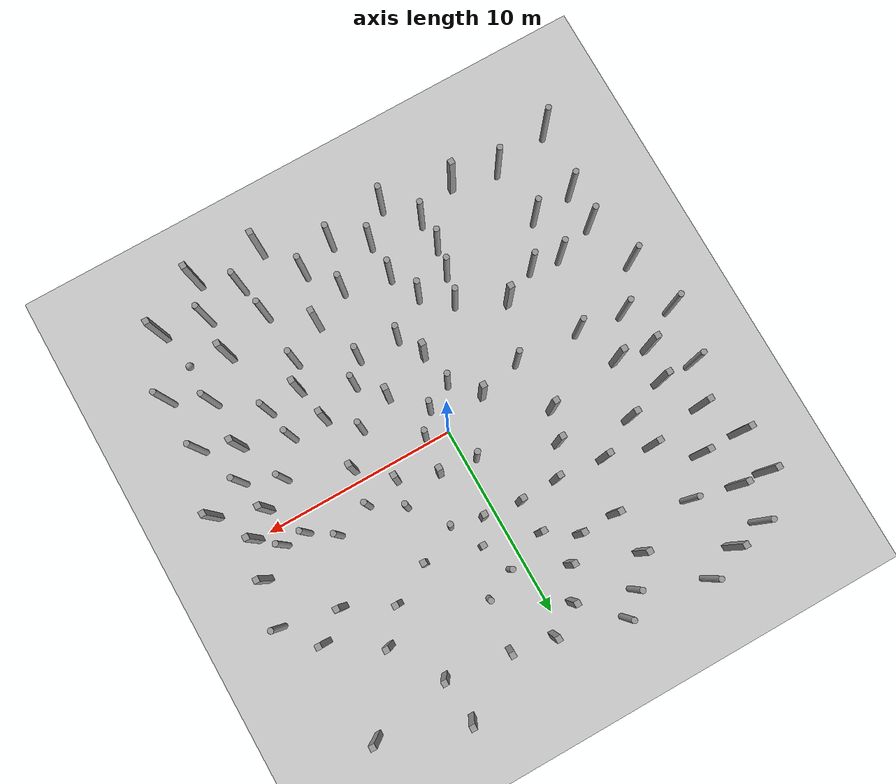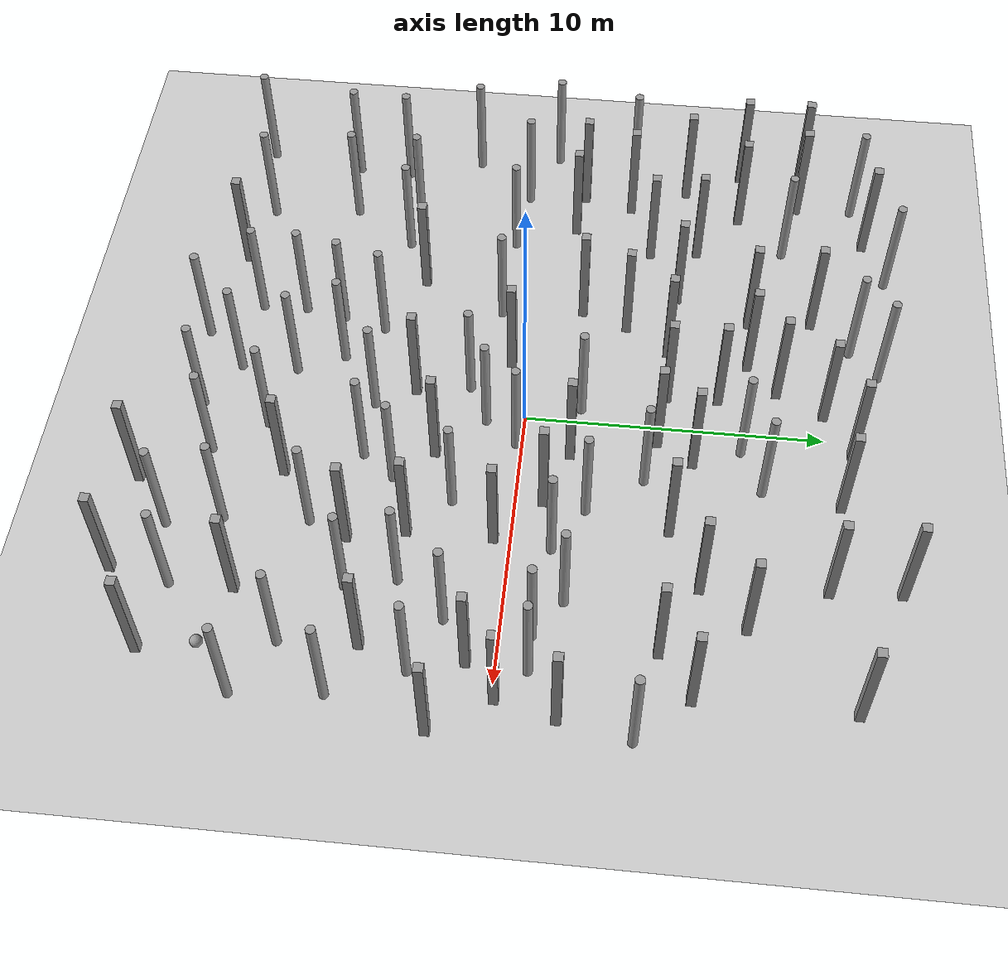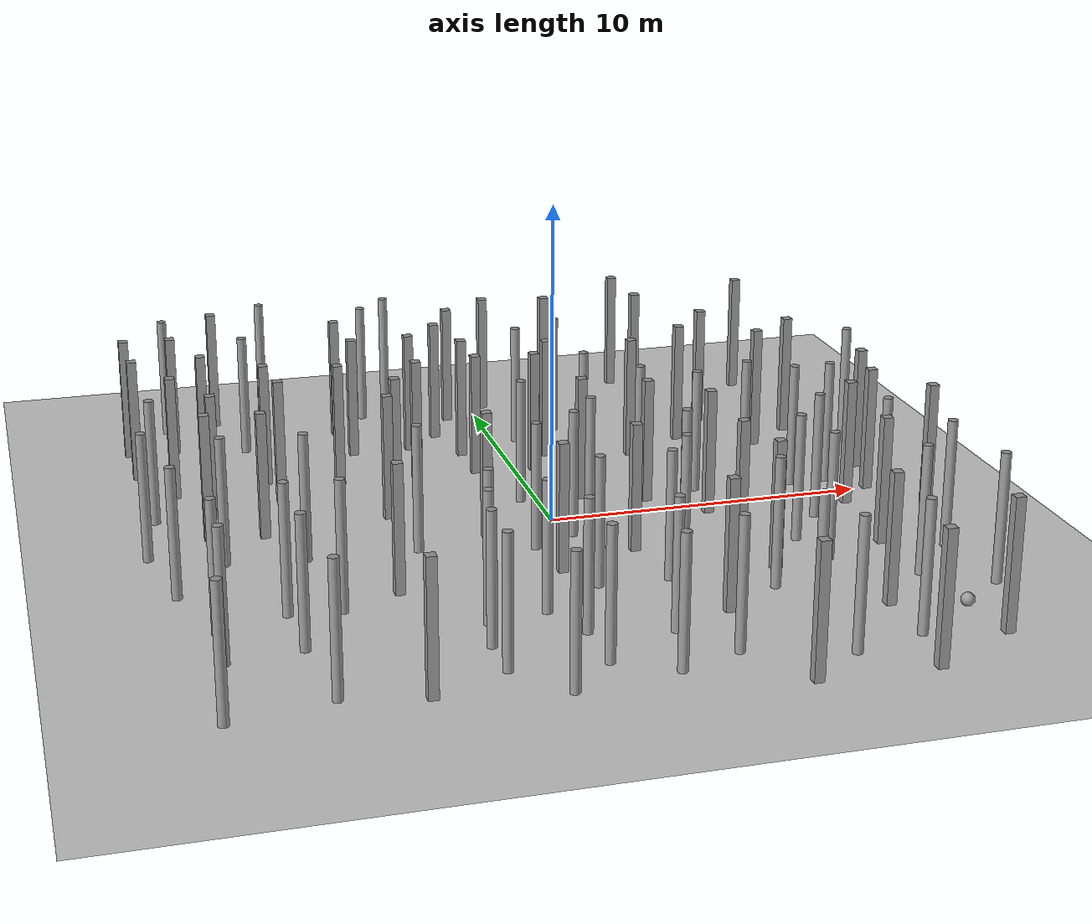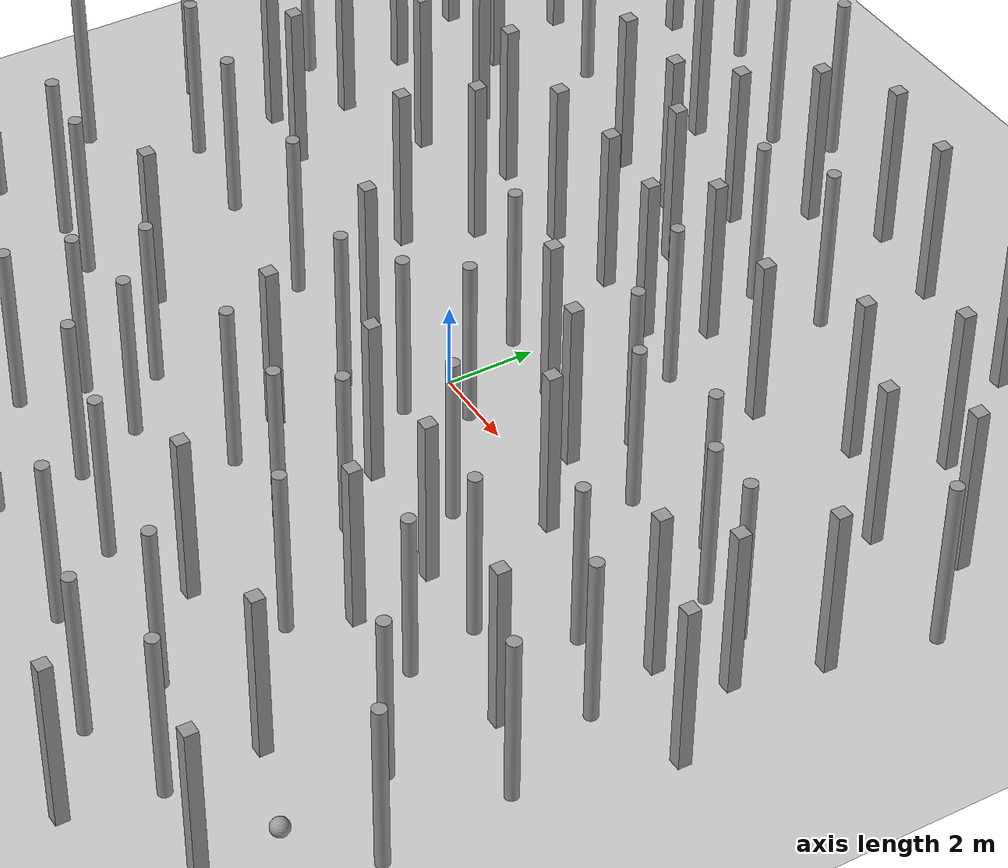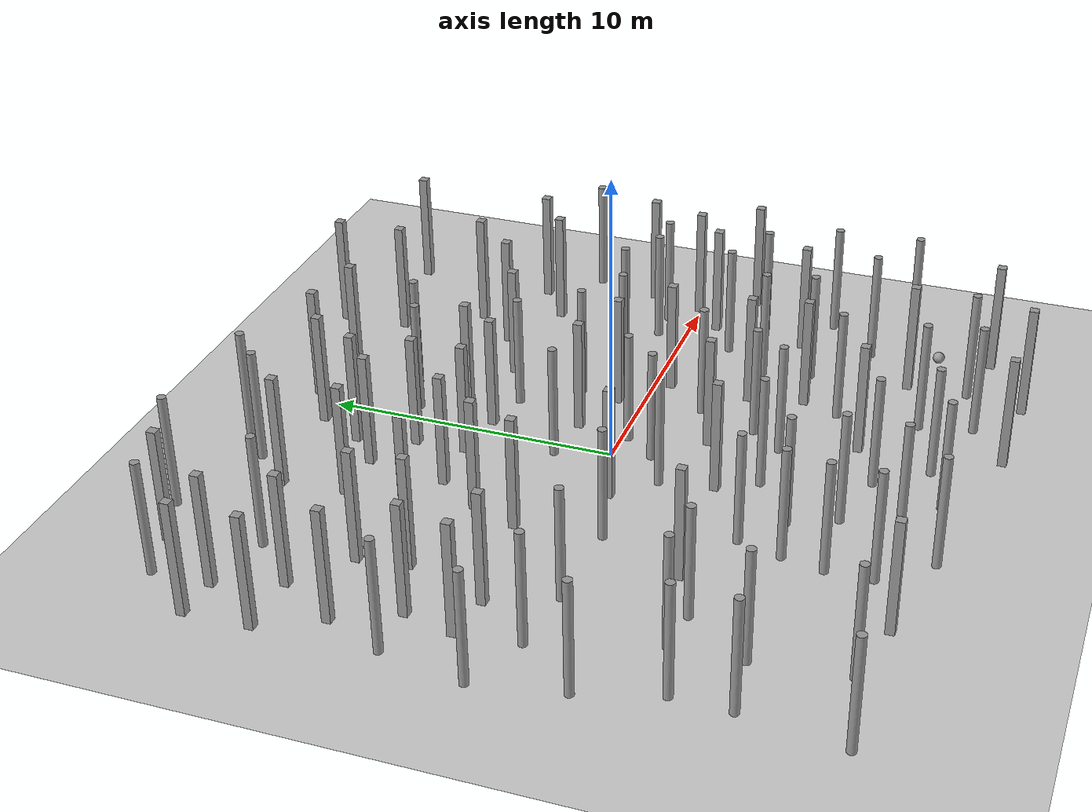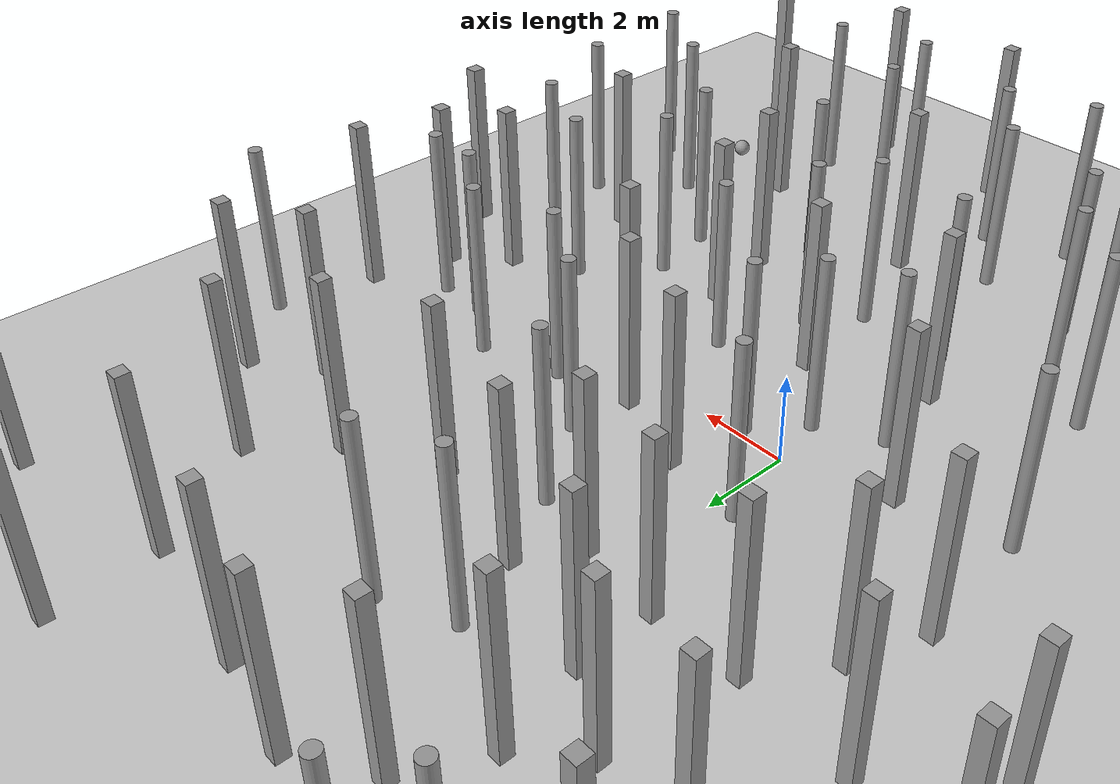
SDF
<sdf version="1.6">
 <world name="default">
  <light name="sun" type="directional">
   <pose>0 0 10 0 -0 0</pose>
   <diffuse>0.8 0.8 0.8 1</diffuse>
   <specular>0.2 0.2 0.2 1</specular>
   <attenuation>
    <range>1000</range>
    <constant>0.9</constant>
    <linear>0.01</linear>
    <quadratic>0.001</quadratic>
   </attenuation>
   <direction>-0.5 0.1 -0.9</direction>
  </light>
  <model name="ground_plane">
   <static>1</static>
   <link name="link">
    <collision name="collision">
     <geometry><plane><normal>0 0 1</normal><size>100 100</size></plane></geometry>
    </collision>
    <visual name="visual">
     <cast_shadows>0</cast_shadows>
     <geometry><plane><normal>0 0 1</normal><size>100 100</size></plane></geometry>
     <material>
      <script><uri>file://media/materials/scripts/gazebo.material</uri><name>Gazebo/Gray</name></script>
     </material>
    </visual>
   </link>
  </model>
  <gravity>0 0 -9.8</gravity>
  <magnetic_field>6e-06 2.3e-05 -4.2e-05</magnetic_field>
  <atmosphere type="adiabatic"/>
  <physics name="default_physics" default="0" type="ode">
   <max_step_size>0.002</max_step_size>
   <real_time_factor>1</real_time_factor>
   <real_time_update_rate>500</real_time_update_rate>
  </physics>
  <scene><ambient>0.4 0.4 0.4 1</ambient><background>0.7 0.7 0.7 1</background><shadows>1</shadows></scene>
  <spherical_coordinates>
   <surface_model>EARTH_WGS84</surface_model>
   <latitude_deg>0</latitude_deg>
   <longitude_deg>0</longitude_deg>
   <elevation>0</elevation>
   <heading_deg>0</heading_deg>
  </spherical_coordinates>
  <model name="unit_sphere">
   <link name="link">
    <inertial>
     <mass>1</mass>
     <inertia><ixx>0.1</ixx><ixy>0</ixy><ixz>0</ixz><iyy>0.1</iyy><iyz>0</iyz><izz>0.1</izz></inertia>
    </inertial>
    <gravity>0</gravity>
    <visual name="visual">
     <geometry><sphere><radius>0.203941</radius></sphere></geometry>
     <material>
      <script><name>Gazebo/Grey</name><uri>file://media/materials/scripts/gazebo.material</uri></script>
      <shader type="pixel"><normal_map>__default__</normal_map></shader>
     </material>
    </visual>
    <collision name="collision">
     <geometry><sphere><radius>0.203941</radius></sphere></geometry>
     <surface>
      <friction>
       <ode><mu>1</mu><mu2>1</mu2><fdir1>0 0 0</fdir1><slip1>0</slip1><slip2>0</slip2></ode>
       <torsional>
        <coefficient>1</coefficient>
        <patch_radius>0</patch_radius>
        <surface_radius>0</surface_radius>
        <use_patch_radius>1</use_patch_radius>
        <ode><slip>0</slip></ode>
       </torsional>
      </friction>
      <bounce><restitution_coefficient>0</restitution_coefficient><threshold>1e+06</threshold></bounce>
      <contact>
       <collide_without_contact>0</collide_without_contact>
       <collide_without_contact_bitmask>1</collide_without_contact_bitmask>
       <collide_bitmask>1</collide_bitmask>
       <ode>
        <soft_cfm>0</soft_cfm>
        <soft_erp>0.2</soft_erp>
        <kp>1e+13</kp>
        <kd>1</kd>
        <max_vel>0.01</max_vel>
        <min_depth>0</min_depth>
       </ode>
       <bullet>
        <split_impulse>1</split_impulse>
        <split_impulse_penetration_threshold>-0.01</split_impulse_penetration_threshold>
        <soft_cfm>0</soft_cfm>
        <soft_erp>0.2</soft_erp>
        <kp>1e+13</kp>
        <kd>1</kd>
       </bullet>
      </contact>
     </surface>
    </collision>
   </link>
   <static>0</static>
   <pose>9.54607 -9.14462 0.203941 0 -0 0</pose>
  </model>
  <audio><device>default</device></audio>
  <model name="unit_box">
   <link name="link">
    <inertial>
     <mass>1000</mass>
     <inertia><ixx>166.667</ixx><ixy>0</ixy><ixz>0</ixz><iyy>166.667</iyy><iyz>0</iyz><izz>166.667</izz></inertia>
    </inertial>
    <visual name="visual">
     <geometry><box><size>0.3 0.3 4</size></box></geometry>
     <material>
      <script><name>Gazebo/Grey</name><uri>file://media/materials/scripts/gazebo.material</uri></script>
      <shader type="vertex"><normal_map>__default__</normal_map></shader>
      <ambient>0.3 0.3 0.3 1</ambient>
      <diffuse>0.7 0.7 0.7 1</diffuse>
      <specular>0.01 0.01 0.01 1</specular>
      <emissive>0 0 0 1</emissive>
     </material>
    </visual>
    <collision name="collision">
     <geometry><box><size>0.3 0.3 4</size></box></geometry>
     <surface>
      <friction>
       <ode><mu>1</mu><mu2>1</mu2><fdir1>0 0 0</fdir1><slip1>0</slip1><slip2>0</slip2></ode>
       <torsional>
        <coefficient>1</coefficient>
        <patch_radius>0</patch_radius>
        <surface_radius>0</surface_radius>
        <use_patch_radius>1</use_patch_radius>
        <ode><slip>0</slip></ode>
       </torsional>
      </friction>
      <bounce><restitution_coefficient>0</restitution_coefficient><threshold>1e+06</threshold></bounce>
      <contact>
       <collide_without_contact>0</collide_without_contact>
       <collide_without_contact_bitmask>1</collide_without_contact_bitmask>
       <collide_bitmask>1</collide_bitmask>
       <ode>
        <soft_cfm>0</soft_cfm>
        <soft_erp>0.2</soft_erp>
        <kp>1e+13</kp>
        <kd>1</kd>
        <max_vel>0.01</max_vel>
        <min_depth>0</min_depth>
       </ode>
       <bullet>
        <split_impulse>1</split_impulse>
        <split_impulse_penetration_threshold>-0.01</split_impulse_penetration_threshold>
        <soft_cfm>0</soft_cfm>
        <soft_erp>0.2</soft_erp>
        <kp>1e+13</kp>
        <kd>1</kd>
       </bullet>
      </contact>
     </surface>
    </collision>
   </link>
   <static>0</static>
   <pose>-1.26727 4.71517 2 3e-05 2e-06 -0.004701</pose>
  </model>
  <model name="unit_box_clone">
   <link name="link">
    <inertial>
     <mass>1000</mass>
     <inertia><ixx>166.667</ixx><ixy>0</ixy><ixz>0</ixz><iyy>166.667</iyy><iyz>0</iyz><izz>166.667</izz></inertia>
    </inertial>
    <visual name="visual">
     <geometry><box><size>0.3 0.3 4</size></box></geometry>
     <material>
      <script><name>Gazebo/Grey</name><uri>file://media/materials/scripts/gazebo.material</uri></script>
      <shader type="vertex"><normal_map>__default__</normal_map></shader>
      <ambient>0.3 0.3 0.3 1</ambient>
      <diffuse>0.7 0.7 0.7 1</diffuse>
      <specular>0.01 0.01 0.01 1</specular>
      <emissive>0 0 0 1</emissive>
     </material>
    </visual>
    <collision name="collision">
     <geometry><box><size>0.3 0.3 4</size></box></geometry>
     <surface>
      <friction>
       <ode><mu>1</mu><mu2>1</mu2><fdir1>0 0 0</fdir1><slip1>0</slip1><slip2>0</slip2></ode>
       <torsional>
        <coefficient>1</coefficient>
        <patch_radius>0</patch_radius>
        <surface_radius>0</surface_radius>
        <use_patch_radius>1</use_patch_radius>
        <ode><slip>0</slip></ode>
       </torsional>
      </friction>
      <bounce><restitution_coefficient>0</restitution_coefficient><threshold>1e+06</threshold></bounce>
      <contact>
       <collide_without_contact>0</collide_without_contact>
       <collide_without_contact_bitmask>1</collide_without_contact_bitmask>
       <collide_bitmask>1</collide_bitmask>
       <ode>
        <soft_cfm>0</soft_cfm>
        <soft_erp>0.2</soft_erp>
        <kp>1e+13</kp>
        <kd>1</kd>
        <max_vel>0.01</max_vel>
        <min_depth>0</min_depth>
       </ode>
       <bullet>
        <split_impulse>1</split_impulse>
        <split_impulse_penetration_threshold>-0.01</split_impulse_penetration_threshold>
        <soft_cfm>0</soft_cfm>
        <soft_erp>0.2</soft_erp>
        <kp>1e+13</kp>
        <kd>1</kd>
       </bullet>
      </contact>
     </surface>
    </collision>
   </link>
   <static>0</static>
   <pose>-2.25019 -0.681054 2 -0 2e-06 -0.006906</pose>
  </model>
  <model name="unit_box_clone_1">
   <link name="link">
    <inertial>
     <mass>1000</mass>
     <inertia><ixx>166.667</ixx><ixy>0</ixy><ixz>0</ixz><iyy>166.667</iyy><iyz>0</iyz><izz>166.667</izz></inertia>
    </inertial>
    <visual name="visual">
     <geometry><box><size>0.3 0.3 4</size></box></geometry>
     <material>
      <script><name>Gazebo/Grey</name><uri>file://media/materials/scripts/gazebo.material</uri></script>
      <shader type="vertex"><normal_map>__default__</normal_map></shader>
      <ambient>0.3 0.3 0.3 1</ambient>
      <diffuse>0.7 0.7 0.7 1</diffuse>
      <specular>0.01 0.01 0.01 1</specular>
      <emissive>0 0 0 1</emissive>
     </material>
    </visual>
    <collision name="collision">
     <geometry><box><size>0.3 0.3 4</size></box></geometry>
     <surface>
      <friction>
       <ode><mu>1</mu><mu2>1</mu2><fdir1>0 0 0</fdir1><slip1>0</slip1><slip2>0</slip2></ode>
       <torsional>
        <coefficient>1</coefficient>
        <patch_radius>0</patch_radius>
        <surface_radius>0</surface_radius>
        <use_patch_radius>1</use_patch_radius>
        <ode><slip>0</slip></ode>
       </torsional>
      </friction>
      <bounce><restitution_coefficient>0</restitution_coefficient><threshold>1e+06</threshold></bounce>
      <contact>
       <collide_without_contact>0</collide_without_contact>
       <collide_without_contact_bitmask>1</collide_without_contact_bitmask>
       <collide_bitmask>1</collide_bitmask>
       <ode>
        <soft_cfm>0</soft_cfm>
        <soft_erp>0.2</soft_erp>
        <kp>1e+13</kp>
        <kd>1</kd>
        <max_vel>0.01</max_vel>
        <min_depth>0</min_depth>
       </ode>
       <bullet>
        <split_impulse>1</split_impulse>
        <split_impulse_penetration_threshold>-0.01</split_impulse_penetration_threshold>
        <soft_cfm>0</soft_cfm>
        <soft_erp>0.2</soft_erp>
        <kp>1e+13</kp>
        <kd>1</kd>
       </bullet>
      </contact>
     </surface>
    </collision>
   </link>
   <static>0</static>
   <pose>-2.89921 7.41403 2 -1.9e-05 4e-06 -0.002147</pose>
  </model>
  <model name="unit_box_clone_2">
   <link name="link">
    <inertial>
     <mass>1000</mass>
     <inertia><ixx>166.667</ixx><ixy>0</ixy><ixz>0</ixz><iyy>166.667</iyy><iyz>0</iyz><izz>166.667</izz></inertia>
    </inertial>
    <visual name="visual">
     <geometry><box><size>0.3 0.3 4</size></box></geometry>
     <material>
      <script><name>Gazebo/Grey</name><uri>file://media/materials/scripts/gazebo.material</uri></script>
      <shader type="vertex"><normal_map>__default__</normal_map></shader>
      <ambient>0.3 0.3 0.3 1</ambient>
      <diffuse>0.7 0.7 0.7 1</diffuse>
      <specular>0.01 0.01 0.01 1</specular>
      <emissive>0 0 0 1</emissive>
     </material>
    </visual>
    <collision name="collision">
     <geometry><box><size>0.3 0.3 4</size></box></geometry>
     <surface>
      <friction>
       <ode><mu>1</mu><mu2>1</mu2><fdir1>0 0 0</fdir1><slip1>0</slip1><slip2>0</slip2></ode>
       <torsional>
        <coefficient>1</coefficient>
        <patch_radius>0</patch_radius>
        <surface_radius>0</surface_radius>
        <use_patch_radius>1</use_patch_radius>
        <ode><slip>0</slip></ode>
       </torsional>
      </friction>
      <bounce><restitution_coefficient>0</restitution_coefficient><threshold>1e+06</threshold></bounce>
      <contact>
       <collide_without_contact>0</collide_without_contact>
       <collide_without_contact_bitmask>1</collide_without_contact_bitmask>
       <collide_bitmask>1</collide_bitmask>
       <ode>
        <soft_cfm>0</soft_cfm>
        <soft_erp>0.2</soft_erp>
        <kp>1e+13</kp>
        <kd>1</kd>
        <max_vel>0.01</max_vel>
        <min_depth>0</min_depth>
       </ode>
       <bullet>
        <split_impulse>1</split_impulse>
        <split_impulse_penetration_threshold>-0.01</split_impulse_penetration_threshold>
        <soft_cfm>0</soft_cfm>
        <soft_erp>0.2</soft_erp>
        <kp>1e+13</kp>
        <kd>1</kd>
       </bullet>
      </contact>
     </surface>
    </collision>
   </link>
   <static>0</static>
   <pose>4.92525 -3.34789 2 -2e-06 -5e-06 0.005092</pose>
  </model>
  <model name="unit_box_clone_3">
   <link name="link">
    <inertial>
     <mass>1000</mass>
     <inertia><ixx>166.667</ixx><ixy>0</ixy><ixz>0</ixz><iyy>166.667</iyy><iyz>0</iyz><izz>166.667</izz></inertia>
    </inertial>
    <visual name="visual">
     <geometry><box><size>0.3 0.3 4</size></box></geometry>
     <material>
      <script><name>Gazebo/Grey</name><uri>file://media/materials/scripts/gazebo.material</uri></script>
      <shader type="vertex"><normal_map>__default__</normal_map></shader>
      <ambient>0.3 0.3 0.3 1</ambient>
      <diffuse>0.7 0.7 0.7 1</diffuse>
      <specular>0.01 0.01 0.01 1</specular>
      <emissive>0 0 0 1</emissive>
     </material>
    </visual>
    <collision name="collision">
     <geometry><box><size>0.3 0.3 4</size></box></geometry>
     <surface>
      <friction>
       <ode><mu>1</mu><mu2>1</mu2><fdir1>0 0 0</fdir1><slip1>0</slip1><slip2>0</slip2></ode>
       <torsional>
        <coefficient>1</coefficient>
        <patch_radius>0</patch_radius>
        <surface_radius>0</surface_radius>
        <use_patch_radius>1</use_patch_radius>
        <ode><slip>0</slip></ode>
       </torsional>
      </friction>
      <bounce><restitution_coefficient>0</restitution_coefficient><threshold>1e+06</threshold></bounce>
      <contact>
       <collide_without_contact>0</collide_without_contact>
       <collide_without_contact_bitmask>1</collide_without_contact_bitmask>
       <collide_bitmask>1</collide_bitmask>
       <ode>
        <soft_cfm>0</soft_cfm>
        <soft_erp>0.2</soft_erp>
        <kp>1e+13</kp>
        <kd>1</kd>
        <max_vel>0.01</max_vel>
        <min_depth>0</min_depth>
       </ode>
       <bullet>
        <split_impulse>1</split_impulse>
        <split_impulse_penetration_threshold>-0.01</split_impulse_penetration_threshold>
        <soft_cfm>0</soft_cfm>
        <soft_erp>0.2</soft_erp>
        <kp>1e+13</kp>
        <kd>1</kd>
       </bullet>
      </contact>
     </surface>
    </collision>
   </link>
   <static>0</static>
   <pose>-9.81584 6.9736 2 -3e-06 -3e-06 -0.001235</pose>
  </model>
  <model name="unit_box_clone_4">
   <link name="link">
    <inertial>
     <mass>1000</mass>
     <inertia><ixx>166.667</ixx><ixy>0</ixy><ixz>0</ixz><iyy>166.667</iyy><iyz>0</iyz><izz>166.667</izz></inertia>
    </inertial>
    <visual name="visual">
     <geometry><box><size>0.3 0.3 4</size></box></geometry>
     <material>
      <script><name>Gazebo/Grey</name><uri>file://media/materials/scripts/gazebo.material</uri></script>
      <shader type="vertex"><normal_map>__default__</normal_map></shader>
      <ambient>0.3 0.3 0.3 1</ambient>
      <diffuse>0.7 0.7 0.7 1</diffuse>
      <specular>0.01 0.01 0.01 1</specular>
      <emissive>0 0 0 1</emissive>
     </material>
    </visual>
    <collision name="collision">
     <geometry><box><size>0.3 0.3 4</size></box></geometry>
     <surface>
      <friction>
       <ode><mu>1</mu><mu2>1</mu2><fdir1>0 0 0</fdir1><slip1>0</slip1><slip2>0</slip2></ode>
       <torsional>
        <coefficient>1</coefficient>
        <patch_radius>0</patch_radius>
        <surface_radius>0</surface_radius>
        <use_patch_radius>1</use_patch_radius>
        <ode><slip>0</slip></ode>
       </torsional>
      </friction>
      <bounce><restitution_coefficient>0</restitution_coefficient><threshold>1e+06</threshold></bounce>
      <contact>
       <collide_without_contact>0</collide_without_contact>
       <collide_without_contact_bitmask>1</collide_without_contact_bitmask>
       <collide_bitmask>1</collide_bitmask>
       <ode>
        <soft_cfm>0</soft_cfm>
        <soft_erp>0.2</soft_erp>
        <kp>1e+13</kp>
        <kd>1</kd>
        <max_vel>0.01</max_vel>
        <min_depth>0</min_depth>
       </ode>
       <bullet>
        <split_impulse>1</split_impulse>
        <split_impulse_penetration_threshold>-0.01</split_impulse_penetration_threshold>
        <soft_cfm>0</soft_cfm>
        <soft_erp>0.2</soft_erp>
        <kp>1e+13</kp>
        <kd>1</kd>
       </bullet>
      </contact>
     </surface>
    </collision>
   </link>
   <static>0</static>
   <pose>-12.064 9.20917 2 -4e-06 -0 -0.001841</pose>
  </model>
  <model name="unit_box_clone_5">
   <link name="link">
    <inertial>
     <mass>1000</mass>
     <inertia><ixx>166.667</ixx><ixy>0</ixy><ixz>0</ixz><iyy>166.667</iyy><iyz>0</iyz><izz>166.667</izz></inertia>
    </inertial>
    <visual name="visual">
     <geometry><box><size>0.3 0.3 4</size></box></geometry>
     <material>
      <script><name>Gazebo/Grey</name><uri>file://media/materials/scripts/gazebo.material</uri></script>
      <shader type="vertex"><normal_map>__default__</normal_map></shader>
      <ambient>0.3 0.3 0.3 1</ambient>
      <diffuse>0.7 0.7 0.7 1</diffuse>
      <specular>0.01 0.01 0.01 1</specular>
      <emissive>0 0 0 1</emissive>
     </material>
    </visual>
    <collision name="collision">
     <geometry><box><size>0.3 0.3 4</size></box></geometry>
     <surface>
      <friction>
       <ode><mu>1</mu><mu2>1</mu2><fdir1>0 0 0</fdir1><slip1>0</slip1><slip2>0</slip2></ode>
       <torsional>
        <coefficient>1</coefficient>
        <patch_radius>0</patch_radius>
        <surface_radius>0</surface_radius>
        <use_patch_radius>1</use_patch_radius>
        <ode><slip>0</slip></ode>
       </torsional>
      </friction>
      <bounce><restitution_coefficient>0</restitution_coefficient><threshold>1e+06</threshold></bounce>
      <contact>
       <collide_without_contact>0</collide_without_contact>
       <collide_without_contact_bitmask>1</collide_without_contact_bitmask>
       <collide_bitmask>1</collide_bitmask>
       <ode>
        <soft_cfm>0</soft_cfm>
        <soft_erp>0.2</soft_erp>
        <kp>1e+13</kp>
        <kd>1</kd>
        <max_vel>0.01</max_vel>
        <min_depth>0</min_depth>
       </ode>
       <bullet>
        <split_impulse>1</split_impulse>
        <split_impulse_penetration_threshold>-0.01</split_impulse_penetration_threshold>
        <soft_cfm>0</soft_cfm>
        <soft_erp>0.2</soft_erp>
        <kp>1e+13</kp>
        <kd>1</kd>
       </bullet>
      </contact>
     </surface>
    </collision>
   </link>
   <static>0</static>
   <pose>3.35409 0.911811 2 0 1e-06 -0.009543</pose>
  </model>
  <model name="unit_box_clone_6">
   <link name="link">
    <inertial>
     <mass>1000</mass>
     <inertia><ixx>166.667</ixx><ixy>0</ixy><ixz>0</ixz><iyy>166.667</iyy><iyz>0</iyz><izz>166.667</izz></inertia>
    </inertial>
    <visual name="visual">
     <geometry><box><size>0.3 0.3 4</size></box></geometry>
     <material>
      <script><name>Gazebo/Grey</name><uri>file://media/materials/scripts/gazebo.material</uri></script>
      <shader type="vertex"><normal_map>__default__</normal_map></shader>
      <ambient>0.3 0.3 0.3 1</ambient>
      <diffuse>0.7 0.7 0.7 1</diffuse>
      <specular>0.01 0.01 0.01 1</specular>
      <emissive>0 0 0 1</emissive>
     </material>
    </visual>
    <collision name="collision">
     <geometry><box><size>0.3 0.3 4</size></box></geometry>
     <surface>
      <friction>
       <ode><mu>1</mu><mu2>1</mu2><fdir1>0 0 0</fdir1><slip1>0</slip1><slip2>0</slip2></ode>
       <torsional>
        <coefficient>1</coefficient>
        <patch_radius>0</patch_radius>
        <surface_radius>0</surface_radius>
        <use_patch_radius>1</use_patch_radius>
        <ode><slip>0</slip></ode>
       </torsional>
      </friction>
      <bounce><restitution_coefficient>0</restitution_coefficient><threshold>1e+06</threshold></bounce>
      <contact>
       <collide_without_contact>0</collide_without_contact>
       <collide_without_contact_bitmask>1</collide_without_contact_bitmask>
       <collide_bitmask>1</collide_bitmask>
       <ode>
        <soft_cfm>0</soft_cfm>
        <soft_erp>0.2</soft_erp>
        <kp>1e+13</kp>
        <kd>1</kd>
        <max_vel>0.01</max_vel>
        <min_depth>0</min_depth>
       </ode>
       <bullet>
        <split_impulse>1</split_impulse>
        <split_impulse_penetration_threshold>-0.01</split_impulse_penetration_threshold>
        <soft_cfm>0</soft_cfm>
        <soft_erp>0.2</soft_erp>
        <kp>1e+13</kp>
        <kd>1</kd>
       </bullet>
      </contact>
     </surface>
    </collision>
   </link>
   <static>0</static>
   <pose>10.5125 0.091586 2.00001 0 7.9e-05 -0.0104</pose>
  </model>
  <model name="unit_box_clone_7">
   <link name="link">
    <inertial>
     <mass>1000</mass>
     <inertia><ixx>166.667</ixx><ixy>0</ixy><ixz>0</ixz><iyy>166.667</iyy><iyz>0</iyz><izz>166.667</izz></inertia>
    </inertial>
    <visual name="visual">
     <geometry><box><size>0.3 0.3 4</size></box></geometry>
     <material>
      <script><name>Gazebo/Grey</name><uri>file://media/materials/scripts/gazebo.material</uri></script>
      <shader type="vertex"><normal_map>__default__</normal_map></shader>
      <ambient>0.3 0.3 0.3 1</ambient>
      <diffuse>0.7 0.7 0.7 1</diffuse>
      <specular>0.01 0.01 0.01 1</specular>
      <emissive>0 0 0 1</emissive>
     </material>
    </visual>
    <collision name="collision">
     <geometry><box><size>0.3 0.3 4</size></box></geometry>
     <surface>
      <friction>
       <ode><mu>1</mu><mu2>1</mu2><fdir1>0 0 0</fdir1><slip1>0</slip1><slip2>0</slip2></ode>
       <torsional>
        <coefficient>1</coefficient>
        <patch_radius>0</patch_radius>
        <surface_radius>0</surface_radius>
        <use_patch_radius>1</use_patch_radius>
        <ode><slip>0</slip></ode>
       </torsional>
      </friction>
      <bounce><restitution_coefficient>0</restitution_coefficient><threshold>1e+06</threshold></bounce>
      <contact>
       <collide_without_contact>0</collide_without_contact>
       <collide_without_contact_bitmask>1</collide_without_contact_bitmask>
       <collide_bitmask>1</collide_bitmask>
       <ode>
        <soft_cfm>0</soft_cfm>
        <soft_erp>0.2</soft_erp>
        <kp>1e+13</kp>
        <kd>1</kd>
        <max_vel>0.01</max_vel>
        <min_depth>0</min_depth>
       </ode>
       <bullet>
        <split_impulse>1</split_impulse>
        <split_impulse_penetration_threshold>-0.01</split_impulse_penetration_threshold>
        <soft_cfm>0</soft_cfm>
        <soft_erp>0.2</soft_erp>
        <kp>1e+13</kp>
        <kd>1</kd>
       </bullet>
      </contact>
     </surface>
    </collision>
   </link>
   <static>0</static>
   <pose>9.86056 -10.963 2 8e-06 7e-06 -0.005605</pose>
  </model>
  <model name="unit_box_clone_8">
   <link name="link">
    <inertial>
     <mass>1000</mass>
     <inertia><ixx>166.667</ixx><ixy>0</ixy><ixz>0</ixz><iyy>166.667</iyy><iyz>0</iyz><izz>166.667</izz></inertia>
    </inertial>
    <visual name="visual">
     <geometry><box><size>0.3 0.3 4</size></box></geometry>
     <material>
      <script><name>Gazebo/Grey</name><uri>file://media/materials/scripts/gazebo.material</uri></script>
      <shader type="vertex"><normal_map>__default__</normal_map></shader>
      <ambient>0.3 0.3 0.3 1</ambient>
      <diffuse>0.7 0.7 0.7 1</diffuse>
      <specular>0.01 0.01 0.01 1</specular>
      <emissive>0 0 0 1</emissive>
     </material>
    </visual>
    <collision name="collision">
     <geometry><box><size>0.3 0.3 4</size></box></geometry>
     <surface>
      <friction>
       <ode><mu>1</mu><mu2>1</mu2><fdir1>0 0 0</fdir1><slip1>0</slip1><slip2>0</slip2></ode>
       <torsional>
        <coefficient>1</coefficient>
        <patch_radius>0</patch_radius>
        <surface_radius>0</surface_radius>
        <use_patch_radius>1</use_patch_radius>
        <ode><slip>0</slip></ode>
       </torsional>
      </friction>
      <bounce><restitution_coefficient>0</restitution_coefficient><threshold>1e+06</threshold></bounce>
      <contact>
       <collide_without_contact>0</collide_without_contact>
       <collide_without_contact_bitmask>1</collide_without_contact_bitmask>
       <collide_bitmask>1</collide_bitmask>
       <ode>
        <soft_cfm>0</soft_cfm>
        <soft_erp>0.2</soft_erp>
        <kp>1e+13</kp>
        <kd>1</kd>
        <max_vel>0.01</max_vel>
        <min_depth>0</min_depth>
       </ode>
       <bullet>
        <split_impulse>1</split_impulse>
        <split_impulse_penetration_threshold>-0.01</split_impulse_penetration_threshold>
        <soft_cfm>0</soft_cfm>
        <soft_erp>0.2</soft_erp>
        <kp>1e+13</kp>
        <kd>1</kd>
       </bullet>
      </contact>
     </surface>
    </collision>
   </link>
   <static>0</static>
   <pose>5.86945 10.1035 2.00001 0 -3.9e-05 -0.000838</pose>
  </model>
  <model name="unit_box_clone_9">
   <link name="link">
    <inertial>
     <mass>1000</mass>
     <inertia><ixx>166.667</ixx><ixy>0</ixy><ixz>0</ixz><iyy>166.667</iyy><iyz>0</iyz><izz>166.667</izz></inertia>
    </inertial>
    <visual name="visual">
     <geometry><box><size>0.3 0.3 4</size></box></geometry>
     <material>
      <script><name>Gazebo/Grey</name><uri>file://media/materials/scripts/gazebo.material</uri></script>
      <shader type="vertex"><normal_map>__default__</normal_map></shader>
      <ambient>0.3 0.3 0.3 1</ambient>
      <diffuse>0.7 0.7 0.7 1</diffuse>
      <specular>0.01 0.01 0.01 1</specular>
      <emissive>0 0 0 1</emissive>
     </material>
    </visual>
    <collision name="collision">
     <geometry><box><size>0.3 0.3 4</size></box></geometry>
     <surface>
      <friction>
       <ode><mu>1</mu><mu2>1</mu2><fdir1>0 0 0</fdir1><slip1>0</slip1><slip2>0</slip2></ode>
       <torsional>
        <coefficient>1</coefficient>
        <patch_radius>0</patch_radius>
        <surface_radius>0</surface_radius>
        <use_patch_radius>1</use_patch_radius>
        <ode><slip>0</slip></ode>
       </torsional>
      </friction>
      <bounce><restitution_coefficient>0</restitution_coefficient><threshold>1e+06</threshold></bounce>
      <contact>
       <collide_without_contact>0</collide_without_contact>
       <collide_without_contact_bitmask>1</collide_without_contact_bitmask>
       <collide_bitmask>1</collide_bitmask>
       <ode>
        <soft_cfm>0</soft_cfm>
        <soft_erp>0.2</soft_erp>
        <kp>1e+13</kp>
        <kd>1</kd>
        <max_vel>0.01</max_vel>
        <min_depth>0</min_depth>
       </ode>
       <bullet>
        <split_impulse>1</split_impulse>
        <split_impulse_penetration_threshold>-0.01</split_impulse_penetration_threshold>
        <soft_cfm>0</soft_cfm>
        <soft_erp>0.2</soft_erp>
        <kp>1e+13</kp>
        <kd>1</kd>
       </bullet>
      </contact>
     </surface>
    </collision>
   </link>
   <static>0</static>
   <pose>-8.00892 5.50005 2.00001 5.1e-05 -9e-06 -0.00313</pose>
  </model>
  <model name="unit_box_clone_10">
   <link name="link">
    <inertial>
     <mass>1000</mass>
     <inertia><ixx>166.667</ixx><ixy>0</ixy><ixz>0</ixz><iyy>166.667</iyy><iyz>0</iyz><izz>166.667</izz></inertia>
    </inertial>
    <visual name="visual">
     <geometry><box><size>0.3 0.3 4</size></box></geometry>
     <material>
      <script><name>Gazebo/Grey</name><uri>file://media/materials/scripts/gazebo.material</uri></script>
      <shader type="vertex"><normal_map>__default__</normal_map></shader>
      <ambient>0.3 0.3 0.3 1</ambient>
      <diffuse>0.7 0.7 0.7 1</diffuse>
      <specular>0.01 0.01 0.01 1</specular>
      <emissive>0 0 0 1</emissive>
     </material>
    </visual>
    <collision name="collision">
     <geometry><box><size>0.3 0.3 4</size></box></geometry>
     <surface>
      <friction>
       <ode><mu>1</mu><mu2>1</mu2><fdir1>0 0 0</fdir1><slip1>0</slip1><slip2>0</slip2></ode>
       <torsional>
        <coefficient>1</coefficient>
        <patch_radius>0</patch_radius>
        <surface_radius>0</surface_radius>
        <use_patch_radius>1</use_patch_radius>
        <ode><slip>0</slip></ode>
       </torsional>
      </friction>
      <bounce><restitution_coefficient>0</restitution_coefficient><threshold>1e+06</threshold></bounce>
      <contact>
       <collide_without_contact>0</collide_without_contact>
       <collide_without_contact_bitmask>1</collide_without_contact_bitmask>
       <collide_bitmask>1</collide_bitmask>
       <ode>
        <soft_cfm>0</soft_cfm>
        <soft_erp>0.2</soft_erp>
        <kp>1e+13</kp>
        <kd>1</kd>
        <max_vel>0.01</max_vel>
        <min_depth>0</min_depth>
       </ode>
       <bullet>
        <split_impulse>1</split_impulse>
        <split_impulse_penetration_threshold>-0.01</split_impulse_penetration_threshold>
        <soft_cfm>0</soft_cfm>
        <soft_erp>0.2</soft_erp>
        <kp>1e+13</kp>
        <kd>1</kd>
       </bullet>
      </contact>
     </surface>
    </collision>
   </link>
   <static>0</static>
   <pose>-8.91737 11.4995 2 4e-06 -1e-06 -0.00398</pose>
  </model>
  <model name="unit_box_clone_11">
   <link name="link">
    <inertial>
     <mass>1000</mass>
     <inertia><ixx>166.667</ixx><ixy>0</ixy><ixz>0</ixz><iyy>166.667</iyy><iyz>0</iyz><izz>166.667</izz></inertia>
    </inertial>
    <visual name="visual">
     <geometry><box><size>0.3 0.3 4</size></box></geometry>
     <material>
      <script><name>Gazebo/Grey</name><uri>file://media/materials/scripts/gazebo.material</uri></script>
      <shader type="vertex"><normal_map>__default__</normal_map></shader>
      <ambient>0.3 0.3 0.3 1</ambient>
      <diffuse>0.7 0.7 0.7 1</diffuse>
      <specular>0.01 0.01 0.01 1</specular>
      <emissive>0 0 0 1</emissive>
     </material>
    </visual>
    <collision name="collision">
     <geometry><box><size>0.3 0.3 4</size></box></geometry>
     <surface>
      <friction>
       <ode><mu>1</mu><mu2>1</mu2><fdir1>0 0 0</fdir1><slip1>0</slip1><slip2>0</slip2></ode>
       <torsional>
        <coefficient>1</coefficient>
        <patch_radius>0</patch_radius>
        <surface_radius>0</surface_radius>
        <use_patch_radius>1</use_patch_radius>
        <ode><slip>0</slip></ode>
       </torsional>
      </friction>
      <bounce><restitution_coefficient>0</restitution_coefficient><threshold>1e+06</threshold></bounce>
      <contact>
       <collide_without_contact>0</collide_without_contact>
       <collide_without_contact_bitmask>1</collide_without_contact_bitmask>
       <collide_bitmask>1</collide_bitmask>
       <ode>
        <soft_cfm>0</soft_cfm>
        <soft_erp>0.2</soft_erp>
        <kp>1e+13</kp>
        <kd>1</kd>
        <max_vel>0.01</max_vel>
        <min_depth>0</min_depth>
       </ode>
       <bullet>
        <split_impulse>1</split_impulse>
        <split_impulse_penetration_threshold>-0.01</split_impulse_penetration_threshold>
        <soft_cfm>0</soft_cfm>
        <soft_erp>0.2</soft_erp>
        <kp>1e+13</kp>
        <kd>1</kd>
       </bullet>
      </contact>
     </surface>
    </collision>
   </link>
   <static>0</static>
   <pose>-10.559 9.10961 2 1.3e-05 1e-06 0.003373</pose>
  </model>
  <model name="unit_box_clone_13">
   <link name="link">
    <inertial>
     <mass>1000</mass>
     <inertia><ixx>166.667</ixx><ixy>0</ixy><ixz>0</ixz><iyy>166.667</iyy><iyz>0</iyz><izz>166.667</izz></inertia>
    </inertial>
    <visual name="visual">
     <geometry><box><size>0.3 0.3 4</size></box></geometry>
     <material>
      <script><name>Gazebo/Grey</name><uri>file://media/materials/scripts/gazebo.material</uri></script>
      <shader type="vertex"><normal_map>__default__</normal_map></shader>
      <ambient>0.3 0.3 0.3 1</ambient>
      <diffuse>0.7 0.7 0.7 1</diffuse>
      <specular>0.01 0.01 0.01 1</specular>
      <emissive>0 0 0 1</emissive>
     </material>
    </visual>
    <collision name="collision">
     <geometry><box><size>0.3 0.3 4</size></box></geometry>
     <surface>
      <friction>
       <ode><mu>1</mu><mu2>1</mu2><fdir1>0 0 0</fdir1><slip1>0</slip1><slip2>0</slip2></ode>
       <torsional>
        <coefficient>1</coefficient>
        <patch_radius>0</patch_radius>
        <surface_radius>0</surface_radius>
        <use_patch_radius>1</use_patch_radius>
        <ode><slip>0</slip></ode>
       </torsional>
      </friction>
      <bounce><restitution_coefficient>0</restitution_coefficient><threshold>1e+06</threshold></bounce>
      <contact>
       <collide_without_contact>0</collide_without_contact>
       <collide_without_contact_bitmask>1</collide_without_contact_bitmask>
       <collide_bitmask>1</collide_bitmask>
       <ode>
        <soft_cfm>0</soft_cfm>
        <soft_erp>0.2</soft_erp>
        <kp>1e+13</kp>
        <kd>1</kd>
        <max_vel>0.01</max_vel>
        <min_depth>0</min_depth>
       </ode>
       <bullet>
        <split_impulse>1</split_impulse>
        <split_impulse_penetration_threshold>-0.01</split_impulse_penetration_threshold>
        <soft_cfm>0</soft_cfm>
        <soft_erp>0.2</soft_erp>
        <kp>1e+13</kp>
        <kd>1</kd>
       </bullet>
      </contact>
     </surface>
    </collision>
   </link>
   <static>0</static>
   <pose>-10.0001 3.00008 2 4e-06 2e-06 -0.003725</pose>
  </model>
  <model name="unit_box_clone_14">
   <link name="link">
    <inertial>
     <mass>1000</mass>
     <inertia><ixx>166.667</ixx><ixy>0</ixy><ixz>0</ixz><iyy>166.667</iyy><iyz>0</iyz><izz>166.667</izz></inertia>
    </inertial>
    <visual name="visual">
     <geometry><box><size>0.3 0.3 4</size></box></geometry>
     <material>
      <script><name>Gazebo/Grey</name><uri>file://media/materials/scripts/gazebo.material</uri></script>
      <shader type="vertex"><normal_map>__default__</normal_map></shader>
      <ambient>0.3 0.3 0.3 1</ambient>
      <diffuse>0.7 0.7 0.7 1</diffuse>
      <specular>0.01 0.01 0.01 1</specular>
      <emissive>0 0 0 1</emissive>
     </material>
    </visual>
    <collision name="collision">
     <geometry><box><size>0.3 0.3 4</size></box></geometry>
     <surface>
      <friction>
       <ode><mu>1</mu><mu2>1</mu2><fdir1>0 0 0</fdir1><slip1>0</slip1><slip2>0</slip2></ode>
       <torsional>
        <coefficient>1</coefficient>
        <patch_radius>0</patch_radius>
        <surface_radius>0</surface_radius>
        <use_patch_radius>1</use_patch_radius>
        <ode><slip>0</slip></ode>
       </torsional>
      </friction>
      <bounce><restitution_coefficient>0</restitution_coefficient><threshold>1e+06</threshold></bounce>
      <contact>
       <collide_without_contact>0</collide_without_contact>
       <collide_without_contact_bitmask>1</collide_without_contact_bitmask>
       <collide_bitmask>1</collide_bitmask>
       <ode>
        <soft_cfm>0</soft_cfm>
        <soft_erp>0.2</soft_erp>
        <kp>1e+13</kp>
        <kd>1</kd>
        <max_vel>0.01</max_vel>
        <min_depth>0</min_depth>
       </ode>
       <bullet>
        <split_impulse>1</split_impulse>
        <split_impulse_penetration_threshold>-0.01</split_impulse_penetration_threshold>
        <soft_cfm>0</soft_cfm>
        <soft_erp>0.2</soft_erp>
        <kp>1e+13</kp>
        <kd>1</kd>
       </bullet>
      </contact>
     </surface>
    </collision>
   </link>
   <static>0</static>
   <pose>-11.9999 7.00008 2 -1e-06 1.8e-05 -0.000949</pose>
  </model>
  <model name="unit_box_clone_15">
   <link name="link">
    <inertial>
     <mass>1000</mass>
     <inertia><ixx>166.667</ixx><ixy>0</ixy><ixz>0</ixz><iyy>166.667</iyy><iyz>0</iyz><izz>166.667</izz></inertia>
    </inertial>
    <visual name="visual">
     <geometry><box><size>0.3 0.3 4</size></box></geometry>
     <material>
      <script><name>Gazebo/Grey</name><uri>file://media/materials/scripts/gazebo.material</uri></script>
      <shader type="vertex"><normal_map>__default__</normal_map></shader>
      <ambient>0.3 0.3 0.3 1</ambient>
      <diffuse>0.7 0.7 0.7 1</diffuse>
      <specular>0.01 0.01 0.01 1</specular>
      <emissive>0 0 0 1</emissive>
     </material>
    </visual>
    <collision name="collision">
     <geometry><box><size>0.3 0.3 4</size></box></geometry>
     <surface>
      <friction>
       <ode><mu>1</mu><mu2>1</mu2><fdir1>0 0 0</fdir1><slip1>0</slip1><slip2>0</slip2></ode>
       <torsional>
        <coefficient>1</coefficient>
        <patch_radius>0</patch_radius>
        <surface_radius>0</surface_radius>
        <use_patch_radius>1</use_patch_radius>
        <ode><slip>0</slip></ode>
       </torsional>
      </friction>
      <bounce><restitution_coefficient>0</restitution_coefficient><threshold>1e+06</threshold></bounce>
      <contact>
       <collide_without_contact>0</collide_without_contact>
       <collide_without_contact_bitmask>1</collide_without_contact_bitmask>
       <collide_bitmask>1</collide_bitmask>
       <ode>
        <soft_cfm>0</soft_cfm>
        <soft_erp>0.2</soft_erp>
        <kp>1e+13</kp>
        <kd>1</kd>
        <max_vel>0.01</max_vel>
        <min_depth>0</min_depth>
       </ode>
       <bullet>
        <split_impulse>1</split_impulse>
        <split_impulse_penetration_threshold>-0.01</split_impulse_penetration_threshold>
        <soft_cfm>0</soft_cfm>
        <soft_erp>0.2</soft_erp>
        <kp>1e+13</kp>
        <kd>1</kd>
       </bullet>
      </contact>
     </surface>
    </collision>
   </link>
   <static>0</static>
   <pose>-8.74152 1.04888 2.00001 -5.6e-05 -0 0.0032</pose>
  </model>
  <model name="unit_box_clone_16">
   <link name="link">
    <inertial>
     <mass>1000</mass>
     <inertia><ixx>166.667</ixx><ixy>0</ixy><ixz>0</ixz><iyy>166.667</iyy><iyz>0</iyz><izz>166.667</izz></inertia>
    </inertial>
    <visual name="visual">
     <geometry><box><size>0.3 0.3 4</size></box></geometry>
     <material>
      <script><name>Gazebo/Grey</name><uri>file://media/materials/scripts/gazebo.material</uri></script>
      <shader type="vertex"><normal_map>__default__</normal_map></shader>
      <ambient>0.3 0.3 0.3 1</ambient>
      <diffuse>0.7 0.7 0.7 1</diffuse>
      <specular>0.01 0.01 0.01 1</specular>
      <emissive>0 0 0 1</emissive>
     </material>
    </visual>
    <collision name="collision">
     <geometry><box><size>0.3 0.3 4</size></box></geometry>
     <surface>
      <friction>
       <ode><mu>1</mu><mu2>1</mu2><fdir1>0 0 0</fdir1><slip1>0</slip1><slip2>0</slip2></ode>
       <torsional>
        <coefficient>1</coefficient>
        <patch_radius>0</patch_radius>
        <surface_radius>0</surface_radius>
        <use_patch_radius>1</use_patch_radius>
        <ode><slip>0</slip></ode>
       </torsional>
      </friction>
      <bounce><restitution_coefficient>0</restitution_coefficient><threshold>1e+06</threshold></bounce>
      <contact>
       <collide_without_contact>0</collide_without_contact>
       <collide_without_contact_bitmask>1</collide_without_contact_bitmask>
       <collide_bitmask>1</collide_bitmask>
       <ode>
        <soft_cfm>0</soft_cfm>
        <soft_erp>0.2</soft_erp>
        <kp>1e+13</kp>
        <kd>1</kd>
        <max_vel>0.01</max_vel>
        <min_depth>0</min_depth>
       </ode>
       <bullet>
        <split_impulse>1</split_impulse>
        <split_impulse_penetration_threshold>-0.01</split_impulse_penetration_threshold>
        <soft_cfm>0</soft_cfm>
        <soft_erp>0.2</soft_erp>
        <kp>1e+13</kp>
        <kd>1</kd>
       </bullet>
      </contact>
     </surface>
    </collision>
   </link>
   <static>0</static>
   <pose>-10.9999 5.00008 2 -1e-06 1.8e-05 -0.000949</pose>
  </model>
  <model name="unit_box_clone_18">
   <link name="link">
    <inertial>
     <mass>1000</mass>
     <inertia><ixx>166.667</ixx><ixy>0</ixy><ixz>0</ixz><iyy>166.667</iyy><iyz>0</iyz><izz>166.667</izz></inertia>
    </inertial>
    <visual name="visual">
     <geometry><box><size>0.3 0.3 4</size></box></geometry>
     <material>
      <script><name>Gazebo/Grey</name><uri>file://media/materials/scripts/gazebo.material</uri></script>
      <shader type="vertex"><normal_map>__default__</normal_map></shader>
      <ambient>0.3 0.3 0.3 1</ambient>
      <diffuse>0.7 0.7 0.7 1</diffuse>
      <specular>0.01 0.01 0.01 1</specular>
      <emissive>0 0 0 1</emissive>
     </material>
    </visual>
    <collision name="collision">
     <geometry><box><size>0.3 0.3 4</size></box></geometry>
     <surface>
      <friction>
       <ode><mu>1</mu><mu2>1</mu2><fdir1>0 0 0</fdir1><slip1>0</slip1><slip2>0</slip2></ode>
       <torsional>
        <coefficient>1</coefficient>
        <patch_radius>0</patch_radius>
        <surface_radius>0</surface_radius>
        <use_patch_radius>1</use_patch_radius>
        <ode><slip>0</slip></ode>
       </torsional>
      </friction>
      <bounce><restitution_coefficient>0</restitution_coefficient><threshold>1e+06</threshold></bounce>
      <contact>
       <collide_without_contact>0</collide_without_contact>
       <collide_without_contact_bitmask>1</collide_without_contact_bitmask>
       <collide_bitmask>1</collide_bitmask>
       <ode>
        <soft_cfm>0</soft_cfm>
        <soft_erp>0.2</soft_erp>
        <kp>1e+13</kp>
        <kd>1</kd>
        <max_vel>0.01</max_vel>
        <min_depth>0</min_depth>
       </ode>
       <bullet>
        <split_impulse>1</split_impulse>
        <split_impulse_penetration_threshold>-0.01</split_impulse_penetration_threshold>
        <soft_cfm>0</soft_cfm>
        <soft_erp>0.2</soft_erp>
        <kp>1e+13</kp>
        <kd>1</kd>
       </bullet>
      </contact>
     </surface>
    </collision>
   </link>
   <static>0</static>
   <pose>-5.73008 4.8758 2 4e-06 -0 -0.001084</pose>
  </model>
  <model name="unit_box_clone_19">
   <link name="link">
    <inertial>
     <mass>1000</mass>
     <inertia><ixx>166.667</ixx><ixy>0</ixy><ixz>0</ixz><iyy>166.667</iyy><iyz>0</iyz><izz>166.667</izz></inertia>
    </inertial>
    <visual name="visual">
     <geometry><box><size>0.3 0.3 4</size></box></geometry>
     <material>
      <script><name>Gazebo/Grey</name><uri>file://media/materials/scripts/gazebo.material</uri></script>
      <shader type="vertex"><normal_map>__default__</normal_map></shader>
      <ambient>0.3 0.3 0.3 1</ambient>
      <diffuse>0.7 0.7 0.7 1</diffuse>
      <specular>0.01 0.01 0.01 1</specular>
      <emissive>0 0 0 1</emissive>
     </material>
    </visual>
    <collision name="collision">
     <geometry><box><size>0.3 0.3 4</size></box></geometry>
     <surface>
      <friction>
       <ode><mu>1</mu><mu2>1</mu2><fdir1>0 0 0</fdir1><slip1>0</slip1><slip2>0</slip2></ode>
       <torsional>
        <coefficient>1</coefficient>
        <patch_radius>0</patch_radius>
        <surface_radius>0</surface_radius>
        <use_patch_radius>1</use_patch_radius>
        <ode><slip>0</slip></ode>
       </torsional>
      </friction>
      <bounce><restitution_coefficient>0</restitution_coefficient><threshold>1e+06</threshold></bounce>
      <contact>
       <collide_without_contact>0</collide_without_contact>
       <collide_without_contact_bitmask>1</collide_without_contact_bitmask>
       <collide_bitmask>1</collide_bitmask>
       <ode>
        <soft_cfm>0</soft_cfm>
        <soft_erp>0.2</soft_erp>
        <kp>1e+13</kp>
        <kd>1</kd>
        <max_vel>0.01</max_vel>
        <min_depth>0</min_depth>
       </ode>
       <bullet>
        <split_impulse>1</split_impulse>
        <split_impulse_penetration_threshold>-0.01</split_impulse_penetration_threshold>
        <soft_cfm>0</soft_cfm>
        <soft_erp>0.2</soft_erp>
        <kp>1e+13</kp>
        <kd>1</kd>
       </bullet>
      </contact>
     </surface>
    </collision>
   </link>
   <static>0</static>
   <pose>-1.32794 6.44926 2 3e-05 2e-06 -0.004701</pose>
  </model>
  <model name="unit_box_clone_20">
   <link name="link">
    <inertial>
     <mass>1000</mass>
     <inertia><ixx>166.667</ixx><ixy>0</ixy><ixz>0</ixz><iyy>166.667</iyy><iyz>0</iyz><izz>166.667</izz></inertia>
    </inertial>
    <visual name="visual">
     <geometry><box><size>0.3 0.3 4</size></box></geometry>
     <material>
      <script><name>Gazebo/Grey</name><uri>file://media/materials/scripts/gazebo.material</uri></script>
      <shader type="vertex"><normal_map>__default__</normal_map></shader>
      <ambient>0.3 0.3 0.3 1</ambient>
      <diffuse>0.7 0.7 0.7 1</diffuse>
      <specular>0.01 0.01 0.01 1</specular>
      <emissive>0 0 0 1</emissive>
     </material>
    </visual>
    <collision name="collision">
     <geometry><box><size>0.3 0.3 4</size></box></geometry>
     <surface>
      <friction>
       <ode><mu>1</mu><mu2>1</mu2><fdir1>0 0 0</fdir1><slip1>0</slip1><slip2>0</slip2></ode>
       <torsional>
        <coefficient>1</coefficient>
        <patch_radius>0</patch_radius>
        <surface_radius>0</surface_radius>
        <use_patch_radius>1</use_patch_radius>
        <ode><slip>0</slip></ode>
       </torsional>
      </friction>
      <bounce><restitution_coefficient>0</restitution_coefficient><threshold>1e+06</threshold></bounce>
      <contact>
       <collide_without_contact>0</collide_without_contact>
       <collide_without_contact_bitmask>1</collide_without_contact_bitmask>
       <collide_bitmask>1</collide_bitmask>
       <ode>
        <soft_cfm>0</soft_cfm>
        <soft_erp>0.2</soft_erp>
        <kp>1e+13</kp>
        <kd>1</kd>
        <max_vel>0.01</max_vel>
        <min_depth>0</min_depth>
       </ode>
       <bullet>
        <split_impulse>1</split_impulse>
        <split_impulse_penetration_threshold>-0.01</split_impulse_penetration_threshold>
        <soft_cfm>0</soft_cfm>
        <soft_erp>0.2</soft_erp>
        <kp>1e+13</kp>
        <kd>1</kd>
       </bullet>
      </contact>
     </surface>
    </collision>
   </link>
   <static>0</static>
   <pose>0.641915 4.48461 2.00001 -8.9e-05 3e-06 -0.000521</pose>
  </model>
  <model name="unit_box_clone_21">
   <link name="link">
    <inertial>
     <mass>1000</mass>
     <inertia><ixx>166.667</ixx><ixy>0</ixy><ixz>0</ixz><iyy>166.667</iyy><iyz>0</iyz><izz>166.667</izz></inertia>
    </inertial>
    <visual name="visual">
     <geometry><box><size>0.3 0.3 4</size></box></geometry>
     <material>
      <script><name>Gazebo/Grey</name><uri>file://media/materials/scripts/gazebo.material</uri></script>
      <shader type="vertex"><normal_map>__default__</normal_map></shader>
      <ambient>0.3 0.3 0.3 1</ambient>
      <diffuse>0.7 0.7 0.7 1</diffuse>
      <specular>0.01 0.01 0.01 1</specular>
      <emissive>0 0 0 1</emissive>
     </material>
    </visual>
    <collision name="collision">
     <geometry><box><size>0.3 0.3 4</size></box></geometry>
     <surface>
      <friction>
       <ode><mu>1</mu><mu2>1</mu2><fdir1>0 0 0</fdir1><slip1>0</slip1><slip2>0</slip2></ode>
       <torsional>
        <coefficient>1</coefficient>
        <patch_radius>0</patch_radius>
        <surface_radius>0</surface_radius>
        <use_patch_radius>1</use_patch_radius>
        <ode><slip>0</slip></ode>
       </torsional>
      </friction>
      <bounce><restitution_coefficient>0</restitution_coefficient><threshold>1e+06</threshold></bounce>
      <contact>
       <collide_without_contact>0</collide_without_contact>
       <collide_without_contact_bitmask>1</collide_without_contact_bitmask>
       <collide_bitmask>1</collide_bitmask>
       <ode>
        <soft_cfm>0</soft_cfm>
        <soft_erp>0.2</soft_erp>
        <kp>1e+13</kp>
        <kd>1</kd>
        <max_vel>0.01</max_vel>
        <min_depth>0</min_depth>
       </ode>
       <bullet>
        <split_impulse>1</split_impulse>
        <split_impulse_penetration_threshold>-0.01</split_impulse_penetration_threshold>
        <soft_cfm>0</soft_cfm>
        <soft_erp>0.2</soft_erp>
        <kp>1e+13</kp>
        <kd>1</kd>
       </bullet>
      </contact>
     </surface>
    </collision>
   </link>
   <static>0</static>
   <pose>-1.80198 8.4163 2.00003 -0.000171 6e-06 -0.007714</pose>
  </model>
  <model name="unit_box_clone_22">
   <link name="link">
    <inertial>
     <mass>1000</mass>
     <inertia><ixx>166.667</ixx><ixy>0</ixy><ixz>0</ixz><iyy>166.667</iyy><iyz>0</iyz><izz>166.667</izz></inertia>
    </inertial>
    <visual name="visual">
     <geometry><box><size>0.3 0.3 4</size></box></geometry>
     <material>
      <script><name>Gazebo/Grey</name><uri>file://media/materials/scripts/gazebo.material</uri></script>
      <shader type="vertex"><normal_map>__default__</normal_map></shader>
      <ambient>0.3 0.3 0.3 1</ambient>
      <diffuse>0.7 0.7 0.7 1</diffuse>
      <specular>0.01 0.01 0.01 1</specular>
      <emissive>0 0 0 1</emissive>
     </material>
    </visual>
    <collision name="collision">
     <geometry><box><size>0.3 0.3 4</size></box></geometry>
     <surface>
      <friction>
       <ode><mu>1</mu><mu2>1</mu2><fdir1>0 0 0</fdir1><slip1>0</slip1><slip2>0</slip2></ode>
       <torsional>
        <coefficient>1</coefficient>
        <patch_radius>0</patch_radius>
        <surface_radius>0</surface_radius>
        <use_patch_radius>1</use_patch_radius>
        <ode><slip>0</slip></ode>
       </torsional>
      </friction>
      <bounce><restitution_coefficient>0</restitution_coefficient><threshold>1e+06</threshold></bounce>
      <contact>
       <collide_without_contact>0</collide_without_contact>
       <collide_without_contact_bitmask>1</collide_without_contact_bitmask>
       <collide_bitmask>1</collide_bitmask>
       <ode>
        <soft_cfm>0</soft_cfm>
        <soft_erp>0.2</soft_erp>
        <kp>1e+13</kp>
        <kd>1</kd>
        <max_vel>0.01</max_vel>
        <min_depth>0</min_depth>
       </ode>
       <bullet>
        <split_impulse>1</split_impulse>
        <split_impulse_penetration_threshold>-0.01</split_impulse_penetration_threshold>
        <soft_cfm>0</soft_cfm>
        <soft_erp>0.2</soft_erp>
        <kp>1e+13</kp>
        <kd>1</kd>
       </bullet>
      </contact>
     </surface>
    </collision>
   </link>
   <static>0</static>
   <pose>-0.999845 10 2.00001 -4e-05 9e-06 -0.013989</pose>
  </model>
  <model name="unit_box_clone_23">
   <link name="link">
    <inertial>
     <mass>1000</mass>
     <inertia><ixx>166.667</ixx><ixy>0</ixy><ixz>0</ixz><iyy>166.667</iyy><iyz>0</iyz><izz>166.667</izz></inertia>
    </inertial>
    <visual name="visual">
     <geometry><box><size>0.3 0.3 4</size></box></geometry>
     <material>
      <script><name>Gazebo/Grey</name><uri>file://media/materials/scripts/gazebo.material</uri></script>
      <shader type="vertex"><normal_map>__default__</normal_map></shader>
      <ambient>0.3 0.3 0.3 1</ambient>
      <diffuse>0.7 0.7 0.7 1</diffuse>
      <specular>0.01 0.01 0.01 1</specular>
      <emissive>0 0 0 1</emissive>
     </material>
    </visual>
    <collision name="collision">
     <geometry><box><size>0.3 0.3 4</size></box></geometry>
     <surface>
      <friction>
       <ode><mu>1</mu><mu2>1</mu2><fdir1>0 0 0</fdir1><slip1>0</slip1><slip2>0</slip2></ode>
       <torsional>
        <coefficient>1</coefficient>
        <patch_radius>0</patch_radius>
        <surface_radius>0</surface_radius>
        <use_patch_radius>1</use_patch_radius>
        <ode><slip>0</slip></ode>
       </torsional>
      </friction>
      <bounce><restitution_coefficient>0</restitution_coefficient><threshold>1e+06</threshold></bounce>
      <contact>
       <collide_without_contact>0</collide_without_contact>
       <collide_without_contact_bitmask>1</collide_without_contact_bitmask>
       <collide_bitmask>1</collide_bitmask>
       <ode>
        <soft_cfm>0</soft_cfm>
        <soft_erp>0.2</soft_erp>
        <kp>1e+13</kp>
        <kd>1</kd>
        <max_vel>0.01</max_vel>
        <min_depth>0</min_depth>
       </ode>
       <bullet>
        <split_impulse>1</split_impulse>
        <split_impulse_penetration_threshold>-0.01</split_impulse_penetration_threshold>
        <soft_cfm>0</soft_cfm>
        <soft_erp>0.2</soft_erp>
        <kp>1e+13</kp>
        <kd>1</kd>
       </bullet>
      </contact>
     </surface>
    </collision>
   </link>
   <static>0</static>
   <pose>-5.00227 9.59197 2 -1.4e-05 -7e-06 -0.004107</pose>
  </model>
  <model name="unit_box_clone_24">
   <link name="link">
    <inertial>
     <mass>1000</mass>
     <inertia><ixx>166.667</ixx><ixy>0</ixy><ixz>0</ixz><iyy>166.667</iyy><iyz>0</iyz><izz>166.667</izz></inertia>
    </inertial>
    <visual name="visual">
     <geometry><box><size>0.3 0.3 4</size></box></geometry>
     <material>
      <script><name>Gazebo/Grey</name><uri>file://media/materials/scripts/gazebo.material</uri></script>
      <shader type="vertex"><normal_map>__default__</normal_map></shader>
      <ambient>0.3 0.3 0.3 1</ambient>
      <diffuse>0.7 0.7 0.7 1</diffuse>
      <specular>0.01 0.01 0.01 1</specular>
      <emissive>0 0 0 1</emissive>
     </material>
    </visual>
    <collision name="collision">
     <geometry><box><size>0.3 0.3 4</size></box></geometry>
     <surface>
      <friction>
       <ode><mu>1</mu><mu2>1</mu2><fdir1>0 0 0</fdir1><slip1>0</slip1><slip2>0</slip2></ode>
       <torsional>
        <coefficient>1</coefficient>
        <patch_radius>0</patch_radius>
        <surface_radius>0</surface_radius>
        <use_patch_radius>1</use_patch_radius>
        <ode><slip>0</slip></ode>
       </torsional>
      </friction>
      <bounce><restitution_coefficient>0</restitution_coefficient><threshold>1e+06</threshold></bounce>
      <contact>
       <collide_without_contact>0</collide_without_contact>
       <collide_without_contact_bitmask>1</collide_without_contact_bitmask>
       <collide_bitmask>1</collide_bitmask>
       <ode>
        <soft_cfm>0</soft_cfm>
        <soft_erp>0.2</soft_erp>
        <kp>1e+13</kp>
        <kd>1</kd>
        <max_vel>0.01</max_vel>
        <min_depth>0</min_depth>
       </ode>
       <bullet>
        <split_impulse>1</split_impulse>
        <split_impulse_penetration_threshold>-0.01</split_impulse_penetration_threshold>
        <soft_cfm>0</soft_cfm>
        <soft_erp>0.2</soft_erp>
        <kp>1e+13</kp>
        <kd>1</kd>
       </bullet>
      </contact>
     </surface>
    </collision>
   </link>
   <static>0</static>
   <pose>-4.80945 7.40666 2 1e-06 -7e-06 0.002452</pose>
  </model>
  <model name="unit_box_clone_26">
   <link name="link">
    <inertial>
     <mass>1000</mass>
     <inertia><ixx>166.667</ixx><ixy>0</ixy><ixz>0</ixz><iyy>166.667</iyy><iyz>0</iyz><izz>166.667</izz></inertia>
    </inertial>
    <visual name="visual">
     <geometry><box><size>0.3 0.3 4</size></box></geometry>
     <material>
      <script><name>Gazebo/Grey</name><uri>file://media/materials/scripts/gazebo.material</uri></script>
      <shader type="vertex"><normal_map>__default__</normal_map></shader>
      <ambient>0.3 0.3 0.3 1</ambient>
      <diffuse>0.7 0.7 0.7 1</diffuse>
      <specular>0.01 0.01 0.01 1</specular>
      <emissive>0 0 0 1</emissive>
     </material>
    </visual>
    <collision name="collision">
     <geometry><box><size>0.3 0.3 4</size></box></geometry>
     <surface>
      <friction>
       <ode><mu>1</mu><mu2>1</mu2><fdir1>0 0 0</fdir1><slip1>0</slip1><slip2>0</slip2></ode>
       <torsional>
        <coefficient>1</coefficient>
        <patch_radius>0</patch_radius>
        <surface_radius>0</surface_radius>
        <use_patch_radius>1</use_patch_radius>
        <ode><slip>0</slip></ode>
       </torsional>
      </friction>
      <bounce><restitution_coefficient>0</restitution_coefficient><threshold>1e+06</threshold></bounce>
      <contact>
       <collide_without_contact>0</collide_without_contact>
       <collide_without_contact_bitmask>1</collide_without_contact_bitmask>
       <collide_bitmask>1</collide_bitmask>
       <ode>
        <soft_cfm>0</soft_cfm>
        <soft_erp>0.2</soft_erp>
        <kp>1e+13</kp>
        <kd>1</kd>
        <max_vel>0.01</max_vel>
        <min_depth>0</min_depth>
       </ode>
       <bullet>
        <split_impulse>1</split_impulse>
        <split_impulse_penetration_threshold>-0.01</split_impulse_penetration_threshold>
        <soft_cfm>0</soft_cfm>
        <soft_erp>0.2</soft_erp>
        <kp>1e+13</kp>
        <kd>1</kd>
       </bullet>
      </contact>
     </surface>
    </collision>
   </link>
   <static>0</static>
   <pose>-3.24148 4.64145 2.00001 5.3e-05 3e-06 -0.003484</pose>
  </model>
  <model name="unit_box_clone_27">
   <link name="link">
    <inertial>
     <mass>1000</mass>
     <inertia><ixx>166.667</ixx><ixy>0</ixy><ixz>0</ixz><iyy>166.667</iyy><iyz>0</iyz><izz>166.667</izz></inertia>
    </inertial>
    <visual name="visual">
     <geometry><box><size>0.3 0.3 4</size></box></geometry>
     <material>
      <script><name>Gazebo/Grey</name><uri>file://media/materials/scripts/gazebo.material</uri></script>
      <shader type="vertex"><normal_map>__default__</normal_map></shader>
      <ambient>0.3 0.3 0.3 1</ambient>
      <diffuse>0.7 0.7 0.7 1</diffuse>
      <specular>0.01 0.01 0.01 1</specular>
      <emissive>0 0 0 1</emissive>
     </material>
    </visual>
    <collision name="collision">
     <geometry><box><size>0.3 0.3 4</size></box></geometry>
     <surface>
      <friction>
       <ode><mu>1</mu><mu2>1</mu2><fdir1>0 0 0</fdir1><slip1>0</slip1><slip2>0</slip2></ode>
       <torsional>
        <coefficient>1</coefficient>
        <patch_radius>0</patch_radius>
        <surface_radius>0</surface_radius>
        <use_patch_radius>1</use_patch_radius>
        <ode><slip>0</slip></ode>
       </torsional>
      </friction>
      <bounce><restitution_coefficient>0</restitution_coefficient><threshold>1e+06</threshold></bounce>
      <contact>
       <collide_without_contact>0</collide_without_contact>
       <collide_without_contact_bitmask>1</collide_without_contact_bitmask>
       <collide_bitmask>1</collide_bitmask>
       <ode>
        <soft_cfm>0</soft_cfm>
        <soft_erp>0.2</soft_erp>
        <kp>1e+13</kp>
        <kd>1</kd>
        <max_vel>0.01</max_vel>
        <min_depth>0</min_depth>
       </ode>
       <bullet>
        <split_impulse>1</split_impulse>
        <split_impulse_penetration_threshold>-0.01</split_impulse_penetration_threshold>
        <soft_cfm>0</soft_cfm>
        <soft_erp>0.2</soft_erp>
        <kp>1e+13</kp>
        <kd>1</kd>
       </bullet>
      </contact>
     </surface>
    </collision>
   </link>
   <static>0</static>
   <pose>-4.80577 1.58862 2 1.3e-05 6e-06 0.004118</pose>
  </model>
  <model name="unit_box_clone_28">
   <link name="link">
    <inertial>
     <mass>1000</mass>
     <inertia><ixx>166.667</ixx><ixy>0</ixy><ixz>0</ixz><iyy>166.667</iyy><iyz>0</iyz><izz>166.667</izz></inertia>
    </inertial>
    <visual name="visual">
     <geometry><box><size>0.3 0.3 4</size></box></geometry>
     <material>
      <script><name>Gazebo/Grey</name><uri>file://media/materials/scripts/gazebo.material</uri></script>
      <shader type="vertex"><normal_map>__default__</normal_map></shader>
      <ambient>0.3 0.3 0.3 1</ambient>
      <diffuse>0.7 0.7 0.7 1</diffuse>
      <specular>0.01 0.01 0.01 1</specular>
      <emissive>0 0 0 1</emissive>
     </material>
    </visual>
    <collision name="collision">
     <geometry><box><size>0.3 0.3 4</size></box></geometry>
     <surface>
      <friction>
       <ode><mu>1</mu><mu2>1</mu2><fdir1>0 0 0</fdir1><slip1>0</slip1><slip2>0</slip2></ode>
       <torsional>
        <coefficient>1</coefficient>
        <patch_radius>0</patch_radius>
        <surface_radius>0</surface_radius>
        <use_patch_radius>1</use_patch_radius>
        <ode><slip>0</slip></ode>
       </torsional>
      </friction>
      <bounce><restitution_coefficient>0</restitution_coefficient><threshold>1e+06</threshold></bounce>
      <contact>
       <collide_without_contact>0</collide_without_contact>
       <collide_without_contact_bitmask>1</collide_without_contact_bitmask>
       <collide_bitmask>1</collide_bitmask>
       <ode>
        <soft_cfm>0</soft_cfm>
        <soft_erp>0.2</soft_erp>
        <kp>1e+13</kp>
        <kd>1</kd>
        <max_vel>0.01</max_vel>
        <min_depth>0</min_depth>
       </ode>
       <bullet>
        <split_impulse>1</split_impulse>
        <split_impulse_penetration_threshold>-0.01</split_impulse_penetration_threshold>
        <soft_cfm>0</soft_cfm>
        <soft_erp>0.2</soft_erp>
        <kp>1e+13</kp>
        <kd>1</kd>
       </bullet>
      </contact>
     </surface>
    </collision>
   </link>
   <static>0</static>
   <pose>-7.8012 3.82476 2 1e-05 -3e-06 -0.005583</pose>
  </model>
  <model name="unit_cylinder">
   <link name="link">
    <inertial>
     <mass>1000</mass>
     <inertia><ixx>145.833</ixx><ixy>0</ixy><ixz>0</ixz><iyy>145.833</iyy><iyz>0</iyz><izz>125</izz></inertia>
    </inertial>
    <visual name="visual">
     <geometry><cylinder><radius>0.15</radius><length>4</length></cylinder></geometry>
     <material>
      <script><name>Gazebo/Grey</name><uri>file://media/materials/scripts/gazebo.material</uri></script>
      <shader type="vertex"><normal_map>__default__</normal_map></shader>
      <ambient>0.3 0.3 0.3 1</ambient>
      <diffuse>0.7 0.7 0.7 1</diffuse>
      <specular>0.01 0.01 0.01 1</specular>
      <emissive>0 0 0 1</emissive>
     </material>
    </visual>
    <collision name="collision">
     <geometry><cylinder><radius>0.15</radius><length>4</length></cylinder></geometry>
     <surface>
      <friction>
       <ode><mu>1</mu><mu2>1</mu2><fdir1>0 0 0</fdir1><slip1>0</slip1><slip2>0</slip2></ode>
       <torsional>
        <coefficient>1</coefficient>
        <patch_radius>0</patch_radius>
        <surface_radius>0</surface_radius>
        <use_patch_radius>1</use_patch_radius>
        <ode><slip>0</slip></ode>
       </torsional>
      </friction>
      <bounce><restitution_coefficient>0</restitution_coefficient><threshold>1e+06</threshold></bounce>
      <contact>
       <collide_without_contact>0</collide_without_contact>
       <collide_without_contact_bitmask>1</collide_without_contact_bitmask>
       <collide_bitmask>1</collide_bitmask>
       <ode>
        <soft_cfm>0</soft_cfm>
        <soft_erp>0.2</soft_erp>
        <kp>1e+13</kp>
        <kd>1</kd>
        <max_vel>0.01</max_vel>
        <min_depth>0</min_depth>
       </ode>
       <bullet>
        <split_impulse>1</split_impulse>
        <split_impulse_penetration_threshold>-0.01</split_impulse_penetration_threshold>
        <soft_cfm>0</soft_cfm>
        <soft_erp>0.2</soft_erp>
        <kp>1e+13</kp>
        <kd>1</kd>
       </bullet>
      </contact>
     </surface>
    </collision>
   </link>
   <static>0</static>
   <pose>3.55717 2.30225 1.99998 -1e-06 -0 -0.17477</pose>
  </model>
  <model name="unit_cylinder_clone_0">
   <link name="link">
    <inertial>
     <mass>1000</mass>
     <inertia><ixx>145.833</ixx><ixy>0</ixy><ixz>0</ixz><iyy>145.833</iyy><iyz>0</iyz><izz>125</izz></inertia>
    </inertial>
    <visual name="visual">
     <geometry><cylinder><radius>0.15</radius><length>4</length></cylinder></geometry>
     <material>
      <script><name>Gazebo/Grey</name><uri>file://media/materials/scripts/gazebo.material</uri></script>
      <shader type="vertex"><normal_map>__default__</normal_map></shader>
      <ambient>0.3 0.3 0.3 1</ambient>
      <diffuse>0.7 0.7 0.7 1</diffuse>
      <specular>0.01 0.01 0.01 1</specular>
      <emissive>0 0 0 1</emissive>
     </material>
    </visual>
    <collision name="collision">
     <geometry><cylinder><radius>0.15</radius><length>4</length></cylinder></geometry>
     <surface>
      <friction>
       <ode><mu>1</mu><mu2>1</mu2><fdir1>0 0 0</fdir1><slip1>0</slip1><slip2>0</slip2></ode>
       <torsional>
        <coefficient>1</coefficient>
        <patch_radius>0</patch_radius>
        <surface_radius>0</surface_radius>
        <use_patch_radius>1</use_patch_radius>
        <ode><slip>0</slip></ode>
       </torsional>
      </friction>
      <bounce><restitution_coefficient>0</restitution_coefficient><threshold>1e+06</threshold></bounce>
      <contact>
       <collide_without_contact>0</collide_without_contact>
       <collide_without_contact_bitmask>1</collide_without_contact_bitmask>
       <collide_bitmask>1</collide_bitmask>
       <ode>
        <soft_cfm>0</soft_cfm>
        <soft_erp>0.2</soft_erp>
        <kp>1e+13</kp>
        <kd>1</kd>
        <max_vel>0.01</max_vel>
        <min_depth>0</min_depth>
       </ode>
       <bullet>
        <split_impulse>1</split_impulse>
        <split_impulse_penetration_threshold>-0.01</split_impulse_penetration_threshold>
        <soft_cfm>0</soft_cfm>
        <soft_erp>0.2</soft_erp>
        <kp>1e+13</kp>
        <kd>1</kd>
       </bullet>
      </contact>
     </surface>
    </collision>
   </link>
   <static>0</static>
   <pose>6.72172 -3.36376 1.99998 -2e-06 -0 -0.168624</pose>
  </model>
  <model name="unit_cylinder_clone_1">
   <link name="link">
    <inertial>
     <mass>1000</mass>
     <inertia><ixx>145.833</ixx><ixy>0</ixy><ixz>0</ixz><iyy>145.833</iyy><iyz>0</iyz><izz>125</izz></inertia>
    </inertial>
    <visual name="visual">
     <geometry><cylinder><radius>0.15</radius><length>4</length></cylinder></geometry>
     <material>
      <script><name>Gazebo/Grey</name><uri>file://media/materials/scripts/gazebo.material</uri></script>
      <shader type="vertex"><normal_map>__default__</normal_map></shader>
      <ambient>0.3 0.3 0.3 1</ambient>
      <diffuse>0.7 0.7 0.7 1</diffuse>
      <specular>0.01 0.01 0.01 1</specular>
      <emissive>0 0 0 1</emissive>
     </material>
    </visual>
    <collision name="collision">
     <geometry><cylinder><radius>0.15</radius><length>4</length></cylinder></geometry>
     <surface>
      <friction>
       <ode><mu>1</mu><mu2>1</mu2><fdir1>0 0 0</fdir1><slip1>0</slip1><slip2>0</slip2></ode>
       <torsional>
        <coefficient>1</coefficient>
        <patch_radius>0</patch_radius>
        <surface_radius>0</surface_radius>
        <use_patch_radius>1</use_patch_radius>
        <ode><slip>0</slip></ode>
       </torsional>
      </friction>
      <bounce><restitution_coefficient>0</restitution_coefficient><threshold>1e+06</threshold></bounce>
      <contact>
       <collide_without_contact>0</collide_without_contact>
       <collide_without_contact_bitmask>1</collide_without_contact_bitmask>
       <collide_bitmask>1</collide_bitmask>
       <ode>
        <soft_cfm>0</soft_cfm>
        <soft_erp>0.2</soft_erp>
        <kp>1e+13</kp>
        <kd>1</kd>
        <max_vel>0.01</max_vel>
        <min_depth>0</min_depth>
       </ode>
       <bullet>
        <split_impulse>1</split_impulse>
        <split_impulse_penetration_threshold>-0.01</split_impulse_penetration_threshold>
        <soft_cfm>0</soft_cfm>
        <soft_erp>0.2</soft_erp>
        <kp>1e+13</kp>
        <kd>1</kd>
       </bullet>
      </contact>
     </surface>
    </collision>
   </link>
   <static>0</static>
   <pose>2.06819 -5.17629 1.99998 -2e-06 -0 -0.157646</pose>
  </model>
  <model name="unit_cylinder_clone_2">
   <link name="link">
    <inertial>
     <mass>1000</mass>
     <inertia><ixx>145.833</ixx><ixy>0</ixy><ixz>0</ixz><iyy>145.833</iyy><iyz>0</iyz><izz>125</izz></inertia>
    </inertial>
    <visual name="visual">
     <geometry><cylinder><radius>0.15</radius><length>4</length></cylinder></geometry>
     <material>
      <script><name>Gazebo/Grey</name><uri>file://media/materials/scripts/gazebo.material</uri></script>
      <shader type="vertex"><normal_map>__default__</normal_map></shader>
      <ambient>0.3 0.3 0.3 1</ambient>
      <diffuse>0.7 0.7 0.7 1</diffuse>
      <specular>0.01 0.01 0.01 1</specular>
      <emissive>0 0 0 1</emissive>
     </material>
    </visual>
    <collision name="collision">
     <geometry><cylinder><radius>0.15</radius><length>4</length></cylinder></geometry>
     <surface>
      <friction>
       <ode><mu>1</mu><mu2>1</mu2><fdir1>0 0 0</fdir1><slip1>0</slip1><slip2>0</slip2></ode>
       <torsional>
        <coefficient>1</coefficient>
        <patch_radius>0</patch_radius>
        <surface_radius>0</surface_radius>
        <use_patch_radius>1</use_patch_radius>
        <ode><slip>0</slip></ode>
       </torsional>
      </friction>
      <bounce><restitution_coefficient>0</restitution_coefficient><threshold>1e+06</threshold></bounce>
      <contact>
       <collide_without_contact>0</collide_without_contact>
       <collide_without_contact_bitmask>1</collide_without_contact_bitmask>
       <collide_bitmask>1</collide_bitmask>
       <ode>
        <soft_cfm>0</soft_cfm>
        <soft_erp>0.2</soft_erp>
        <kp>1e+13</kp>
        <kd>1</kd>
        <max_vel>0.01</max_vel>
        <min_depth>0</min_depth>
       </ode>
       <bullet>
        <split_impulse>1</split_impulse>
        <split_impulse_penetration_threshold>-0.01</split_impulse_penetration_threshold>
        <soft_cfm>0</soft_cfm>
        <soft_erp>0.2</soft_erp>
        <kp>1e+13</kp>
        <kd>1</kd>
       </bullet>
      </contact>
     </surface>
    </collision>
   </link>
   <static>0</static>
   <pose>4.97554 -9.30355 1.99998 -1e-06 -1e-06 -0.171232</pose>
  </model>
  <model name="unit_cylinder_clone_3">
   <link name="link">
    <inertial>
     <mass>1000</mass>
     <inertia><ixx>145.833</ixx><ixy>0</ixy><ixz>0</ixz><iyy>145.833</iyy><iyz>0</iyz><izz>125</izz></inertia>
    </inertial>
    <visual name="visual">
     <geometry><cylinder><radius>0.15</radius><length>4</length></cylinder></geometry>
     <material>
      <script><name>Gazebo/Grey</name><uri>file://media/materials/scripts/gazebo.material</uri></script>
      <shader type="vertex"><normal_map>__default__</normal_map></shader>
      <ambient>0.3 0.3 0.3 1</ambient>
      <diffuse>0.7 0.7 0.7 1</diffuse>
      <specular>0.01 0.01 0.01 1</specular>
      <emissive>0 0 0 1</emissive>
     </material>
    </visual>
    <collision name="collision">
     <geometry><cylinder><radius>0.15</radius><length>4</length></cylinder></geometry>
     <surface>
      <friction>
       <ode><mu>1</mu><mu2>1</mu2><fdir1>0 0 0</fdir1><slip1>0</slip1><slip2>0</slip2></ode>
       <torsional>
        <coefficient>1</coefficient>
        <patch_radius>0</patch_radius>
        <surface_radius>0</surface_radius>
        <use_patch_radius>1</use_patch_radius>
        <ode><slip>0</slip></ode>
       </torsional>
      </friction>
      <bounce><restitution_coefficient>0</restitution_coefficient><threshold>1e+06</threshold></bounce>
      <contact>
       <collide_without_contact>0</collide_without_contact>
       <collide_without_contact_bitmask>1</collide_without_contact_bitmask>
       <collide_bitmask>1</collide_bitmask>
       <ode>
        <soft_cfm>0</soft_cfm>
        <soft_erp>0.2</soft_erp>
        <kp>1e+13</kp>
        <kd>1</kd>
        <max_vel>0.01</max_vel>
        <min_depth>0</min_depth>
       </ode>
       <bullet>
        <split_impulse>1</split_impulse>
        <split_impulse_penetration_threshold>-0.01</split_impulse_penetration_threshold>
        <soft_cfm>0</soft_cfm>
        <soft_erp>0.2</soft_erp>
        <kp>1e+13</kp>
        <kd>1</kd>
       </bullet>
      </contact>
     </surface>
    </collision>
   </link>
   <static>0</static>
   <pose>0.763548 7.25614 1.99998 -2e-06 -0 -0.17322</pose>
  </model>
  <model name="unit_cylinder_clone_0_clone">
   <link name="link">
    <inertial>
     <mass>1000</mass>
     <inertia><ixx>145.833</ixx><ixy>0</ixy><ixz>0</ixz><iyy>145.833</iyy><iyz>0</iyz><izz>125</izz></inertia>
    </inertial>
    <visual name="visual">
     <geometry><cylinder><radius>0.15</radius><length>4</length></cylinder></geometry>
     <material>
      <script><name>Gazebo/Grey</name><uri>file://media/materials/scripts/gazebo.material</uri></script>
      <shader type="vertex"><normal_map>__default__</normal_map></shader>
      <ambient>0.3 0.3 0.3 1</ambient>
      <diffuse>0.7 0.7 0.7 1</diffuse>
      <specular>0.01 0.01 0.01 1</specular>
      <emissive>0 0 0 1</emissive>
     </material>
    </visual>
    <collision name="collision">
     <geometry><cylinder><radius>0.15</radius><length>4</length></cylinder></geometry>
     <surface>
      <friction>
       <ode><mu>1</mu><mu2>1</mu2><fdir1>0 0 0</fdir1><slip1>0</slip1><slip2>0</slip2></ode>
       <torsional>
        <coefficient>1</coefficient>
        <patch_radius>0</patch_radius>
        <surface_radius>0</surface_radius>
        <use_patch_radius>1</use_patch_radius>
        <ode><slip>0</slip></ode>
       </torsional>
      </friction>
      <bounce><restitution_coefficient>0</restitution_coefficient><threshold>1e+06</threshold></bounce>
      <contact>
       <collide_without_contact>0</collide_without_contact>
       <collide_without_contact_bitmask>1</collide_without_contact_bitmask>
       <collide_bitmask>1</collide_bitmask>
       <ode>
        <soft_cfm>0</soft_cfm>
        <soft_erp>0.2</soft_erp>
        <kp>1e+13</kp>
        <kd>1</kd>
        <max_vel>0.01</max_vel>
        <min_depth>0</min_depth>
       </ode>
       <bullet>
        <split_impulse>1</split_impulse>
        <split_impulse_penetration_threshold>-0.01</split_impulse_penetration_threshold>
        <soft_cfm>0</soft_cfm>
        <soft_erp>0.2</soft_erp>
        <kp>1e+13</kp>
        <kd>1</kd>
       </bullet>
      </contact>
     </surface>
    </collision>
   </link>
   <static>0</static>
   <pose>10.848 -4.98975 1.99998 -1e-06 1e-06 -0.151734</pose>
  </model>
  <model name="unit_cylinder_clone_4">
   <link name="link">
    <inertial>
     <mass>1000</mass>
     <inertia><ixx>145.833</ixx><ixy>0</ixy><ixz>0</ixz><iyy>145.833</iyy><iyz>0</iyz><izz>125</izz></inertia>
    </inertial>
    <visual name="visual">
     <geometry><cylinder><radius>0.15</radius><length>4</length></cylinder></geometry>
     <material>
      <script><name>Gazebo/Grey</name><uri>file://media/materials/scripts/gazebo.material</uri></script>
      <shader type="vertex"><normal_map>__default__</normal_map></shader>
      <ambient>0.3 0.3 0.3 1</ambient>
      <diffuse>0.7 0.7 0.7 1</diffuse>
      <specular>0.01 0.01 0.01 1</specular>
      <emissive>0 0 0 1</emissive>
     </material>
    </visual>
    <collision name="collision">
     <geometry><cylinder><radius>0.15</radius><length>4</length></cylinder></geometry>
     <surface>
      <friction>
       <ode><mu>1</mu><mu2>1</mu2><fdir1>0 0 0</fdir1><slip1>0</slip1><slip2>0</slip2></ode>
       <torsional>
        <coefficient>1</coefficient>
        <patch_radius>0</patch_radius>
        <surface_radius>0</surface_radius>
        <use_patch_radius>1</use_patch_radius>
        <ode><slip>0</slip></ode>
       </torsional>
      </friction>
      <bounce><restitution_coefficient>0</restitution_coefficient><threshold>1e+06</threshold></bounce>
      <contact>
       <collide_without_contact>0</collide_without_contact>
       <collide_without_contact_bitmask>1</collide_without_contact_bitmask>
       <collide_bitmask>1</collide_bitmask>
       <ode>
        <soft_cfm>0</soft_cfm>
        <soft_erp>0.2</soft_erp>
        <kp>1e+13</kp>
        <kd>1</kd>
        <max_vel>0.01</max_vel>
        <min_depth>0</min_depth>
       </ode>
       <bullet>
        <split_impulse>1</split_impulse>
        <split_impulse_penetration_threshold>-0.01</split_impulse_penetration_threshold>
        <soft_cfm>0</soft_cfm>
        <soft_erp>0.2</soft_erp>
        <kp>1e+13</kp>
        <kd>1</kd>
       </bullet>
      </contact>
     </surface>
    </collision>
   </link>
   <static>0</static>
   <pose>5.12517 1.32746 1.99998 -1e-06 -0 -0.168565</pose>
  </model>
  <model name="unit_cylinder_clone_1_clone">
   <link name="link">
    <inertial>
     <mass>1000</mass>
     <inertia><ixx>145.833</ixx><ixy>0</ixy><ixz>0</ixz><iyy>145.833</iyy><iyz>0</iyz><izz>125</izz></inertia>
    </inertial>
    <visual name="visual">
     <geometry><cylinder><radius>0.15</radius><length>4</length></cylinder></geometry>
     <material>
      <script><name>Gazebo/Grey</name><uri>file://media/materials/scripts/gazebo.material</uri></script>
      <shader type="vertex"><normal_map>__default__</normal_map></shader>
      <ambient>0.3 0.3 0.3 1</ambient>
      <diffuse>0.7 0.7 0.7 1</diffuse>
      <specular>0.01 0.01 0.01 1</specular>
      <emissive>0 0 0 1</emissive>
     </material>
    </visual>
    <collision name="collision">
     <geometry><cylinder><radius>0.15</radius><length>4</length></cylinder></geometry>
     <surface>
      <friction>
       <ode><mu>1</mu><mu2>1</mu2><fdir1>0 0 0</fdir1><slip1>0</slip1><slip2>0</slip2></ode>
       <torsional>
        <coefficient>1</coefficient>
        <patch_radius>0</patch_radius>
        <surface_radius>0</surface_radius>
        <use_patch_radius>1</use_patch_radius>
        <ode><slip>0</slip></ode>
       </torsional>
      </friction>
      <bounce><restitution_coefficient>0</restitution_coefficient><threshold>1e+06</threshold></bounce>
      <contact>
       <collide_without_contact>0</collide_without_contact>
       <collide_without_contact_bitmask>1</collide_without_contact_bitmask>
       <collide_bitmask>1</collide_bitmask>
       <ode>
        <soft_cfm>0</soft_cfm>
        <soft_erp>0.2</soft_erp>
        <kp>1e+13</kp>
        <kd>1</kd>
        <max_vel>0.01</max_vel>
        <min_depth>0</min_depth>
       </ode>
       <bullet>
        <split_impulse>1</split_impulse>
        <split_impulse_penetration_threshold>-0.01</split_impulse_penetration_threshold>
        <soft_cfm>0</soft_cfm>
        <soft_erp>0.2</soft_erp>
        <kp>1e+13</kp>
        <kd>1</kd>
       </bullet>
      </contact>
     </surface>
    </collision>
   </link>
   <static>0</static>
   <pose>-1.25294 -8.01954 1.99995 -0.000273 -5e-06 -0.813292</pose>
  </model>
  <model name="unit_cylinder_clone_1_clone_1">
   <link name="link">
    <inertial>
     <mass>1000</mass>
     <inertia><ixx>145.833</ixx><ixy>0</ixy><ixz>0</ixz><iyy>145.833</iyy><iyz>0</iyz><izz>125</izz></inertia>
    </inertial>
    <visual name="visual">
     <geometry><cylinder><radius>0.15</radius><length>4</length></cylinder></geometry>
     <material>
      <script><name>Gazebo/Grey</name><uri>file://media/materials/scripts/gazebo.material</uri></script>
      <shader type="vertex"><normal_map>__default__</normal_map></shader>
      <ambient>0.3 0.3 0.3 1</ambient>
      <diffuse>0.7 0.7 0.7 1</diffuse>
      <specular>0.01 0.01 0.01 1</specular>
      <emissive>0 0 0 1</emissive>
     </material>
    </visual>
    <collision name="collision">
     <geometry><cylinder><radius>0.15</radius><length>4</length></cylinder></geometry>
     <surface>
      <friction>
       <ode><mu>1</mu><mu2>1</mu2><fdir1>0 0 0</fdir1><slip1>0</slip1><slip2>0</slip2></ode>
       <torsional>
        <coefficient>1</coefficient>
        <patch_radius>0</patch_radius>
        <surface_radius>0</surface_radius>
        <use_patch_radius>1</use_patch_radius>
        <ode><slip>0</slip></ode>
       </torsional>
      </friction>
      <bounce><restitution_coefficient>0</restitution_coefficient><threshold>1e+06</threshold></bounce>
      <contact>
       <collide_without_contact>0</collide_without_contact>
       <collide_without_contact_bitmask>1</collide_without_contact_bitmask>
       <collide_bitmask>1</collide_bitmask>
       <ode>
        <soft_cfm>0</soft_cfm>
        <soft_erp>0.2</soft_erp>
        <kp>1e+13</kp>
        <kd>1</kd>
        <max_vel>0.01</max_vel>
        <min_depth>0</min_depth>
       </ode>
       <bullet>
        <split_impulse>1</split_impulse>
        <split_impulse_penetration_threshold>-0.01</split_impulse_penetration_threshold>
        <soft_cfm>0</soft_cfm>
        <soft_erp>0.2</soft_erp>
        <kp>1e+13</kp>
        <kd>1</kd>
       </bullet>
      </contact>
     </surface>
    </collision>
   </link>
   <static>0</static>
   <pose>-11.8294 -2.81455 1.99995 -0.000273 -7e-06 -0.819592</pose>
  </model>
  <model name="unit_cylinder_clone_1_clone_2">
   <link name="link">
    <inertial>
     <mass>1000</mass>
     <inertia><ixx>145.833</ixx><ixy>0</ixy><ixz>0</ixz><iyy>145.833</iyy><iyz>0</iyz><izz>125</izz></inertia>
    </inertial>
    <visual name="visual">
     <geometry><cylinder><radius>0.15</radius><length>4</length></cylinder></geometry>
     <material>
      <script><name>Gazebo/Grey</name><uri>file://media/materials/scripts/gazebo.material</uri></script>
      <shader type="vertex"><normal_map>__default__</normal_map></shader>
      <ambient>0.3 0.3 0.3 1</ambient>
      <diffuse>0.7 0.7 0.7 1</diffuse>
      <specular>0.01 0.01 0.01 1</specular>
      <emissive>0 0 0 1</emissive>
     </material>
    </visual>
    <collision name="collision">
     <geometry><cylinder><radius>0.15</radius><length>4</length></cylinder></geometry>
     <surface>
      <friction>
       <ode><mu>1</mu><mu2>1</mu2><fdir1>0 0 0</fdir1><slip1>0</slip1><slip2>0</slip2></ode>
       <torsional>
        <coefficient>1</coefficient>
        <patch_radius>0</patch_radius>
        <surface_radius>0</surface_radius>
        <use_patch_radius>1</use_patch_radius>
        <ode><slip>0</slip></ode>
       </torsional>
      </friction>
      <bounce><restitution_coefficient>0</restitution_coefficient><threshold>1e+06</threshold></bounce>
      <contact>
       <collide_without_contact>0</collide_without_contact>
       <collide_without_contact_bitmask>1</collide_without_contact_bitmask>
       <collide_bitmask>1</collide_bitmask>
       <ode>
        <soft_cfm>0</soft_cfm>
        <soft_erp>0.2</soft_erp>
        <kp>1e+13</kp>
        <kd>1</kd>
        <max_vel>0.01</max_vel>
        <min_depth>0</min_depth>
       </ode>
       <bullet>
        <split_impulse>1</split_impulse>
        <split_impulse_penetration_threshold>-0.01</split_impulse_penetration_threshold>
        <soft_cfm>0</soft_cfm>
        <soft_erp>0.2</soft_erp>
        <kp>1e+13</kp>
        <kd>1</kd>
       </bullet>
      </contact>
     </surface>
    </collision>
   </link>
   <static>0</static>
   <pose>-3.72676 -6.76726 1.99995 -0.000273 -6e-06 -0.814941</pose>
  </model>
  <model name="unit_cylinder_clone_1_clone_3">
   <link name="link">
    <inertial>
     <mass>1000</mass>
     <inertia><ixx>145.833</ixx><ixy>0</ixy><ixz>0</ixz><iyy>145.833</iyy><iyz>0</iyz><izz>125</izz></inertia>
    </inertial>
    <visual name="visual">
     <geometry><cylinder><radius>0.15</radius><length>4</length></cylinder></geometry>
     <material>
      <script><name>Gazebo/Grey</name><uri>file://media/materials/scripts/gazebo.material</uri></script>
      <shader type="vertex"><normal_map>__default__</normal_map></shader>
      <ambient>0.3 0.3 0.3 1</ambient>
      <diffuse>0.7 0.7 0.7 1</diffuse>
      <specular>0.01 0.01 0.01 1</specular>
      <emissive>0 0 0 1</emissive>
     </material>
    </visual>
    <collision name="collision">
     <geometry><cylinder><radius>0.15</radius><length>4</length></cylinder></geometry>
     <surface>
      <friction>
       <ode><mu>1</mu><mu2>1</mu2><fdir1>0 0 0</fdir1><slip1>0</slip1><slip2>0</slip2></ode>
       <torsional>
        <coefficient>1</coefficient>
        <patch_radius>0</patch_radius>
        <surface_radius>0</surface_radius>
        <use_patch_radius>1</use_patch_radius>
        <ode><slip>0</slip></ode>
       </torsional>
      </friction>
      <bounce><restitution_coefficient>0</restitution_coefficient><threshold>1e+06</threshold></bounce>
      <contact>
       <collide_without_contact>0</collide_without_contact>
       <collide_without_contact_bitmask>1</collide_without_contact_bitmask>
       <collide_bitmask>1</collide_bitmask>
       <ode>
        <soft_cfm>0</soft_cfm>
        <soft_erp>0.2</soft_erp>
        <kp>1e+13</kp>
        <kd>1</kd>
        <max_vel>0.01</max_vel>
        <min_depth>0</min_depth>
       </ode>
       <bullet>
        <split_impulse>1</split_impulse>
        <split_impulse_penetration_threshold>-0.01</split_impulse_penetration_threshold>
        <soft_cfm>0</soft_cfm>
        <soft_erp>0.2</soft_erp>
        <kp>1e+13</kp>
        <kd>1</kd>
       </bullet>
      </contact>
     </surface>
    </collision>
   </link>
   <static>0</static>
   <pose>-7.82308 -1.09322 1.99998 -1e-06 1e-06 -0.534852</pose>
  </model>
  <model name="unit_cylinder_clone_1_clone_4">
   <link name="link">
    <inertial>
     <mass>1000</mass>
     <inertia><ixx>145.833</ixx><ixy>0</ixy><ixz>0</ixz><iyy>145.833</iyy><iyz>0</iyz><izz>125</izz></inertia>
    </inertial>
    <visual name="visual">
     <geometry><cylinder><radius>0.15</radius><length>4</length></cylinder></geometry>
     <material>
      <script><name>Gazebo/Grey</name><uri>file://media/materials/scripts/gazebo.material</uri></script>
      <shader type="vertex"><normal_map>__default__</normal_map></shader>
      <ambient>0.3 0.3 0.3 1</ambient>
      <diffuse>0.7 0.7 0.7 1</diffuse>
      <specular>0.01 0.01 0.01 1</specular>
      <emissive>0 0 0 1</emissive>
     </material>
    </visual>
    <collision name="collision">
     <geometry><cylinder><radius>0.15</radius><length>4</length></cylinder></geometry>
     <surface>
      <friction>
       <ode><mu>1</mu><mu2>1</mu2><fdir1>0 0 0</fdir1><slip1>0</slip1><slip2>0</slip2></ode>
       <torsional>
        <coefficient>1</coefficient>
        <patch_radius>0</patch_radius>
        <surface_radius>0</surface_radius>
        <use_patch_radius>1</use_patch_radius>
        <ode><slip>0</slip></ode>
       </torsional>
      </friction>
      <bounce><restitution_coefficient>0</restitution_coefficient><threshold>1e+06</threshold></bounce>
      <contact>
       <collide_without_contact>0</collide_without_contact>
       <collide_without_contact_bitmask>1</collide_without_contact_bitmask>
       <collide_bitmask>1</collide_bitmask>
       <ode>
        <soft_cfm>0</soft_cfm>
        <soft_erp>0.2</soft_erp>
        <kp>1e+13</kp>
        <kd>1</kd>
        <max_vel>0.01</max_vel>
        <min_depth>0</min_depth>
       </ode>
       <bullet>
        <split_impulse>1</split_impulse>
        <split_impulse_penetration_threshold>-0.01</split_impulse_penetration_threshold>
        <soft_cfm>0</soft_cfm>
        <soft_erp>0.2</soft_erp>
        <kp>1e+13</kp>
        <kd>1</kd>
       </bullet>
      </contact>
     </surface>
    </collision>
   </link>
   <static>0</static>
   <pose>-8.98498 -4.76556 1.99995 -0.000273 -8e-06 -0.821556</pose>
  </model>
  <model name="unit_cylinder_clone_1_clone_6">
   <link name="link">
    <inertial>
     <mass>1000</mass>
     <inertia><ixx>145.833</ixx><ixy>0</ixy><ixz>0</ixz><iyy>145.833</iyy><iyz>0</iyz><izz>125</izz></inertia>
    </inertial>
    <visual name="visual">
     <geometry><cylinder><radius>0.15</radius><length>4</length></cylinder></geometry>
     <material>
      <script><name>Gazebo/Grey</name><uri>file://media/materials/scripts/gazebo.material</uri></script>
      <shader type="vertex"><normal_map>__default__</normal_map></shader>
      <ambient>0.3 0.3 0.3 1</ambient>
      <diffuse>0.7 0.7 0.7 1</diffuse>
      <specular>0.01 0.01 0.01 1</specular>
      <emissive>0 0 0 1</emissive>
     </material>
    </visual>
    <collision name="collision">
     <geometry><cylinder><radius>0.15</radius><length>4</length></cylinder></geometry>
     <surface>
      <friction>
       <ode><mu>1</mu><mu2>1</mu2><fdir1>0 0 0</fdir1><slip1>0</slip1><slip2>0</slip2></ode>
       <torsional>
        <coefficient>1</coefficient>
        <patch_radius>0</patch_radius>
        <surface_radius>0</surface_radius>
        <use_patch_radius>1</use_patch_radius>
        <ode><slip>0</slip></ode>
       </torsional>
      </friction>
      <bounce><restitution_coefficient>0</restitution_coefficient><threshold>1e+06</threshold></bounce>
      <contact>
       <collide_without_contact>0</collide_without_contact>
       <collide_without_contact_bitmask>1</collide_without_contact_bitmask>
       <collide_bitmask>1</collide_bitmask>
       <ode>
        <soft_cfm>0</soft_cfm>
        <soft_erp>0.2</soft_erp>
        <kp>1e+13</kp>
        <kd>1</kd>
        <max_vel>0.01</max_vel>
        <min_depth>0</min_depth>
       </ode>
       <bullet>
        <split_impulse>1</split_impulse>
        <split_impulse_penetration_threshold>-0.01</split_impulse_penetration_threshold>
        <soft_cfm>0</soft_cfm>
        <soft_erp>0.2</soft_erp>
        <kp>1e+13</kp>
        <kd>1</kd>
       </bullet>
      </contact>
     </surface>
    </collision>
   </link>
   <static>0</static>
   <pose>-3.34518 -5.28353 1.99998 -1e-06 -2e-06 -0.191092</pose>
  </model>
  <model name="unit_cylinder_clone_1_clone_7">
   <link name="link">
    <inertial>
     <mass>1000</mass>
     <inertia><ixx>145.833</ixx><ixy>0</ixy><ixz>0</ixz><iyy>145.833</iyy><iyz>0</iyz><izz>125</izz></inertia>
    </inertial>
    <visual name="visual">
     <geometry><cylinder><radius>0.15</radius><length>4</length></cylinder></geometry>
     <material>
      <script><name>Gazebo/Grey</name><uri>file://media/materials/scripts/gazebo.material</uri></script>
      <shader type="vertex"><normal_map>__default__</normal_map></shader>
      <ambient>0.3 0.3 0.3 1</ambient>
      <diffuse>0.7 0.7 0.7 1</diffuse>
      <specular>0.01 0.01 0.01 1</specular>
      <emissive>0 0 0 1</emissive>
     </material>
    </visual>
    <collision name="collision">
     <geometry><cylinder><radius>0.15</radius><length>4</length></cylinder></geometry>
     <surface>
      <friction>
       <ode><mu>1</mu><mu2>1</mu2><fdir1>0 0 0</fdir1><slip1>0</slip1><slip2>0</slip2></ode>
       <torsional>
        <coefficient>1</coefficient>
        <patch_radius>0</patch_radius>
        <surface_radius>0</surface_radius>
        <use_patch_radius>1</use_patch_radius>
        <ode><slip>0</slip></ode>
       </torsional>
      </friction>
      <bounce><restitution_coefficient>0</restitution_coefficient><threshold>1e+06</threshold></bounce>
      <contact>
       <collide_without_contact>0</collide_without_contact>
       <collide_without_contact_bitmask>1</collide_without_contact_bitmask>
       <collide_bitmask>1</collide_bitmask>
       <ode>
        <soft_cfm>0</soft_cfm>
        <soft_erp>0.2</soft_erp>
        <kp>1e+13</kp>
        <kd>1</kd>
        <max_vel>0.01</max_vel>
        <min_depth>0</min_depth>
       </ode>
       <bullet>
        <split_impulse>1</split_impulse>
        <split_impulse_penetration_threshold>-0.01</split_impulse_penetration_threshold>
        <soft_cfm>0</soft_cfm>
        <soft_erp>0.2</soft_erp>
        <kp>1e+13</kp>
        <kd>1</kd>
       </bullet>
      </contact>
     </surface>
    </collision>
   </link>
   <static>0</static>
   <pose>7.98093 -1.76025 1.99995 -0.000273 -6e-06 -0.814716</pose>
  </model>
  <model name="unit_cylinder_clone_1_clone_8">
   <link name="link">
    <inertial>
     <mass>1000</mass>
     <inertia><ixx>145.833</ixx><ixy>0</ixy><ixz>0</ixz><iyy>145.833</iyy><iyz>0</iyz><izz>125</izz></inertia>
    </inertial>
    <visual name="visual">
     <geometry><cylinder><radius>0.15</radius><length>4</length></cylinder></geometry>
     <material>
      <script><name>Gazebo/Grey</name><uri>file://media/materials/scripts/gazebo.material</uri></script>
      <shader type="vertex"><normal_map>__default__</normal_map></shader>
      <ambient>0.3 0.3 0.3 1</ambient>
      <diffuse>0.7 0.7 0.7 1</diffuse>
      <specular>0.01 0.01 0.01 1</specular>
      <emissive>0 0 0 1</emissive>
     </material>
    </visual>
    <collision name="collision">
     <geometry><cylinder><radius>0.15</radius><length>4</length></cylinder></geometry>
     <surface>
      <friction>
       <ode><mu>1</mu><mu2>1</mu2><fdir1>0 0 0</fdir1><slip1>0</slip1><slip2>0</slip2></ode>
       <torsional>
        <coefficient>1</coefficient>
        <patch_radius>0</patch_radius>
        <surface_radius>0</surface_radius>
        <use_patch_radius>1</use_patch_radius>
        <ode><slip>0</slip></ode>
       </torsional>
      </friction>
      <bounce><restitution_coefficient>0</restitution_coefficient><threshold>1e+06</threshold></bounce>
      <contact>
       <collide_without_contact>0</collide_without_contact>
       <collide_without_contact_bitmask>1</collide_without_contact_bitmask>
       <collide_bitmask>1</collide_bitmask>
       <ode>
        <soft_cfm>0</soft_cfm>
        <soft_erp>0.2</soft_erp>
        <kp>1e+13</kp>
        <kd>1</kd>
        <max_vel>0.01</max_vel>
        <min_depth>0</min_depth>
       </ode>
       <bullet>
        <split_impulse>1</split_impulse>
        <split_impulse_penetration_threshold>-0.01</split_impulse_penetration_threshold>
        <soft_cfm>0</soft_cfm>
        <soft_erp>0.2</soft_erp>
        <kp>1e+13</kp>
        <kd>1</kd>
       </bullet>
      </contact>
     </surface>
    </collision>
   </link>
   <static>0</static>
   <pose>0.29317 -1.28277 1.99995 -0.000273 -6e-06 -0.814634</pose>
  </model>
  <model name="unit_cylinder_clone_1_clone_9">
   <link name="link">
    <inertial>
     <mass>1000</mass>
     <inertia><ixx>145.833</ixx><ixy>0</ixy><ixz>0</ixz><iyy>145.833</iyy><iyz>0</iyz><izz>125</izz></inertia>
    </inertial>
    <visual name="visual">
     <geometry><cylinder><radius>0.15</radius><length>4</length></cylinder></geometry>
     <material>
      <script><name>Gazebo/Grey</name><uri>file://media/materials/scripts/gazebo.material</uri></script>
      <shader type="vertex"><normal_map>__default__</normal_map></shader>
      <ambient>0.3 0.3 0.3 1</ambient>
      <diffuse>0.7 0.7 0.7 1</diffuse>
      <specular>0.01 0.01 0.01 1</specular>
      <emissive>0 0 0 1</emissive>
     </material>
    </visual>
    <collision name="collision">
     <geometry><cylinder><radius>0.15</radius><length>4</length></cylinder></geometry>
     <surface>
      <friction>
       <ode><mu>1</mu><mu2>1</mu2><fdir1>0 0 0</fdir1><slip1>0</slip1><slip2>0</slip2></ode>
       <torsional>
        <coefficient>1</coefficient>
        <patch_radius>0</patch_radius>
        <surface_radius>0</surface_radius>
        <use_patch_radius>1</use_patch_radius>
        <ode><slip>0</slip></ode>
       </torsional>
      </friction>
      <bounce><restitution_coefficient>0</restitution_coefficient><threshold>1e+06</threshold></bounce>
      <contact>
       <collide_without_contact>0</collide_without_contact>
       <collide_without_contact_bitmask>1</collide_without_contact_bitmask>
       <collide_bitmask>1</collide_bitmask>
       <ode>
        <soft_cfm>0</soft_cfm>
        <soft_erp>0.2</soft_erp>
        <kp>1e+13</kp>
        <kd>1</kd>
        <max_vel>0.01</max_vel>
        <min_depth>0</min_depth>
       </ode>
       <bullet>
        <split_impulse>1</split_impulse>
        <split_impulse_penetration_threshold>-0.01</split_impulse_penetration_threshold>
        <soft_cfm>0</soft_cfm>
        <soft_erp>0.2</soft_erp>
        <kp>1e+13</kp>
        <kd>1</kd>
       </bullet>
      </contact>
     </surface>
    </collision>
   </link>
   <static>0</static>
   <pose>11.0898 -7.86776 1.99995 -0.000273 -6e-06 -0.815493</pose>
  </model>
  <model name="unit_cylinder_clone_1_clone_10">
   <link name="link">
    <inertial>
     <mass>1000</mass>
     <inertia><ixx>145.833</ixx><ixy>0</ixy><ixz>0</ixz><iyy>145.833</iyy><iyz>0</iyz><izz>125</izz></inertia>
    </inertial>
    <visual name="visual">
     <geometry><cylinder><radius>0.15</radius><length>4</length></cylinder></geometry>
     <material>
      <script><name>Gazebo/Grey</name><uri>file://media/materials/scripts/gazebo.material</uri></script>
      <shader type="vertex"><normal_map>__default__</normal_map></shader>
      <ambient>0.3 0.3 0.3 1</ambient>
      <diffuse>0.7 0.7 0.7 1</diffuse>
      <specular>0.01 0.01 0.01 1</specular>
      <emissive>0 0 0 1</emissive>
     </material>
    </visual>
    <collision name="collision">
     <geometry><cylinder><radius>0.15</radius><length>4</length></cylinder></geometry>
     <surface>
      <friction>
       <ode><mu>1</mu><mu2>1</mu2><fdir1>0 0 0</fdir1><slip1>0</slip1><slip2>0</slip2></ode>
       <torsional>
        <coefficient>1</coefficient>
        <patch_radius>0</patch_radius>
        <surface_radius>0</surface_radius>
        <use_patch_radius>1</use_patch_radius>
        <ode><slip>0</slip></ode>
       </torsional>
      </friction>
      <bounce><restitution_coefficient>0</restitution_coefficient><threshold>1e+06</threshold></bounce>
      <contact>
       <collide_without_contact>0</collide_without_contact>
       <collide_without_contact_bitmask>1</collide_without_contact_bitmask>
       <collide_bitmask>1</collide_bitmask>
       <ode>
        <soft_cfm>0</soft_cfm>
        <soft_erp>0.2</soft_erp>
        <kp>1e+13</kp>
        <kd>1</kd>
        <max_vel>0.01</max_vel>
        <min_depth>0</min_depth>
       </ode>
       <bullet>
        <split_impulse>1</split_impulse>
        <split_impulse_penetration_threshold>-0.01</split_impulse_penetration_threshold>
        <soft_cfm>0</soft_cfm>
        <soft_erp>0.2</soft_erp>
        <kp>1e+13</kp>
        <kd>1</kd>
       </bullet>
      </contact>
     </surface>
    </collision>
   </link>
   <static>0</static>
   <pose>-0.052375 -5.1113 1.99998 -1e-06 -1e-06 -0.168855</pose>
  </model>
  <model name="unit_cylinder_clone_1_clone_11">
   <link name="link">
    <inertial>
     <mass>1000</mass>
     <inertia><ixx>145.833</ixx><ixy>0</ixy><ixz>0</ixz><iyy>145.833</iyy><iyz>0</iyz><izz>125</izz></inertia>
    </inertial>
    <visual name="visual">
     <geometry><cylinder><radius>0.15</radius><length>4</length></cylinder></geometry>
     <material>
      <script><name>Gazebo/Grey</name><uri>file://media/materials/scripts/gazebo.material</uri></script>
      <shader type="vertex"><normal_map>__default__</normal_map></shader>
      <ambient>0.3 0.3 0.3 1</ambient>
      <diffuse>0.7 0.7 0.7 1</diffuse>
      <specular>0.01 0.01 0.01 1</specular>
      <emissive>0 0 0 1</emissive>
     </material>
    </visual>
    <collision name="collision">
     <geometry><cylinder><radius>0.15</radius><length>4</length></cylinder></geometry>
     <surface>
      <friction>
       <ode><mu>1</mu><mu2>1</mu2><fdir1>0 0 0</fdir1><slip1>0</slip1><slip2>0</slip2></ode>
       <torsional>
        <coefficient>1</coefficient>
        <patch_radius>0</patch_radius>
        <surface_radius>0</surface_radius>
        <use_patch_radius>1</use_patch_radius>
        <ode><slip>0</slip></ode>
       </torsional>
      </friction>
      <bounce><restitution_coefficient>0</restitution_coefficient><threshold>1e+06</threshold></bounce>
      <contact>
       <collide_without_contact>0</collide_without_contact>
       <collide_without_contact_bitmask>1</collide_without_contact_bitmask>
       <collide_bitmask>1</collide_bitmask>
       <ode>
        <soft_cfm>0</soft_cfm>
        <soft_erp>0.2</soft_erp>
        <kp>1e+13</kp>
        <kd>1</kd>
        <max_vel>0.01</max_vel>
        <min_depth>0</min_depth>
       </ode>
       <bullet>
        <split_impulse>1</split_impulse>
        <split_impulse_penetration_threshold>-0.01</split_impulse_penetration_threshold>
        <soft_cfm>0</soft_cfm>
        <soft_erp>0.2</soft_erp>
        <kp>1e+13</kp>
        <kd>1</kd>
       </bullet>
      </contact>
     </surface>
    </collision>
   </link>
   <static>0</static>
   <pose>-4.48804 -1.24577 1.99995 -0.000273 -5e-06 -0.813516</pose>
  </model>
  <model name="unit_cylinder_clone_1_clone_12">
   <link name="link">
    <inertial>
     <mass>1000</mass>
     <inertia><ixx>145.833</ixx><ixy>0</ixy><ixz>0</ixz><iyy>145.833</iyy><iyz>0</iyz><izz>125</izz></inertia>
    </inertial>
    <visual name="visual">
     <geometry><cylinder><radius>0.15</radius><length>4</length></cylinder></geometry>
     <material>
      <script><name>Gazebo/Grey</name><uri>file://media/materials/scripts/gazebo.material</uri></script>
      <shader type="vertex"><normal_map>__default__</normal_map></shader>
      <ambient>0.3 0.3 0.3 1</ambient>
      <diffuse>0.7 0.7 0.7 1</diffuse>
      <specular>0.01 0.01 0.01 1</specular>
      <emissive>0 0 0 1</emissive>
     </material>
    </visual>
    <collision name="collision">
     <geometry><cylinder><radius>0.15</radius><length>4</length></cylinder></geometry>
     <surface>
      <friction>
       <ode><mu>1</mu><mu2>1</mu2><fdir1>0 0 0</fdir1><slip1>0</slip1><slip2>0</slip2></ode>
       <torsional>
        <coefficient>1</coefficient>
        <patch_radius>0</patch_radius>
        <surface_radius>0</surface_radius>
        <use_patch_radius>1</use_patch_radius>
        <ode><slip>0</slip></ode>
       </torsional>
      </friction>
      <bounce><restitution_coefficient>0</restitution_coefficient><threshold>1e+06</threshold></bounce>
      <contact>
       <collide_without_contact>0</collide_without_contact>
       <collide_without_contact_bitmask>1</collide_without_contact_bitmask>
       <collide_bitmask>1</collide_bitmask>
       <ode>
        <soft_cfm>0</soft_cfm>
        <soft_erp>0.2</soft_erp>
        <kp>1e+13</kp>
        <kd>1</kd>
        <max_vel>0.01</max_vel>
        <min_depth>0</min_depth>
       </ode>
       <bullet>
        <split_impulse>1</split_impulse>
        <split_impulse_penetration_threshold>-0.01</split_impulse_penetration_threshold>
        <soft_cfm>0</soft_cfm>
        <soft_erp>0.2</soft_erp>
        <kp>1e+13</kp>
        <kd>1</kd>
       </bullet>
      </contact>
     </surface>
    </collision>
   </link>
   <static>0</static>
   <pose>-7.44926 -4.93596 1.99995 -0.000273 -6e-06 -0.815473</pose>
  </model>
  <model name="unit_cylinder_clone_1_clone_14">
   <link name="link">
    <inertial>
     <mass>1000</mass>
     <inertia><ixx>145.833</ixx><ixy>0</ixy><ixz>0</ixz><iyy>145.833</iyy><iyz>0</iyz><izz>125</izz></inertia>
    </inertial>
    <visual name="visual">
     <geometry><cylinder><radius>0.15</radius><length>4</length></cylinder></geometry>
     <material>
      <script><name>Gazebo/Grey</name><uri>file://media/materials/scripts/gazebo.material</uri></script>
      <shader type="vertex"><normal_map>__default__</normal_map></shader>
      <ambient>0.3 0.3 0.3 1</ambient>
      <diffuse>0.7 0.7 0.7 1</diffuse>
      <specular>0.01 0.01 0.01 1</specular>
      <emissive>0 0 0 1</emissive>
     </material>
    </visual>
    <collision name="collision">
     <geometry><cylinder><radius>0.15</radius><length>4</length></cylinder></geometry>
     <surface>
      <friction>
       <ode><mu>1</mu><mu2>1</mu2><fdir1>0 0 0</fdir1><slip1>0</slip1><slip2>0</slip2></ode>
       <torsional>
        <coefficient>1</coefficient>
        <patch_radius>0</patch_radius>
        <surface_radius>0</surface_radius>
        <use_patch_radius>1</use_patch_radius>
        <ode><slip>0</slip></ode>
       </torsional>
      </friction>
      <bounce><restitution_coefficient>0</restitution_coefficient><threshold>1e+06</threshold></bounce>
      <contact>
       <collide_without_contact>0</collide_without_contact>
       <collide_without_contact_bitmask>1</collide_without_contact_bitmask>
       <collide_bitmask>1</collide_bitmask>
       <ode>
        <soft_cfm>0</soft_cfm>
        <soft_erp>0.2</soft_erp>
        <kp>1e+13</kp>
        <kd>1</kd>
        <max_vel>0.01</max_vel>
        <min_depth>0</min_depth>
       </ode>
       <bullet>
        <split_impulse>1</split_impulse>
        <split_impulse_penetration_threshold>-0.01</split_impulse_penetration_threshold>
        <soft_cfm>0</soft_cfm>
        <soft_erp>0.2</soft_erp>
        <kp>1e+13</kp>
        <kd>1</kd>
       </bullet>
      </contact>
     </surface>
    </collision>
   </link>
   <static>0</static>
   <pose>-10.1927 -0.797983 1.99995 -0.000273 -8e-06 -0.821546</pose>
  </model>
  <model name="unit_cylinder_clone_1_clone_15">
   <link name="link">
    <inertial>
     <mass>1000</mass>
     <inertia><ixx>145.833</ixx><ixy>0</ixy><ixz>0</ixz><iyy>145.833</iyy><iyz>0</iyz><izz>125</izz></inertia>
    </inertial>
    <visual name="visual">
     <geometry><cylinder><radius>0.15</radius><length>4</length></cylinder></geometry>
     <material>
      <script><name>Gazebo/Grey</name><uri>file://media/materials/scripts/gazebo.material</uri></script>
      <shader type="vertex"><normal_map>__default__</normal_map></shader>
      <ambient>0.3 0.3 0.3 1</ambient>
      <diffuse>0.7 0.7 0.7 1</diffuse>
      <specular>0.01 0.01 0.01 1</specular>
      <emissive>0 0 0 1</emissive>
     </material>
    </visual>
    <collision name="collision">
     <geometry><cylinder><radius>0.15</radius><length>4</length></cylinder></geometry>
     <surface>
      <friction>
       <ode><mu>1</mu><mu2>1</mu2><fdir1>0 0 0</fdir1><slip1>0</slip1><slip2>0</slip2></ode>
       <torsional>
        <coefficient>1</coefficient>
        <patch_radius>0</patch_radius>
        <surface_radius>0</surface_radius>
        <use_patch_radius>1</use_patch_radius>
        <ode><slip>0</slip></ode>
       </torsional>
      </friction>
      <bounce><restitution_coefficient>0</restitution_coefficient><threshold>1e+06</threshold></bounce>
      <contact>
       <collide_without_contact>0</collide_without_contact>
       <collide_without_contact_bitmask>1</collide_without_contact_bitmask>
       <collide_bitmask>1</collide_bitmask>
       <ode>
        <soft_cfm>0</soft_cfm>
        <soft_erp>0.2</soft_erp>
        <kp>1e+13</kp>
        <kd>1</kd>
        <max_vel>0.01</max_vel>
        <min_depth>0</min_depth>
       </ode>
       <bullet>
        <split_impulse>1</split_impulse>
        <split_impulse_penetration_threshold>-0.01</split_impulse_penetration_threshold>
        <soft_cfm>0</soft_cfm>
        <soft_erp>0.2</soft_erp>
        <kp>1e+13</kp>
        <kd>1</kd>
       </bullet>
      </contact>
     </surface>
    </collision>
   </link>
   <static>0</static>
   <pose>-11.0929 -7.37595 1.99995 -0.000273 -6e-06 -0.816764</pose>
  </model>
  <model name="unit_cylinder_clone_1_clone_16">
   <link name="link">
    <inertial>
     <mass>1000</mass>
     <inertia><ixx>145.833</ixx><ixy>0</ixy><ixz>0</ixz><iyy>145.833</iyy><iyz>0</iyz><izz>125</izz></inertia>
    </inertial>
    <visual name="visual">
     <geometry><cylinder><radius>0.15</radius><length>4</length></cylinder></geometry>
     <material>
      <script><name>Gazebo/Grey</name><uri>file://media/materials/scripts/gazebo.material</uri></script>
      <shader type="vertex"><normal_map>__default__</normal_map></shader>
      <ambient>0.3 0.3 0.3 1</ambient>
      <diffuse>0.7 0.7 0.7 1</diffuse>
      <specular>0.01 0.01 0.01 1</specular>
      <emissive>0 0 0 1</emissive>
     </material>
    </visual>
    <collision name="collision">
     <geometry><cylinder><radius>0.15</radius><length>4</length></cylinder></geometry>
     <surface>
      <friction>
       <ode><mu>1</mu><mu2>1</mu2><fdir1>0 0 0</fdir1><slip1>0</slip1><slip2>0</slip2></ode>
       <torsional>
        <coefficient>1</coefficient>
        <patch_radius>0</patch_radius>
        <surface_radius>0</surface_radius>
        <use_patch_radius>1</use_patch_radius>
        <ode><slip>0</slip></ode>
       </torsional>
      </friction>
      <bounce><restitution_coefficient>0</restitution_coefficient><threshold>1e+06</threshold></bounce>
      <contact>
       <collide_without_contact>0</collide_without_contact>
       <collide_without_contact_bitmask>1</collide_without_contact_bitmask>
       <collide_bitmask>1</collide_bitmask>
       <ode>
        <soft_cfm>0</soft_cfm>
        <soft_erp>0.2</soft_erp>
        <kp>1e+13</kp>
        <kd>1</kd>
        <max_vel>0.01</max_vel>
        <min_depth>0</min_depth>
       </ode>
       <bullet>
        <split_impulse>1</split_impulse>
        <split_impulse_penetration_threshold>-0.01</split_impulse_penetration_threshold>
        <soft_cfm>0</soft_cfm>
        <soft_erp>0.2</soft_erp>
        <kp>1e+13</kp>
        <kd>1</kd>
       </bullet>
      </contact>
     </surface>
    </collision>
   </link>
   <static>0</static>
   <pose>-1.96725 -6.45879 1.99995 -0.000273 -7e-06 -0.818492</pose>
  </model>
  <model name="unit_cylinder_clone_1_clone_17">
   <link name="link">
    <inertial>
     <mass>1000</mass>
     <inertia><ixx>145.833</ixx><ixy>0</ixy><ixz>0</ixz><iyy>145.833</iyy><iyz>0</iyz><izz>125</izz></inertia>
    </inertial>
    <visual name="visual">
     <geometry><cylinder><radius>0.15</radius><length>4</length></cylinder></geometry>
     <material>
      <script><name>Gazebo/Grey</name><uri>file://media/materials/scripts/gazebo.material</uri></script>
      <shader type="vertex"><normal_map>__default__</normal_map></shader>
      <ambient>0.3 0.3 0.3 1</ambient>
      <diffuse>0.7 0.7 0.7 1</diffuse>
      <specular>0.01 0.01 0.01 1</specular>
      <emissive>0 0 0 1</emissive>
     </material>
    </visual>
    <collision name="collision">
     <geometry><cylinder><radius>0.15</radius><length>4</length></cylinder></geometry>
     <surface>
      <friction>
       <ode><mu>1</mu><mu2>1</mu2><fdir1>0 0 0</fdir1><slip1>0</slip1><slip2>0</slip2></ode>
       <torsional>
        <coefficient>1</coefficient>
        <patch_radius>0</patch_radius>
        <surface_radius>0</surface_radius>
        <use_patch_radius>1</use_patch_radius>
        <ode><slip>0</slip></ode>
       </torsional>
      </friction>
      <bounce><restitution_coefficient>0</restitution_coefficient><threshold>1e+06</threshold></bounce>
      <contact>
       <collide_without_contact>0</collide_without_contact>
       <collide_without_contact_bitmask>1</collide_without_contact_bitmask>
       <collide_bitmask>1</collide_bitmask>
       <ode>
        <soft_cfm>0</soft_cfm>
        <soft_erp>0.2</soft_erp>
        <kp>1e+13</kp>
        <kd>1</kd>
        <max_vel>0.01</max_vel>
        <min_depth>0</min_depth>
       </ode>
       <bullet>
        <split_impulse>1</split_impulse>
        <split_impulse_penetration_threshold>-0.01</split_impulse_penetration_threshold>
        <soft_cfm>0</soft_cfm>
        <soft_erp>0.2</soft_erp>
        <kp>1e+13</kp>
        <kd>1</kd>
       </bullet>
      </contact>
     </surface>
    </collision>
   </link>
   <static>0</static>
   <pose>-1.21887 -9.94585 1.99995 -0.000273 -7e-06 -0.818523</pose>
  </model>
  <model name="unit_cylinder_clone_1_clone_18">
   <link name="link">
    <inertial>
     <mass>1000</mass>
     <inertia><ixx>145.833</ixx><ixy>0</ixy><ixz>0</ixz><iyy>145.833</iyy><iyz>0</iyz><izz>125</izz></inertia>
    </inertial>
    <visual name="visual">
     <geometry><cylinder><radius>0.15</radius><length>4</length></cylinder></geometry>
     <material>
      <script><name>Gazebo/Grey</name><uri>file://media/materials/scripts/gazebo.material</uri></script>
      <shader type="vertex"><normal_map>__default__</normal_map></shader>
      <ambient>0.3 0.3 0.3 1</ambient>
      <diffuse>0.7 0.7 0.7 1</diffuse>
      <specular>0.01 0.01 0.01 1</specular>
      <emissive>0 0 0 1</emissive>
     </material>
    </visual>
    <collision name="collision">
     <geometry><cylinder><radius>0.15</radius><length>4</length></cylinder></geometry>
     <surface>
      <friction>
       <ode><mu>1</mu><mu2>1</mu2><fdir1>0 0 0</fdir1><slip1>0</slip1><slip2>0</slip2></ode>
       <torsional>
        <coefficient>1</coefficient>
        <patch_radius>0</patch_radius>
        <surface_radius>0</surface_radius>
        <use_patch_radius>1</use_patch_radius>
        <ode><slip>0</slip></ode>
       </torsional>
      </friction>
      <bounce><restitution_coefficient>0</restitution_coefficient><threshold>1e+06</threshold></bounce>
      <contact>
       <collide_without_contact>0</collide_without_contact>
       <collide_without_contact_bitmask>1</collide_without_contact_bitmask>
       <collide_bitmask>1</collide_bitmask>
       <ode>
        <soft_cfm>0</soft_cfm>
        <soft_erp>0.2</soft_erp>
        <kp>1e+13</kp>
        <kd>1</kd>
        <max_vel>0.01</max_vel>
        <min_depth>0</min_depth>
       </ode>
       <bullet>
        <split_impulse>1</split_impulse>
        <split_impulse_penetration_threshold>-0.01</split_impulse_penetration_threshold>
        <soft_cfm>0</soft_cfm>
        <soft_erp>0.2</soft_erp>
        <kp>1e+13</kp>
        <kd>1</kd>
       </bullet>
      </contact>
     </surface>
    </collision>
   </link>
   <static>0</static>
   <pose>-11.5641 -10.7588 1.99995 -0.000273 -7e-06 -0.82045</pose>
  </model>
  <model name="unit_cylinder_clone_1_clone_19">
   <link name="link">
    <inertial>
     <mass>1000</mass>
     <inertia><ixx>145.833</ixx><ixy>0</ixy><ixz>0</ixz><iyy>145.833</iyy><iyz>0</iyz><izz>125</izz></inertia>
    </inertial>
    <visual name="visual">
     <geometry><cylinder><radius>0.15</radius><length>4</length></cylinder></geometry>
     <material>
      <script><name>Gazebo/Grey</name><uri>file://media/materials/scripts/gazebo.material</uri></script>
      <shader type="vertex"><normal_map>__default__</normal_map></shader>
      <ambient>0.3 0.3 0.3 1</ambient>
      <diffuse>0.7 0.7 0.7 1</diffuse>
      <specular>0.01 0.01 0.01 1</specular>
      <emissive>0 0 0 1</emissive>
     </material>
    </visual>
    <collision name="collision">
     <geometry><cylinder><radius>0.15</radius><length>4</length></cylinder></geometry>
     <surface>
      <friction>
       <ode><mu>1</mu><mu2>1</mu2><fdir1>0 0 0</fdir1><slip1>0</slip1><slip2>0</slip2></ode>
       <torsional>
        <coefficient>1</coefficient>
        <patch_radius>0</patch_radius>
        <surface_radius>0</surface_radius>
        <use_patch_radius>1</use_patch_radius>
        <ode><slip>0</slip></ode>
       </torsional>
      </friction>
      <bounce><restitution_coefficient>0</restitution_coefficient><threshold>1e+06</threshold></bounce>
      <contact>
       <collide_without_contact>0</collide_without_contact>
       <collide_without_contact_bitmask>1</collide_without_contact_bitmask>
       <collide_bitmask>1</collide_bitmask>
       <ode>
        <soft_cfm>0</soft_cfm>
        <soft_erp>0.2</soft_erp>
        <kp>1e+13</kp>
        <kd>1</kd>
        <max_vel>0.01</max_vel>
        <min_depth>0</min_depth>
       </ode>
       <bullet>
        <split_impulse>1</split_impulse>
        <split_impulse_penetration_threshold>-0.01</split_impulse_penetration_threshold>
        <soft_cfm>0</soft_cfm>
        <soft_erp>0.2</soft_erp>
        <kp>1e+13</kp>
        <kd>1</kd>
       </bullet>
      </contact>
     </surface>
    </collision>
   </link>
   <static>0</static>
   <pose>1.11078 -8.55603 1.99995 -0.000273 -6e-06 -0.81749</pose>
  </model>
  <model name="unit_cylinder_clone_1_clone_21">
   <link name="link">
    <inertial>
     <mass>1000</mass>
     <inertia><ixx>145.833</ixx><ixy>0</ixy><ixz>0</ixz><iyy>145.833</iyy><iyz>0</iyz><izz>125</izz></inertia>
    </inertial>
    <visual name="visual">
     <geometry><cylinder><radius>0.15</radius><length>4</length></cylinder></geometry>
     <material>
      <script><name>Gazebo/Grey</name><uri>file://media/materials/scripts/gazebo.material</uri></script>
      <shader type="vertex"><normal_map>__default__</normal_map></shader>
      <ambient>0.3 0.3 0.3 1</ambient>
      <diffuse>0.7 0.7 0.7 1</diffuse>
      <specular>0.01 0.01 0.01 1</specular>
      <emissive>0 0 0 1</emissive>
     </material>
    </visual>
    <collision name="collision">
     <geometry><cylinder><radius>0.15</radius><length>4</length></cylinder></geometry>
     <surface>
      <friction>
       <ode><mu>1</mu><mu2>1</mu2><fdir1>0 0 0</fdir1><slip1>0</slip1><slip2>0</slip2></ode>
       <torsional>
        <coefficient>1</coefficient>
        <patch_radius>0</patch_radius>
        <surface_radius>0</surface_radius>
        <use_patch_radius>1</use_patch_radius>
        <ode><slip>0</slip></ode>
       </torsional>
      </friction>
      <bounce><restitution_coefficient>0</restitution_coefficient><threshold>1e+06</threshold></bounce>
      <contact>
       <collide_without_contact>0</collide_without_contact>
       <collide_without_contact_bitmask>1</collide_without_contact_bitmask>
       <collide_bitmask>1</collide_bitmask>
       <ode>
        <soft_cfm>0</soft_cfm>
        <soft_erp>0.2</soft_erp>
        <kp>1e+13</kp>
        <kd>1</kd>
        <max_vel>0.01</max_vel>
        <min_depth>0</min_depth>
       </ode>
       <bullet>
        <split_impulse>1</split_impulse>
        <split_impulse_penetration_threshold>-0.01</split_impulse_penetration_threshold>
        <soft_cfm>0</soft_cfm>
        <soft_erp>0.2</soft_erp>
        <kp>1e+13</kp>
        <kd>1</kd>
       </bullet>
      </contact>
     </surface>
    </collision>
   </link>
   <static>0</static>
   <pose>0.470458 -10.9324 1.99995 -0.000273 -6e-06 -0.81522</pose>
  </model>
  <model name="unit_cylinder_clone_1_clone_22">
   <link name="link">
    <inertial>
     <mass>1000</mass>
     <inertia><ixx>145.833</ixx><ixy>0</ixy><ixz>0</ixz><iyy>145.833</iyy><iyz>0</iyz><izz>125</izz></inertia>
    </inertial>
    <visual name="visual">
     <geometry><cylinder><radius>0.15</radius><length>4</length></cylinder></geometry>
     <material>
      <script><name>Gazebo/Grey</name><uri>file://media/materials/scripts/gazebo.material</uri></script>
      <shader type="vertex"><normal_map>__default__</normal_map></shader>
      <ambient>0.3 0.3 0.3 1</ambient>
      <diffuse>0.7 0.7 0.7 1</diffuse>
      <specular>0.01 0.01 0.01 1</specular>
      <emissive>0 0 0 1</emissive>
     </material>
    </visual>
    <collision name="collision">
     <geometry><cylinder><radius>0.15</radius><length>4</length></cylinder></geometry>
     <surface>
      <friction>
       <ode><mu>1</mu><mu2>1</mu2><fdir1>0 0 0</fdir1><slip1>0</slip1><slip2>0</slip2></ode>
       <torsional>
        <coefficient>1</coefficient>
        <patch_radius>0</patch_radius>
        <surface_radius>0</surface_radius>
        <use_patch_radius>1</use_patch_radius>
        <ode><slip>0</slip></ode>
       </torsional>
      </friction>
      <bounce><restitution_coefficient>0</restitution_coefficient><threshold>1e+06</threshold></bounce>
      <contact>
       <collide_without_contact>0</collide_without_contact>
       <collide_without_contact_bitmask>1</collide_without_contact_bitmask>
       <collide_bitmask>1</collide_bitmask>
       <ode>
        <soft_cfm>0</soft_cfm>
        <soft_erp>0.2</soft_erp>
        <kp>1e+13</kp>
        <kd>1</kd>
        <max_vel>0.01</max_vel>
        <min_depth>0</min_depth>
       </ode>
       <bullet>
        <split_impulse>1</split_impulse>
        <split_impulse_penetration_threshold>-0.01</split_impulse_penetration_threshold>
        <soft_cfm>0</soft_cfm>
        <soft_erp>0.2</soft_erp>
        <kp>1e+13</kp>
        <kd>1</kd>
       </bullet>
      </contact>
     </surface>
    </collision>
   </link>
   <static>0</static>
   <pose>8.27972 1.0122 1.99995 -0.000273 -4e-06 -0.809793</pose>
  </model>
  <model name="unit_cylinder_clone_1_clone_23">
   <link name="link">
    <inertial>
     <mass>1000</mass>
     <inertia><ixx>145.833</ixx><ixy>0</ixy><ixz>0</ixz><iyy>145.833</iyy><iyz>0</iyz><izz>125</izz></inertia>
    </inertial>
    <visual name="visual">
     <geometry><cylinder><radius>0.15</radius><length>4</length></cylinder></geometry>
     <material>
      <script><name>Gazebo/Grey</name><uri>file://media/materials/scripts/gazebo.material</uri></script>
      <shader type="vertex"><normal_map>__default__</normal_map></shader>
      <ambient>0.3 0.3 0.3 1</ambient>
      <diffuse>0.7 0.7 0.7 1</diffuse>
      <specular>0.01 0.01 0.01 1</specular>
      <emissive>0 0 0 1</emissive>
     </material>
    </visual>
    <collision name="collision">
     <geometry><cylinder><radius>0.15</radius><length>4</length></cylinder></geometry>
     <surface>
      <friction>
       <ode><mu>1</mu><mu2>1</mu2><fdir1>0 0 0</fdir1><slip1>0</slip1><slip2>0</slip2></ode>
       <torsional>
        <coefficient>1</coefficient>
        <patch_radius>0</patch_radius>
        <surface_radius>0</surface_radius>
        <use_patch_radius>1</use_patch_radius>
        <ode><slip>0</slip></ode>
       </torsional>
      </friction>
      <bounce><restitution_coefficient>0</restitution_coefficient><threshold>1e+06</threshold></bounce>
      <contact>
       <collide_without_contact>0</collide_without_contact>
       <collide_without_contact_bitmask>1</collide_without_contact_bitmask>
       <collide_bitmask>1</collide_bitmask>
       <ode>
        <soft_cfm>0</soft_cfm>
        <soft_erp>0.2</soft_erp>
        <kp>1e+13</kp>
        <kd>1</kd>
        <max_vel>0.01</max_vel>
        <min_depth>0</min_depth>
       </ode>
       <bullet>
        <split_impulse>1</split_impulse>
        <split_impulse_penetration_threshold>-0.01</split_impulse_penetration_threshold>
        <soft_cfm>0</soft_cfm>
        <soft_erp>0.2</soft_erp>
        <kp>1e+13</kp>
        <kd>1</kd>
       </bullet>
      </contact>
     </surface>
    </collision>
   </link>
   <static>0</static>
   <pose>7.09425 -5.00748 1.99998 -1e-06 1e-06 -0.327486</pose>
  </model>
  <model name="unit_cylinder_clone_1_clone_24">
   <link name="link">
    <inertial>
     <mass>1000</mass>
     <inertia><ixx>145.833</ixx><ixy>0</ixy><ixz>0</ixz><iyy>145.833</iyy><iyz>0</iyz><izz>125</izz></inertia>
    </inertial>
    <visual name="visual">
     <geometry><cylinder><radius>0.15</radius><length>4</length></cylinder></geometry>
     <material>
      <script><name>Gazebo/Grey</name><uri>file://media/materials/scripts/gazebo.material</uri></script>
      <shader type="vertex"><normal_map>__default__</normal_map></shader>
      <ambient>0.3 0.3 0.3 1</ambient>
      <diffuse>0.7 0.7 0.7 1</diffuse>
      <specular>0.01 0.01 0.01 1</specular>
      <emissive>0 0 0 1</emissive>
     </material>
    </visual>
    <collision name="collision">
     <geometry><cylinder><radius>0.15</radius><length>4</length></cylinder></geometry>
     <surface>
      <friction>
       <ode><mu>1</mu><mu2>1</mu2><fdir1>0 0 0</fdir1><slip1>0</slip1><slip2>0</slip2></ode>
       <torsional>
        <coefficient>1</coefficient>
        <patch_radius>0</patch_radius>
        <surface_radius>0</surface_radius>
        <use_patch_radius>1</use_patch_radius>
        <ode><slip>0</slip></ode>
       </torsional>
      </friction>
      <bounce><restitution_coefficient>0</restitution_coefficient><threshold>1e+06</threshold></bounce>
      <contact>
       <collide_without_contact>0</collide_without_contact>
       <collide_without_contact_bitmask>1</collide_without_contact_bitmask>
       <collide_bitmask>1</collide_bitmask>
       <ode>
        <soft_cfm>0</soft_cfm>
        <soft_erp>0.2</soft_erp>
        <kp>1e+13</kp>
        <kd>1</kd>
        <max_vel>0.01</max_vel>
        <min_depth>0</min_depth>
       </ode>
       <bullet>
        <split_impulse>1</split_impulse>
        <split_impulse_penetration_threshold>-0.01</split_impulse_penetration_threshold>
        <soft_cfm>0</soft_cfm>
        <soft_erp>0.2</soft_erp>
        <kp>1e+13</kp>
        <kd>1</kd>
       </bullet>
      </contact>
     </surface>
    </collision>
   </link>
   <static>0</static>
   <pose>9.22627 -6.73044 1.99995 -0.000273 -7e-06 -0.81849</pose>
  </model>
  <model name="unit_cylinder_clone_1_clone_25">
   <link name="link">
    <inertial>
     <mass>1000</mass>
     <inertia><ixx>145.833</ixx><ixy>0</ixy><ixz>0</ixz><iyy>145.833</iyy><iyz>0</iyz><izz>125</izz></inertia>
    </inertial>
    <visual name="visual">
     <geometry><cylinder><radius>0.15</radius><length>4</length></cylinder></geometry>
     <material>
      <script><name>Gazebo/Grey</name><uri>file://media/materials/scripts/gazebo.material</uri></script>
      <shader type="vertex"><normal_map>__default__</normal_map></shader>
      <ambient>0.3 0.3 0.3 1</ambient>
      <diffuse>0.7 0.7 0.7 1</diffuse>
      <specular>0.01 0.01 0.01 1</specular>
      <emissive>0 0 0 1</emissive>
     </material>
    </visual>
    <collision name="collision">
     <geometry><cylinder><radius>0.15</radius><length>4</length></cylinder></geometry>
     <surface>
      <friction>
       <ode><mu>1</mu><mu2>1</mu2><fdir1>0 0 0</fdir1><slip1>0</slip1><slip2>0</slip2></ode>
       <torsional>
        <coefficient>1</coefficient>
        <patch_radius>0</patch_radius>
        <surface_radius>0</surface_radius>
        <use_patch_radius>1</use_patch_radius>
        <ode><slip>0</slip></ode>
       </torsional>
      </friction>
      <bounce><restitution_coefficient>0</restitution_coefficient><threshold>1e+06</threshold></bounce>
      <contact>
       <collide_without_contact>0</collide_without_contact>
       <collide_without_contact_bitmask>1</collide_without_contact_bitmask>
       <collide_bitmask>1</collide_bitmask>
       <ode>
        <soft_cfm>0</soft_cfm>
        <soft_erp>0.2</soft_erp>
        <kp>1e+13</kp>
        <kd>1</kd>
        <max_vel>0.01</max_vel>
        <min_depth>0</min_depth>
       </ode>
       <bullet>
        <split_impulse>1</split_impulse>
        <split_impulse_penetration_threshold>-0.01</split_impulse_penetration_threshold>
        <soft_cfm>0</soft_cfm>
        <soft_erp>0.2</soft_erp>
        <kp>1e+13</kp>
        <kd>1</kd>
       </bullet>
      </contact>
     </surface>
    </collision>
   </link>
   <static>0</static>
   <pose>-11.0425 -5.44644 1.99995 -0.000273 -8e-06 -0.821546</pose>
  </model>
  <model name="unit_cylinder_clone_1_clone_26">
   <link name="link">
    <inertial>
     <mass>1000</mass>
     <inertia><ixx>145.833</ixx><ixy>0</ixy><ixz>0</ixz><iyy>145.833</iyy><iyz>0</iyz><izz>125</izz></inertia>
    </inertial>
    <visual name="visual">
     <geometry><cylinder><radius>0.15</radius><length>4</length></cylinder></geometry>
     <material>
      <script><name>Gazebo/Grey</name><uri>file://media/materials/scripts/gazebo.material</uri></script>
      <shader type="vertex"><normal_map>__default__</normal_map></shader>
      <ambient>0.3 0.3 0.3 1</ambient>
      <diffuse>0.7 0.7 0.7 1</diffuse>
      <specular>0.01 0.01 0.01 1</specular>
      <emissive>0 0 0 1</emissive>
     </material>
    </visual>
    <collision name="collision">
     <geometry><cylinder><radius>0.15</radius><length>4</length></cylinder></geometry>
     <surface>
      <friction>
       <ode><mu>1</mu><mu2>1</mu2><fdir1>0 0 0</fdir1><slip1>0</slip1><slip2>0</slip2></ode>
       <torsional>
        <coefficient>1</coefficient>
        <patch_radius>0</patch_radius>
        <surface_radius>0</surface_radius>
        <use_patch_radius>1</use_patch_radius>
        <ode><slip>0</slip></ode>
       </torsional>
      </friction>
      <bounce><restitution_coefficient>0</restitution_coefficient><threshold>1e+06</threshold></bounce>
      <contact>
       <collide_without_contact>0</collide_without_contact>
       <collide_without_contact_bitmask>1</collide_without_contact_bitmask>
       <collide_bitmask>1</collide_bitmask>
       <ode>
        <soft_cfm>0</soft_cfm>
        <soft_erp>0.2</soft_erp>
        <kp>1e+13</kp>
        <kd>1</kd>
        <max_vel>0.01</max_vel>
        <min_depth>0</min_depth>
       </ode>
       <bullet>
        <split_impulse>1</split_impulse>
        <split_impulse_penetration_threshold>-0.01</split_impulse_penetration_threshold>
        <soft_cfm>0</soft_cfm>
        <soft_erp>0.2</soft_erp>
        <kp>1e+13</kp>
        <kd>1</kd>
       </bullet>
      </contact>
     </surface>
    </collision>
   </link>
   <static>0</static>
   <pose>-3.96152 -9.72624 1.99995 -0.000273 -7e-06 -0.820698</pose>
  </model>
  <model name="unit_cylinder_clone_1_clone_27">
   <link name="link">
    <inertial>
     <mass>1000</mass>
     <inertia><ixx>145.833</ixx><ixy>0</ixy><ixz>0</ixz><iyy>145.833</iyy><iyz>0</iyz><izz>125</izz></inertia>
    </inertial>
    <visual name="visual">
     <geometry><cylinder><radius>0.15</radius><length>4</length></cylinder></geometry>
     <material>
      <script><name>Gazebo/Grey</name><uri>file://media/materials/scripts/gazebo.material</uri></script>
      <shader type="vertex"><normal_map>__default__</normal_map></shader>
      <ambient>0.3 0.3 0.3 1</ambient>
      <diffuse>0.7 0.7 0.7 1</diffuse>
      <specular>0.01 0.01 0.01 1</specular>
      <emissive>0 0 0 1</emissive>
     </material>
    </visual>
    <collision name="collision">
     <geometry><cylinder><radius>0.15</radius><length>4</length></cylinder></geometry>
     <surface>
      <friction>
       <ode><mu>1</mu><mu2>1</mu2><fdir1>0 0 0</fdir1><slip1>0</slip1><slip2>0</slip2></ode>
       <torsional>
        <coefficient>1</coefficient>
        <patch_radius>0</patch_radius>
        <surface_radius>0</surface_radius>
        <use_patch_radius>1</use_patch_radius>
        <ode><slip>0</slip></ode>
       </torsional>
      </friction>
      <bounce><restitution_coefficient>0</restitution_coefficient><threshold>1e+06</threshold></bounce>
      <contact>
       <collide_without_contact>0</collide_without_contact>
       <collide_without_contact_bitmask>1</collide_without_contact_bitmask>
       <collide_bitmask>1</collide_bitmask>
       <ode>
        <soft_cfm>0</soft_cfm>
        <soft_erp>0.2</soft_erp>
        <kp>1e+13</kp>
        <kd>1</kd>
        <max_vel>0.01</max_vel>
        <min_depth>0</min_depth>
       </ode>
       <bullet>
        <split_impulse>1</split_impulse>
        <split_impulse_penetration_threshold>-0.01</split_impulse_penetration_threshold>
        <soft_cfm>0</soft_cfm>
        <soft_erp>0.2</soft_erp>
        <kp>1e+13</kp>
        <kd>1</kd>
       </bullet>
      </contact>
     </surface>
    </collision>
   </link>
   <static>0</static>
   <pose>-3.99605 -8.17669 1.99995 -0.000273 -6e-06 -0.815253</pose>
  </model>
  <model name="unit_cylinder_clone_1_clone_28">
   <link name="link">
    <inertial>
     <mass>1000</mass>
     <inertia><ixx>145.833</ixx><ixy>0</ixy><ixz>0</ixz><iyy>145.833</iyy><iyz>0</iyz><izz>125</izz></inertia>
    </inertial>
    <visual name="visual">
     <geometry><cylinder><radius>0.15</radius><length>4</length></cylinder></geometry>
     <material>
      <script><name>Gazebo/Grey</name><uri>file://media/materials/scripts/gazebo.material</uri></script>
      <shader type="vertex"><normal_map>__default__</normal_map></shader>
      <ambient>0.3 0.3 0.3 1</ambient>
      <diffuse>0.7 0.7 0.7 1</diffuse>
      <specular>0.01 0.01 0.01 1</specular>
      <emissive>0 0 0 1</emissive>
     </material>
    </visual>
    <collision name="collision">
     <geometry><cylinder><radius>0.15</radius><length>4</length></cylinder></geometry>
     <surface>
      <friction>
       <ode><mu>1</mu><mu2>1</mu2><fdir1>0 0 0</fdir1><slip1>0</slip1><slip2>0</slip2></ode>
       <torsional>
        <coefficient>1</coefficient>
        <patch_radius>0</patch_radius>
        <surface_radius>0</surface_radius>
        <use_patch_radius>1</use_patch_radius>
        <ode><slip>0</slip></ode>
       </torsional>
      </friction>
      <bounce><restitution_coefficient>0</restitution_coefficient><threshold>1e+06</threshold></bounce>
      <contact>
       <collide_without_contact>0</collide_without_contact>
       <collide_without_contact_bitmask>1</collide_without_contact_bitmask>
       <collide_bitmask>1</collide_bitmask>
       <ode>
        <soft_cfm>0</soft_cfm>
        <soft_erp>0.2</soft_erp>
        <kp>1e+13</kp>
        <kd>1</kd>
        <max_vel>0.01</max_vel>
        <min_depth>0</min_depth>
       </ode>
       <bullet>
        <split_impulse>1</split_impulse>
        <split_impulse_penetration_threshold>-0.01</split_impulse_penetration_threshold>
        <soft_cfm>0</soft_cfm>
        <soft_erp>0.2</soft_erp>
        <kp>1e+13</kp>
        <kd>1</kd>
       </bullet>
      </contact>
     </surface>
    </collision>
   </link>
   <static>0</static>
   <pose>-2.6051 -11.3607 1.99995 -0.000273 -8e-06 -0.821555</pose>
  </model>
  <model name="unit_cylinder_clone_1_clone_29">
   <link name="link">
    <inertial>
     <mass>1000</mass>
     <inertia><ixx>145.833</ixx><ixy>0</ixy><ixz>0</ixz><iyy>145.833</iyy><iyz>0</iyz><izz>125</izz></inertia>
    </inertial>
    <visual name="visual">
     <geometry><cylinder><radius>0.15</radius><length>4</length></cylinder></geometry>
     <material>
      <script><name>Gazebo/Grey</name><uri>file://media/materials/scripts/gazebo.material</uri></script>
      <shader type="vertex"><normal_map>__default__</normal_map></shader>
      <ambient>0.3 0.3 0.3 1</ambient>
      <diffuse>0.7 0.7 0.7 1</diffuse>
      <specular>0.01 0.01 0.01 1</specular>
      <emissive>0 0 0 1</emissive>
     </material>
    </visual>
    <collision name="collision">
     <geometry><cylinder><radius>0.15</radius><length>4</length></cylinder></geometry>
     <surface>
      <friction>
       <ode><mu>1</mu><mu2>1</mu2><fdir1>0 0 0</fdir1><slip1>0</slip1><slip2>0</slip2></ode>
       <torsional>
        <coefficient>1</coefficient>
        <patch_radius>0</patch_radius>
        <surface_radius>0</surface_radius>
        <use_patch_radius>1</use_patch_radius>
        <ode><slip>0</slip></ode>
       </torsional>
      </friction>
      <bounce><restitution_coefficient>0</restitution_coefficient><threshold>1e+06</threshold></bounce>
      <contact>
       <collide_without_contact>0</collide_without_contact>
       <collide_without_contact_bitmask>1</collide_without_contact_bitmask>
       <collide_bitmask>1</collide_bitmask>
       <ode>
        <soft_cfm>0</soft_cfm>
        <soft_erp>0.2</soft_erp>
        <kp>1e+13</kp>
        <kd>1</kd>
        <max_vel>0.01</max_vel>
        <min_depth>0</min_depth>
       </ode>
       <bullet>
        <split_impulse>1</split_impulse>
        <split_impulse_penetration_threshold>-0.01</split_impulse_penetration_threshold>
        <soft_cfm>0</soft_cfm>
        <soft_erp>0.2</soft_erp>
        <kp>1e+13</kp>
        <kd>1</kd>
       </bullet>
      </contact>
     </surface>
    </collision>
   </link>
   <static>0</static>
   <pose>9.84942 -2.63177 1.99995 -0.000273 -6e-06 -0.815328</pose>
  </model>
  <model name="unit_cylinder_clone_1_clone_30">
   <link name="link">
    <inertial>
     <mass>1000</mass>
     <inertia><ixx>145.833</ixx><ixy>0</ixy><ixz>0</ixz><iyy>145.833</iyy><iyz>0</iyz><izz>125</izz></inertia>
    </inertial>
    <visual name="visual">
     <geometry><cylinder><radius>0.15</radius><length>4</length></cylinder></geometry>
     <material>
      <script><name>Gazebo/Grey</name><uri>file://media/materials/scripts/gazebo.material</uri></script>
      <shader type="vertex"><normal_map>__default__</normal_map></shader>
      <ambient>0.3 0.3 0.3 1</ambient>
      <diffuse>0.7 0.7 0.7 1</diffuse>
      <specular>0.01 0.01 0.01 1</specular>
      <emissive>0 0 0 1</emissive>
     </material>
    </visual>
    <collision name="collision">
     <geometry><cylinder><radius>0.15</radius><length>4</length></cylinder></geometry>
     <surface>
      <friction>
       <ode><mu>1</mu><mu2>1</mu2><fdir1>0 0 0</fdir1><slip1>0</slip1><slip2>0</slip2></ode>
       <torsional>
        <coefficient>1</coefficient>
        <patch_radius>0</patch_radius>
        <surface_radius>0</surface_radius>
        <use_patch_radius>1</use_patch_radius>
        <ode><slip>0</slip></ode>
       </torsional>
      </friction>
      <bounce><restitution_coefficient>0</restitution_coefficient><threshold>1e+06</threshold></bounce>
      <contact>
       <collide_without_contact>0</collide_without_contact>
       <collide_without_contact_bitmask>1</collide_without_contact_bitmask>
       <collide_bitmask>1</collide_bitmask>
       <ode>
        <soft_cfm>0</soft_cfm>
        <soft_erp>0.2</soft_erp>
        <kp>1e+13</kp>
        <kd>1</kd>
        <max_vel>0.01</max_vel>
        <min_depth>0</min_depth>
       </ode>
       <bullet>
        <split_impulse>1</split_impulse>
        <split_impulse_penetration_threshold>-0.01</split_impulse_penetration_threshold>
        <soft_cfm>0</soft_cfm>
        <soft_erp>0.2</soft_erp>
        <kp>1e+13</kp>
        <kd>1</kd>
       </bullet>
      </contact>
     </surface>
    </collision>
   </link>
   <static>0</static>
   <pose>-8.5687 -10.1806 1.99995 -0.000273 -8e-06 -0.821541</pose>
  </model>
  <model name="unit_cylinder_clone_1_clone_31">
   <link name="link">
    <inertial>
     <mass>1000</mass>
     <inertia><ixx>145.833</ixx><ixy>0</ixy><ixz>0</ixz><iyy>145.833</iyy><iyz>0</iyz><izz>125</izz></inertia>
    </inertial>
    <visual name="visual">
     <geometry><cylinder><radius>0.15</radius><length>4</length></cylinder></geometry>
     <material>
      <script><name>Gazebo/Grey</name><uri>file://media/materials/scripts/gazebo.material</uri></script>
      <shader type="vertex"><normal_map>__default__</normal_map></shader>
      <ambient>0.3 0.3 0.3 1</ambient>
      <diffuse>0.7 0.7 0.7 1</diffuse>
      <specular>0.01 0.01 0.01 1</specular>
      <emissive>0 0 0 1</emissive>
     </material>
    </visual>
    <collision name="collision">
     <geometry><cylinder><radius>0.15</radius><length>4</length></cylinder></geometry>
     <surface>
      <friction>
       <ode><mu>1</mu><mu2>1</mu2><fdir1>0 0 0</fdir1><slip1>0</slip1><slip2>0</slip2></ode>
       <torsional>
        <coefficient>1</coefficient>
        <patch_radius>0</patch_radius>
        <surface_radius>0</surface_radius>
        <use_patch_radius>1</use_patch_radius>
        <ode><slip>0</slip></ode>
       </torsional>
      </friction>
      <bounce><restitution_coefficient>0</restitution_coefficient><threshold>1e+06</threshold></bounce>
      <contact>
       <collide_without_contact>0</collide_without_contact>
       <collide_without_contact_bitmask>1</collide_without_contact_bitmask>
       <collide_bitmask>1</collide_bitmask>
       <ode>
        <soft_cfm>0</soft_cfm>
        <soft_erp>0.2</soft_erp>
        <kp>1e+13</kp>
        <kd>1</kd>
        <max_vel>0.01</max_vel>
        <min_depth>0</min_depth>
       </ode>
       <bullet>
        <split_impulse>1</split_impulse>
        <split_impulse_penetration_threshold>-0.01</split_impulse_penetration_threshold>
        <soft_cfm>0</soft_cfm>
        <soft_erp>0.2</soft_erp>
        <kp>1e+13</kp>
        <kd>1</kd>
       </bullet>
      </contact>
     </surface>
    </collision>
   </link>
   <static>0</static>
   <pose>-8.88853 -7.09094 1.99995 -0.000273 -5e-06 -0.812956</pose>
  </model>
  <model name="unit_cylinder_clone_1_clone_33">
   <link name="link">
    <inertial>
     <mass>1000</mass>
     <inertia><ixx>145.833</ixx><ixy>0</ixy><ixz>0</ixz><iyy>145.833</iyy><iyz>0</iyz><izz>125</izz></inertia>
    </inertial>
    <visual name="visual">
     <geometry><cylinder><radius>0.15</radius><length>4</length></cylinder></geometry>
     <material>
      <script><name>Gazebo/Grey</name><uri>file://media/materials/scripts/gazebo.material</uri></script>
      <shader type="vertex"><normal_map>__default__</normal_map></shader>
      <ambient>0.3 0.3 0.3 1</ambient>
      <diffuse>0.7 0.7 0.7 1</diffuse>
      <specular>0.01 0.01 0.01 1</specular>
      <emissive>0 0 0 1</emissive>
     </material>
    </visual>
    <collision name="collision">
     <geometry><cylinder><radius>0.15</radius><length>4</length></cylinder></geometry>
     <surface>
      <friction>
       <ode><mu>1</mu><mu2>1</mu2><fdir1>0 0 0</fdir1><slip1>0</slip1><slip2>0</slip2></ode>
       <torsional>
        <coefficient>1</coefficient>
        <patch_radius>0</patch_radius>
        <surface_radius>0</surface_radius>
        <use_patch_radius>1</use_patch_radius>
        <ode><slip>0</slip></ode>
       </torsional>
      </friction>
      <bounce><restitution_coefficient>0</restitution_coefficient><threshold>1e+06</threshold></bounce>
      <contact>
       <collide_without_contact>0</collide_without_contact>
       <collide_without_contact_bitmask>1</collide_without_contact_bitmask>
       <collide_bitmask>1</collide_bitmask>
       <ode>
        <soft_cfm>0</soft_cfm>
        <soft_erp>0.2</soft_erp>
        <kp>1e+13</kp>
        <kd>1</kd>
        <max_vel>0.01</max_vel>
        <min_depth>0</min_depth>
       </ode>
       <bullet>
        <split_impulse>1</split_impulse>
        <split_impulse_penetration_threshold>-0.01</split_impulse_penetration_threshold>
        <soft_cfm>0</soft_cfm>
        <soft_erp>0.2</soft_erp>
        <kp>1e+13</kp>
        <kd>1</kd>
       </bullet>
      </contact>
     </surface>
    </collision>
   </link>
   <static>0</static>
   <pose>-1.05681 -1.97024 1.99995 -0.000273 -4e-06 -0.807582</pose>
  </model>
  <model name="unit_cylinder_clone_1_clone_7_clone">
   <link name="link">
    <inertial>
     <mass>1000</mass>
     <inertia><ixx>145.833</ixx><ixy>0</ixy><ixz>0</ixz><iyy>145.833</iyy><iyz>0</iyz><izz>125</izz></inertia>
    </inertial>
    <visual name="visual">
     <geometry><cylinder><radius>0.15</radius><length>4</length></cylinder></geometry>
     <material>
      <script><name>Gazebo/Grey</name><uri>file://media/materials/scripts/gazebo.material</uri></script>
      <shader type="vertex"><normal_map>__default__</normal_map></shader>
      <ambient>0.3 0.3 0.3 1</ambient>
      <diffuse>0.7 0.7 0.7 1</diffuse>
      <specular>0.01 0.01 0.01 1</specular>
      <emissive>0 0 0 1</emissive>
     </material>
    </visual>
    <collision name="collision">
     <geometry><cylinder><radius>0.15</radius><length>4</length></cylinder></geometry>
     <surface>
      <friction>
       <ode><mu>1</mu><mu2>1</mu2><fdir1>0 0 0</fdir1><slip1>0</slip1><slip2>0</slip2></ode>
       <torsional>
        <coefficient>1</coefficient>
        <patch_radius>0</patch_radius>
        <surface_radius>0</surface_radius>
        <use_patch_radius>1</use_patch_radius>
        <ode><slip>0</slip></ode>
       </torsional>
      </friction>
      <bounce><restitution_coefficient>0</restitution_coefficient><threshold>1e+06</threshold></bounce>
      <contact>
       <collide_without_contact>0</collide_without_contact>
       <collide_without_contact_bitmask>1</collide_without_contact_bitmask>
       <collide_bitmask>1</collide_bitmask>
       <ode>
        <soft_cfm>0</soft_cfm>
        <soft_erp>0.2</soft_erp>
        <kp>1e+13</kp>
        <kd>1</kd>
        <max_vel>0.01</max_vel>
        <min_depth>0</min_depth>
       </ode>
       <bullet>
        <split_impulse>1</split_impulse>
        <split_impulse_penetration_threshold>-0.01</split_impulse_penetration_threshold>
        <soft_cfm>0</soft_cfm>
        <soft_erp>0.2</soft_erp>
        <kp>1e+13</kp>
        <kd>1</kd>
       </bullet>
      </contact>
     </surface>
    </collision>
   </link>
   <static>0</static>
   <pose>2.21377 4.11977 1.99995 -0.000273 -6e-06 -0.815566</pose>
  </model>
  <model name="unit_cylinder_clone_1_clone_7_clone_0">
   <link name="link">
    <inertial>
     <mass>1000</mass>
     <inertia><ixx>145.833</ixx><ixy>0</ixy><ixz>0</ixz><iyy>145.833</iyy><iyz>0</iyz><izz>125</izz></inertia>
    </inertial>
    <visual name="visual">
     <geometry><cylinder><radius>0.15</radius><length>4</length></cylinder></geometry>
     <material>
      <script><name>Gazebo/Grey</name><uri>file://media/materials/scripts/gazebo.material</uri></script>
      <shader type="vertex"><normal_map>__default__</normal_map></shader>
      <ambient>0.3 0.3 0.3 1</ambient>
      <diffuse>0.7 0.7 0.7 1</diffuse>
      <specular>0.01 0.01 0.01 1</specular>
      <emissive>0 0 0 1</emissive>
     </material>
    </visual>
    <collision name="collision">
     <geometry><cylinder><radius>0.15</radius><length>4</length></cylinder></geometry>
     <surface>
      <friction>
       <ode><mu>1</mu><mu2>1</mu2><fdir1>0 0 0</fdir1><slip1>0</slip1><slip2>0</slip2></ode>
       <torsional>
        <coefficient>1</coefficient>
        <patch_radius>0</patch_radius>
        <surface_radius>0</surface_radius>
        <use_patch_radius>1</use_patch_radius>
        <ode><slip>0</slip></ode>
       </torsional>
      </friction>
      <bounce><restitution_coefficient>0</restitution_coefficient><threshold>1e+06</threshold></bounce>
      <contact>
       <collide_without_contact>0</collide_without_contact>
       <collide_without_contact_bitmask>1</collide_without_contact_bitmask>
       <collide_bitmask>1</collide_bitmask>
       <ode>
        <soft_cfm>0</soft_cfm>
        <soft_erp>0.2</soft_erp>
        <kp>1e+13</kp>
        <kd>1</kd>
        <max_vel>0.01</max_vel>
        <min_depth>0</min_depth>
       </ode>
       <bullet>
        <split_impulse>1</split_impulse>
        <split_impulse_penetration_threshold>-0.01</split_impulse_penetration_threshold>
        <soft_cfm>0</soft_cfm>
        <soft_erp>0.2</soft_erp>
        <kp>1e+13</kp>
        <kd>1</kd>
       </bullet>
      </contact>
     </surface>
    </collision>
   </link>
   <static>0</static>
   <pose>-7.15168 12.2402 1.99995 -0.000273 -7e-06 -0.818374</pose>
  </model>
  <model name="unit_cylinder_clone_1_clone_7_clone_1">
   <link name="link">
    <inertial>
     <mass>1000</mass>
     <inertia><ixx>145.833</ixx><ixy>0</ixy><ixz>0</ixz><iyy>145.833</iyy><iyz>0</iyz><izz>125</izz></inertia>
    </inertial>
    <visual name="visual">
     <geometry><cylinder><radius>0.15</radius><length>4</length></cylinder></geometry>
     <material>
      <script><name>Gazebo/Grey</name><uri>file://media/materials/scripts/gazebo.material</uri></script>
      <shader type="vertex"><normal_map>__default__</normal_map></shader>
      <ambient>0.3 0.3 0.3 1</ambient>
      <diffuse>0.7 0.7 0.7 1</diffuse>
      <specular>0.01 0.01 0.01 1</specular>
      <emissive>0 0 0 1</emissive>
     </material>
    </visual>
    <collision name="collision">
     <geometry><cylinder><radius>0.15</radius><length>4</length></cylinder></geometry>
     <surface>
      <friction>
       <ode><mu>1</mu><mu2>1</mu2><fdir1>0 0 0</fdir1><slip1>0</slip1><slip2>0</slip2></ode>
       <torsional>
        <coefficient>1</coefficient>
        <patch_radius>0</patch_radius>
        <surface_radius>0</surface_radius>
        <use_patch_radius>1</use_patch_radius>
        <ode><slip>0</slip></ode>
       </torsional>
      </friction>
      <bounce><restitution_coefficient>0</restitution_coefficient><threshold>1e+06</threshold></bounce>
      <contact>
       <collide_without_contact>0</collide_without_contact>
       <collide_without_contact_bitmask>1</collide_without_contact_bitmask>
       <collide_bitmask>1</collide_bitmask>
       <ode>
        <soft_cfm>0</soft_cfm>
        <soft_erp>0.2</soft_erp>
        <kp>1e+13</kp>
        <kd>1</kd>
        <max_vel>0.01</max_vel>
        <min_depth>0</min_depth>
       </ode>
       <bullet>
        <split_impulse>1</split_impulse>
        <split_impulse_penetration_threshold>-0.01</split_impulse_penetration_threshold>
        <soft_cfm>0</soft_cfm>
        <soft_erp>0.2</soft_erp>
        <kp>1e+13</kp>
        <kd>1</kd>
       </bullet>
      </contact>
     </surface>
    </collision>
   </link>
   <static>0</static>
   <pose>6.99572 1.88319 1.99995 -0.000273 -2e-06 -0.800841</pose>
  </model>
  <model name="unit_cylinder_clone_1_clone_7_clone_2">
   <link name="link">
    <inertial>
     <mass>1000</mass>
     <inertia><ixx>145.833</ixx><ixy>0</ixy><ixz>0</ixz><iyy>145.833</iyy><iyz>0</iyz><izz>125</izz></inertia>
    </inertial>
    <visual name="visual">
     <geometry><cylinder><radius>0.15</radius><length>4</length></cylinder></geometry>
     <material>
      <script><name>Gazebo/Grey</name><uri>file://media/materials/scripts/gazebo.material</uri></script>
      <shader type="vertex"><normal_map>__default__</normal_map></shader>
      <ambient>0.3 0.3 0.3 1</ambient>
      <diffuse>0.7 0.7 0.7 1</diffuse>
      <specular>0.01 0.01 0.01 1</specular>
      <emissive>0 0 0 1</emissive>
     </material>
    </visual>
    <collision name="collision">
     <geometry><cylinder><radius>0.15</radius><length>4</length></cylinder></geometry>
     <surface>
      <friction>
       <ode><mu>1</mu><mu2>1</mu2><fdir1>0 0 0</fdir1><slip1>0</slip1><slip2>0</slip2></ode>
       <torsional>
        <coefficient>1</coefficient>
        <patch_radius>0</patch_radius>
        <surface_radius>0</surface_radius>
        <use_patch_radius>1</use_patch_radius>
        <ode><slip>0</slip></ode>
       </torsional>
      </friction>
      <bounce><restitution_coefficient>0</restitution_coefficient><threshold>1e+06</threshold></bounce>
      <contact>
       <collide_without_contact>0</collide_without_contact>
       <collide_without_contact_bitmask>1</collide_without_contact_bitmask>
       <collide_bitmask>1</collide_bitmask>
       <ode>
        <soft_cfm>0</soft_cfm>
        <soft_erp>0.2</soft_erp>
        <kp>1e+13</kp>
        <kd>1</kd>
        <max_vel>0.01</max_vel>
        <min_depth>0</min_depth>
       </ode>
       <bullet>
        <split_impulse>1</split_impulse>
        <split_impulse_penetration_threshold>-0.01</split_impulse_penetration_threshold>
        <soft_cfm>0</soft_cfm>
        <soft_erp>0.2</soft_erp>
        <kp>1e+13</kp>
        <kd>1</kd>
       </bullet>
      </contact>
     </surface>
    </collision>
   </link>
   <static>0</static>
   <pose>-2.83041 11.8773 1.99995 -0.000273 -7e-06 -0.818374</pose>
  </model>
  <model name="unit_cylinder_clone_1_clone_7_clone_3">
   <link name="link">
    <inertial>
     <mass>1000</mass>
     <inertia><ixx>145.833</ixx><ixy>0</ixy><ixz>0</ixz><iyy>145.833</iyy><iyz>0</iyz><izz>125</izz></inertia>
    </inertial>
    <visual name="visual">
     <geometry><cylinder><radius>0.15</radius><length>4</length></cylinder></geometry>
     <material>
      <script><name>Gazebo/Grey</name><uri>file://media/materials/scripts/gazebo.material</uri></script>
      <shader type="vertex"><normal_map>__default__</normal_map></shader>
      <ambient>0.3 0.3 0.3 1</ambient>
      <diffuse>0.7 0.7 0.7 1</diffuse>
      <specular>0.01 0.01 0.01 1</specular>
      <emissive>0 0 0 1</emissive>
     </material>
    </visual>
    <collision name="collision">
     <geometry><cylinder><radius>0.15</radius><length>4</length></cylinder></geometry>
     <surface>
      <friction>
       <ode><mu>1</mu><mu2>1</mu2><fdir1>0 0 0</fdir1><slip1>0</slip1><slip2>0</slip2></ode>
       <torsional>
        <coefficient>1</coefficient>
        <patch_radius>0</patch_radius>
        <surface_radius>0</surface_radius>
        <use_patch_radius>1</use_patch_radius>
        <ode><slip>0</slip></ode>
       </torsional>
      </friction>
      <bounce><restitution_coefficient>0</restitution_coefficient><threshold>1e+06</threshold></bounce>
      <contact>
       <collide_without_contact>0</collide_without_contact>
       <collide_without_contact_bitmask>1</collide_without_contact_bitmask>
       <collide_bitmask>1</collide_bitmask>
       <ode>
        <soft_cfm>0</soft_cfm>
        <soft_erp>0.2</soft_erp>
        <kp>1e+13</kp>
        <kd>1</kd>
        <max_vel>0.01</max_vel>
        <min_depth>0</min_depth>
       </ode>
       <bullet>
        <split_impulse>1</split_impulse>
        <split_impulse_penetration_threshold>-0.01</split_impulse_penetration_threshold>
        <soft_cfm>0</soft_cfm>
        <soft_erp>0.2</soft_erp>
        <kp>1e+13</kp>
        <kd>1</kd>
       </bullet>
      </contact>
     </surface>
    </collision>
   </link>
   <static>0</static>
   <pose>-12.3512 0.131556 1.99995 -0.000273 -6e-06 -0.815927</pose>
  </model>
  <model name="unit_cylinder_clone_1_clone_7_clone_4">
   <link name="link">
    <inertial>
     <mass>1000</mass>
     <inertia><ixx>145.833</ixx><ixy>0</ixy><ixz>0</ixz><iyy>145.833</iyy><iyz>0</iyz><izz>125</izz></inertia>
    </inertial>
    <visual name="visual">
     <geometry><cylinder><radius>0.15</radius><length>4</length></cylinder></geometry>
     <material>
      <script><name>Gazebo/Grey</name><uri>file://media/materials/scripts/gazebo.material</uri></script>
      <shader type="vertex"><normal_map>__default__</normal_map></shader>
      <ambient>0.3 0.3 0.3 1</ambient>
      <diffuse>0.7 0.7 0.7 1</diffuse>
      <specular>0.01 0.01 0.01 1</specular>
      <emissive>0 0 0 1</emissive>
     </material>
    </visual>
    <collision name="collision">
     <geometry><cylinder><radius>0.15</radius><length>4</length></cylinder></geometry>
     <surface>
      <friction>
       <ode><mu>1</mu><mu2>1</mu2><fdir1>0 0 0</fdir1><slip1>0</slip1><slip2>0</slip2></ode>
       <torsional>
        <coefficient>1</coefficient>
        <patch_radius>0</patch_radius>
        <surface_radius>0</surface_radius>
        <use_patch_radius>1</use_patch_radius>
        <ode><slip>0</slip></ode>
       </torsional>
      </friction>
      <bounce><restitution_coefficient>0</restitution_coefficient><threshold>1e+06</threshold></bounce>
      <contact>
       <collide_without_contact>0</collide_without_contact>
       <collide_without_contact_bitmask>1</collide_without_contact_bitmask>
       <collide_bitmask>1</collide_bitmask>
       <ode>
        <soft_cfm>0</soft_cfm>
        <soft_erp>0.2</soft_erp>
        <kp>1e+13</kp>
        <kd>1</kd>
        <max_vel>0.01</max_vel>
        <min_depth>0</min_depth>
       </ode>
       <bullet>
        <split_impulse>1</split_impulse>
        <split_impulse_penetration_threshold>-0.01</split_impulse_penetration_threshold>
        <soft_cfm>0</soft_cfm>
        <soft_erp>0.2</soft_erp>
        <kp>1e+13</kp>
        <kd>1</kd>
       </bullet>
      </contact>
     </surface>
    </collision>
   </link>
   <static>0</static>
   <pose>2.32783 -10.2393 1.99995 -0.000273 -6e-06 -0.815339</pose>
  </model>
  <model name="unit_cylinder_clone_1_clone_7_clone_5">
   <link name="link">
    <inertial>
     <mass>1000</mass>
     <inertia><ixx>145.833</ixx><ixy>0</ixy><ixz>0</ixz><iyy>145.833</iyy><iyz>0</iyz><izz>125</izz></inertia>
    </inertial>
    <visual name="visual">
     <geometry><cylinder><radius>0.15</radius><length>4</length></cylinder></geometry>
     <material>
      <script><name>Gazebo/Grey</name><uri>file://media/materials/scripts/gazebo.material</uri></script>
      <shader type="vertex"><normal_map>__default__</normal_map></shader>
      <ambient>0.3 0.3 0.3 1</ambient>
      <diffuse>0.7 0.7 0.7 1</diffuse>
      <specular>0.01 0.01 0.01 1</specular>
      <emissive>0 0 0 1</emissive>
     </material>
    </visual>
    <collision name="collision">
     <geometry><cylinder><radius>0.15</radius><length>4</length></cylinder></geometry>
     <surface>
      <friction>
       <ode><mu>1</mu><mu2>1</mu2><fdir1>0 0 0</fdir1><slip1>0</slip1><slip2>0</slip2></ode>
       <torsional>
        <coefficient>1</coefficient>
        <patch_radius>0</patch_radius>
        <surface_radius>0</surface_radius>
        <use_patch_radius>1</use_patch_radius>
        <ode><slip>0</slip></ode>
       </torsional>
      </friction>
      <bounce><restitution_coefficient>0</restitution_coefficient><threshold>1e+06</threshold></bounce>
      <contact>
       <collide_without_contact>0</collide_without_contact>
       <collide_without_contact_bitmask>1</collide_without_contact_bitmask>
       <collide_bitmask>1</collide_bitmask>
       <ode>
        <soft_cfm>0</soft_cfm>
        <soft_erp>0.2</soft_erp>
        <kp>1e+13</kp>
        <kd>1</kd>
        <max_vel>0.01</max_vel>
        <min_depth>0</min_depth>
       </ode>
       <bullet>
        <split_impulse>1</split_impulse>
        <split_impulse_penetration_threshold>-0.01</split_impulse_penetration_threshold>
        <soft_cfm>0</soft_cfm>
        <soft_erp>0.2</soft_erp>
        <kp>1e+13</kp>
        <kd>1</kd>
       </bullet>
      </contact>
     </surface>
    </collision>
   </link>
   <static>0</static>
   <pose>-10.6089 11.1119 1.99995 -0.000273 -7e-06 -0.818374</pose>
  </model>
  <model name="unit_cylinder_clone_1_clone_7_clone_6">
   <link name="link">
    <inertial>
     <mass>1000</mass>
     <inertia><ixx>145.833</ixx><ixy>0</ixy><ixz>0</ixz><iyy>145.833</iyy><iyz>0</iyz><izz>125</izz></inertia>
    </inertial>
    <visual name="visual">
     <geometry><cylinder><radius>0.15</radius><length>4</length></cylinder></geometry>
     <material>
      <script><name>Gazebo/Grey</name><uri>file://media/materials/scripts/gazebo.material</uri></script>
      <shader type="vertex"><normal_map>__default__</normal_map></shader>
      <ambient>0.3 0.3 0.3 1</ambient>
      <diffuse>0.7 0.7 0.7 1</diffuse>
      <specular>0.01 0.01 0.01 1</specular>
      <emissive>0 0 0 1</emissive>
     </material>
    </visual>
    <collision name="collision">
     <geometry><cylinder><radius>0.15</radius><length>4</length></cylinder></geometry>
     <surface>
      <friction>
       <ode><mu>1</mu><mu2>1</mu2><fdir1>0 0 0</fdir1><slip1>0</slip1><slip2>0</slip2></ode>
       <torsional>
        <coefficient>1</coefficient>
        <patch_radius>0</patch_radius>
        <surface_radius>0</surface_radius>
        <use_patch_radius>1</use_patch_radius>
        <ode><slip>0</slip></ode>
       </torsional>
      </friction>
      <bounce><restitution_coefficient>0</restitution_coefficient><threshold>1e+06</threshold></bounce>
      <contact>
       <collide_without_contact>0</collide_without_contact>
       <collide_without_contact_bitmask>1</collide_without_contact_bitmask>
       <collide_bitmask>1</collide_bitmask>
       <ode>
        <soft_cfm>0</soft_cfm>
        <soft_erp>0.2</soft_erp>
        <kp>1e+13</kp>
        <kd>1</kd>
        <max_vel>0.01</max_vel>
        <min_depth>0</min_depth>
       </ode>
       <bullet>
        <split_impulse>1</split_impulse>
        <split_impulse_penetration_threshold>-0.01</split_impulse_penetration_threshold>
        <soft_cfm>0</soft_cfm>
        <soft_erp>0.2</soft_erp>
        <kp>1e+13</kp>
        <kd>1</kd>
       </bullet>
      </contact>
     </surface>
    </collision>
   </link>
   <static>0</static>
   <pose>-8.24737 8.58236 1.99995 -0.000273 -6e-06 -0.817143</pose>
  </model>
  <model name="unit_cylinder_clone_1_clone_7_clone_7">
   <link name="link">
    <inertial>
     <mass>1000</mass>
     <inertia><ixx>145.833</ixx><ixy>0</ixy><ixz>0</ixz><iyy>145.833</iyy><iyz>0</iyz><izz>125</izz></inertia>
    </inertial>
    <visual name="visual">
     <geometry><cylinder><radius>0.15</radius><length>4</length></cylinder></geometry>
     <material>
      <script><name>Gazebo/Grey</name><uri>file://media/materials/scripts/gazebo.material</uri></script>
      <shader type="vertex"><normal_map>__default__</normal_map></shader>
      <ambient>0.3 0.3 0.3 1</ambient>
      <diffuse>0.7 0.7 0.7 1</diffuse>
      <specular>0.01 0.01 0.01 1</specular>
      <emissive>0 0 0 1</emissive>
     </material>
    </visual>
    <collision name="collision">
     <geometry><cylinder><radius>0.15</radius><length>4</length></cylinder></geometry>
     <surface>
      <friction>
       <ode><mu>1</mu><mu2>1</mu2><fdir1>0 0 0</fdir1><slip1>0</slip1><slip2>0</slip2></ode>
       <torsional>
        <coefficient>1</coefficient>
        <patch_radius>0</patch_radius>
        <surface_radius>0</surface_radius>
        <use_patch_radius>1</use_patch_radius>
        <ode><slip>0</slip></ode>
       </torsional>
      </friction>
      <bounce><restitution_coefficient>0</restitution_coefficient><threshold>1e+06</threshold></bounce>
      <contact>
       <collide_without_contact>0</collide_without_contact>
       <collide_without_contact_bitmask>1</collide_without_contact_bitmask>
       <collide_bitmask>1</collide_bitmask>
       <ode>
        <soft_cfm>0</soft_cfm>
        <soft_erp>0.2</soft_erp>
        <kp>1e+13</kp>
        <kd>1</kd>
        <max_vel>0.01</max_vel>
        <min_depth>0</min_depth>
       </ode>
       <bullet>
        <split_impulse>1</split_impulse>
        <split_impulse_penetration_threshold>-0.01</split_impulse_penetration_threshold>
        <soft_cfm>0</soft_cfm>
        <soft_erp>0.2</soft_erp>
        <kp>1e+13</kp>
        <kd>1</kd>
       </bullet>
      </contact>
     </surface>
    </collision>
   </link>
   <static>0</static>
   <pose>-3.8276 10.9318 1.99995 -0.000273 -7e-06 -0.818374</pose>
  </model>
  <model name="unit_cylinder_clone_1_clone_7_clone_8">
   <link name="link">
    <inertial>
     <mass>1000</mass>
     <inertia><ixx>145.833</ixx><ixy>0</ixy><ixz>0</ixz><iyy>145.833</iyy><iyz>0</iyz><izz>125</izz></inertia>
    </inertial>
    <visual name="visual">
     <geometry><cylinder><radius>0.15</radius><length>4</length></cylinder></geometry>
     <material>
      <script><name>Gazebo/Grey</name><uri>file://media/materials/scripts/gazebo.material</uri></script>
      <shader type="vertex"><normal_map>__default__</normal_map></shader>
      <ambient>0.3 0.3 0.3 1</ambient>
      <diffuse>0.7 0.7 0.7 1</diffuse>
      <specular>0.01 0.01 0.01 1</specular>
      <emissive>0 0 0 1</emissive>
     </material>
    </visual>
    <collision name="collision">
     <geometry><cylinder><radius>0.15</radius><length>4</length></cylinder></geometry>
     <surface>
      <friction>
       <ode><mu>1</mu><mu2>1</mu2><fdir1>0 0 0</fdir1><slip1>0</slip1><slip2>0</slip2></ode>
       <torsional>
        <coefficient>1</coefficient>
        <patch_radius>0</patch_radius>
        <surface_radius>0</surface_radius>
        <use_patch_radius>1</use_patch_radius>
        <ode><slip>0</slip></ode>
       </torsional>
      </friction>
      <bounce><restitution_coefficient>0</restitution_coefficient><threshold>1e+06</threshold></bounce>
      <contact>
       <collide_without_contact>0</collide_without_contact>
       <collide_without_contact_bitmask>1</collide_without_contact_bitmask>
       <collide_bitmask>1</collide_bitmask>
       <ode>
        <soft_cfm>0</soft_cfm>
        <soft_erp>0.2</soft_erp>
        <kp>1e+13</kp>
        <kd>1</kd>
        <max_vel>0.01</max_vel>
        <min_depth>0</min_depth>
       </ode>
       <bullet>
        <split_impulse>1</split_impulse>
        <split_impulse_penetration_threshold>-0.01</split_impulse_penetration_threshold>
        <soft_cfm>0</soft_cfm>
        <soft_erp>0.2</soft_erp>
        <kp>1e+13</kp>
        <kd>1</kd>
       </bullet>
      </contact>
     </surface>
    </collision>
   </link>
   <static>0</static>
   <pose>-11.841 2.99633 1.99995 -0.000273 -7e-06 -0.818374</pose>
  </model>
  <model name="unit_cylinder_clone_1_clone_7_clone_9">
   <link name="link">
    <inertial>
     <mass>1000</mass>
     <inertia><ixx>145.833</ixx><ixy>0</ixy><ixz>0</ixz><iyy>145.833</iyy><iyz>0</iyz><izz>125</izz></inertia>
    </inertial>
    <visual name="visual">
     <geometry><cylinder><radius>0.15</radius><length>4</length></cylinder></geometry>
     <material>
      <script><name>Gazebo/Grey</name><uri>file://media/materials/scripts/gazebo.material</uri></script>
      <shader type="vertex"><normal_map>__default__</normal_map></shader>
      <ambient>0.3 0.3 0.3 1</ambient>
      <diffuse>0.7 0.7 0.7 1</diffuse>
      <specular>0.01 0.01 0.01 1</specular>
      <emissive>0 0 0 1</emissive>
     </material>
    </visual>
    <collision name="collision">
     <geometry><cylinder><radius>0.15</radius><length>4</length></cylinder></geometry>
     <surface>
      <friction>
       <ode><mu>1</mu><mu2>1</mu2><fdir1>0 0 0</fdir1><slip1>0</slip1><slip2>0</slip2></ode>
       <torsional>
        <coefficient>1</coefficient>
        <patch_radius>0</patch_radius>
        <surface_radius>0</surface_radius>
        <use_patch_radius>1</use_patch_radius>
        <ode><slip>0</slip></ode>
       </torsional>
      </friction>
      <bounce><restitution_coefficient>0</restitution_coefficient><threshold>1e+06</threshold></bounce>
      <contact>
       <collide_without_contact>0</collide_without_contact>
       <collide_without_contact_bitmask>1</collide_without_contact_bitmask>
       <collide_bitmask>1</collide_bitmask>
       <ode>
        <soft_cfm>0</soft_cfm>
        <soft_erp>0.2</soft_erp>
        <kp>1e+13</kp>
        <kd>1</kd>
        <max_vel>0.01</max_vel>
        <min_depth>0</min_depth>
       </ode>
       <bullet>
        <split_impulse>1</split_impulse>
        <split_impulse_penetration_threshold>-0.01</split_impulse_penetration_threshold>
        <soft_cfm>0</soft_cfm>
        <soft_erp>0.2</soft_erp>
        <kp>1e+13</kp>
        <kd>1</kd>
       </bullet>
      </contact>
     </surface>
    </collision>
   </link>
   <static>0</static>
   <pose>2.88483 -4.08484 1.99995 -0.000273 -5e-06 -0.810507</pose>
  </model>
  <model name="unit_cylinder_clone_1_clone_7_clone_10">
   <link name="link">
    <inertial>
     <mass>1000</mass>
     <inertia><ixx>145.833</ixx><ixy>0</ixy><ixz>0</ixz><iyy>145.833</iyy><iyz>0</iyz><izz>125</izz></inertia>
    </inertial>
    <visual name="visual">
     <geometry><cylinder><radius>0.15</radius><length>4</length></cylinder></geometry>
     <material>
      <script><name>Gazebo/Grey</name><uri>file://media/materials/scripts/gazebo.material</uri></script>
      <shader type="vertex"><normal_map>__default__</normal_map></shader>
      <ambient>0.3 0.3 0.3 1</ambient>
      <diffuse>0.7 0.7 0.7 1</diffuse>
      <specular>0.01 0.01 0.01 1</specular>
      <emissive>0 0 0 1</emissive>
     </material>
    </visual>
    <collision name="collision">
     <geometry><cylinder><radius>0.15</radius><length>4</length></cylinder></geometry>
     <surface>
      <friction>
       <ode><mu>1</mu><mu2>1</mu2><fdir1>0 0 0</fdir1><slip1>0</slip1><slip2>0</slip2></ode>
       <torsional>
        <coefficient>1</coefficient>
        <patch_radius>0</patch_radius>
        <surface_radius>0</surface_radius>
        <use_patch_radius>1</use_patch_radius>
        <ode><slip>0</slip></ode>
       </torsional>
      </friction>
      <bounce><restitution_coefficient>0</restitution_coefficient><threshold>1e+06</threshold></bounce>
      <contact>
       <collide_without_contact>0</collide_without_contact>
       <collide_without_contact_bitmask>1</collide_without_contact_bitmask>
       <collide_bitmask>1</collide_bitmask>
       <ode>
        <soft_cfm>0</soft_cfm>
        <soft_erp>0.2</soft_erp>
        <kp>1e+13</kp>
        <kd>1</kd>
        <max_vel>0.01</max_vel>
        <min_depth>0</min_depth>
       </ode>
       <bullet>
        <split_impulse>1</split_impulse>
        <split_impulse_penetration_threshold>-0.01</split_impulse_penetration_threshold>
        <soft_cfm>0</soft_cfm>
        <soft_erp>0.2</soft_erp>
        <kp>1e+13</kp>
        <kd>1</kd>
       </bullet>
      </contact>
     </surface>
    </collision>
   </link>
   <static>0</static>
   <pose>-0.495147 1.86076 1.99995 -0.000273 -4e-06 -0.809406</pose>
  </model>
  <model name="unit_cylinder_clone_7">
   <link name="link">
    <inertial>
     <mass>1000</mass>
     <inertia><ixx>145.833</ixx><ixy>0</ixy><ixz>0</ixz><iyy>145.833</iyy><iyz>0</iyz><izz>125</izz></inertia>
    </inertial>
    <visual name="visual">
     <geometry><cylinder><radius>0.15</radius><length>4</length></cylinder></geometry>
     <material>
      <script><name>Gazebo/Grey</name><uri>file://media/materials/scripts/gazebo.material</uri></script>
      <shader type="vertex"><normal_map>__default__</normal_map></shader>
      <ambient>0.3 0.3 0.3 1</ambient>
      <diffuse>0.7 0.7 0.7 1</diffuse>
      <specular>0.01 0.01 0.01 1</specular>
      <emissive>0 0 0 1</emissive>
     </material>
    </visual>
    <collision name="collision">
     <geometry><cylinder><radius>0.15</radius><length>4</length></cylinder></geometry>
     <surface>
      <friction>
       <ode><mu>1</mu><mu2>1</mu2><fdir1>0 0 0</fdir1><slip1>0</slip1><slip2>0</slip2></ode>
       <torsional>
        <coefficient>1</coefficient>
        <patch_radius>0</patch_radius>
        <surface_radius>0</surface_radius>
        <use_patch_radius>1</use_patch_radius>
        <ode><slip>0</slip></ode>
       </torsional>
      </friction>
      <bounce><restitution_coefficient>0</restitution_coefficient><threshold>1e+06</threshold></bounce>
      <contact>
       <collide_without_contact>0</collide_without_contact>
       <collide_without_contact_bitmask>1</collide_without_contact_bitmask>
       <collide_bitmask>1</collide_bitmask>
       <ode>
        <soft_cfm>0</soft_cfm>
        <soft_erp>0.2</soft_erp>
        <kp>1e+13</kp>
        <kd>1</kd>
        <max_vel>0.01</max_vel>
        <min_depth>0</min_depth>
       </ode>
       <bullet>
        <split_impulse>1</split_impulse>
        <split_impulse_penetration_threshold>-0.01</split_impulse_penetration_threshold>
        <soft_cfm>0</soft_cfm>
        <soft_erp>0.2</soft_erp>
        <kp>1e+13</kp>
        <kd>1</kd>
       </bullet>
      </contact>
     </surface>
    </collision>
   </link>
   <static>0</static>
   <pose>1.1486 -0.198084 1.99998 -2e-06 1e-06 -0.176983</pose>
  </model>
  <model name="unit_cylinder_clone_8">
   <link name="link">
    <inertial>
     <mass>1000</mass>
     <inertia><ixx>145.833</ixx><ixy>0</ixy><ixz>0</ixz><iyy>145.833</iyy><iyz>0</iyz><izz>125</izz></inertia>
    </inertial>
    <visual name="visual">
     <geometry><cylinder><radius>0.15</radius><length>4</length></cylinder></geometry>
     <material>
      <script><name>Gazebo/Grey</name><uri>file://media/materials/scripts/gazebo.material</uri></script>
      <shader type="vertex"><normal_map>__default__</normal_map></shader>
      <ambient>0.3 0.3 0.3 1</ambient>
      <diffuse>0.7 0.7 0.7 1</diffuse>
      <specular>0.01 0.01 0.01 1</specular>
      <emissive>0 0 0 1</emissive>
     </material>
    </visual>
    <collision name="collision">
     <geometry><cylinder><radius>0.15</radius><length>4</length></cylinder></geometry>
     <surface>
      <friction>
       <ode><mu>1</mu><mu2>1</mu2><fdir1>0 0 0</fdir1><slip1>0</slip1><slip2>0</slip2></ode>
       <torsional>
        <coefficient>1</coefficient>
        <patch_radius>0</patch_radius>
        <surface_radius>0</surface_radius>
        <use_patch_radius>1</use_patch_radius>
        <ode><slip>0</slip></ode>
       </torsional>
      </friction>
      <bounce><restitution_coefficient>0</restitution_coefficient><threshold>1e+06</threshold></bounce>
      <contact>
       <collide_without_contact>0</collide_without_contact>
       <collide_without_contact_bitmask>1</collide_without_contact_bitmask>
       <collide_bitmask>1</collide_bitmask>
       <ode>
        <soft_cfm>0</soft_cfm>
        <soft_erp>0.2</soft_erp>
        <kp>1e+13</kp>
        <kd>1</kd>
        <max_vel>0.01</max_vel>
        <min_depth>0</min_depth>
       </ode>
       <bullet>
        <split_impulse>1</split_impulse>
        <split_impulse_penetration_threshold>-0.01</split_impulse_penetration_threshold>
        <soft_cfm>0</soft_cfm>
        <soft_erp>0.2</soft_erp>
        <kp>1e+13</kp>
        <kd>1</kd>
       </bullet>
      </contact>
     </surface>
    </collision>
   </link>
   <static>0</static>
   <pose>2.29931 7.97428 1.99998 -1e-06 -1e-06 -0.180607</pose>
  </model>
  <model name="unit_cylinder_clone_10">
   <link name="link">
    <inertial>
     <mass>1000</mass>
     <inertia><ixx>145.833</ixx><ixy>0</ixy><ixz>0</ixz><iyy>145.833</iyy><iyz>0</iyz><izz>125</izz></inertia>
    </inertial>
    <visual name="visual">
     <geometry><cylinder><radius>0.15</radius><length>4</length></cylinder></geometry>
     <material>
      <script><name>Gazebo/Grey</name><uri>file://media/materials/scripts/gazebo.material</uri></script>
      <shader type="vertex"><normal_map>__default__</normal_map></shader>
      <ambient>0.3 0.3 0.3 1</ambient>
      <diffuse>0.7 0.7 0.7 1</diffuse>
      <specular>0.01 0.01 0.01 1</specular>
      <emissive>0 0 0 1</emissive>
     </material>
    </visual>
    <collision name="collision">
     <geometry><cylinder><radius>0.15</radius><length>4</length></cylinder></geometry>
     <surface>
      <friction>
       <ode><mu>1</mu><mu2>1</mu2><fdir1>0 0 0</fdir1><slip1>0</slip1><slip2>0</slip2></ode>
       <torsional>
        <coefficient>1</coefficient>
        <patch_radius>0</patch_radius>
        <surface_radius>0</surface_radius>
        <use_patch_radius>1</use_patch_radius>
        <ode><slip>0</slip></ode>
       </torsional>
      </friction>
      <bounce><restitution_coefficient>0</restitution_coefficient><threshold>1e+06</threshold></bounce>
      <contact>
       <collide_without_contact>0</collide_without_contact>
       <collide_without_contact_bitmask>1</collide_without_contact_bitmask>
       <collide_bitmask>1</collide_bitmask>
       <ode>
        <soft_cfm>0</soft_cfm>
        <soft_erp>0.2</soft_erp>
        <kp>1e+13</kp>
        <kd>1</kd>
        <max_vel>0.01</max_vel>
        <min_depth>0</min_depth>
       </ode>
       <bullet>
        <split_impulse>1</split_impulse>
        <split_impulse_penetration_threshold>-0.01</split_impulse_penetration_threshold>
        <soft_cfm>0</soft_cfm>
        <soft_erp>0.2</soft_erp>
        <kp>1e+13</kp>
        <kd>1</kd>
       </bullet>
      </contact>
     </surface>
    </collision>
   </link>
   <static>0</static>
   <pose>9.4798 1.00392 1.99998 -1e-06 1e-06 -0.167847</pose>
  </model>
  <model name="unit_cylinder_clone_11">
   <link name="link">
    <inertial>
     <mass>1000</mass>
     <inertia><ixx>145.833</ixx><ixy>0</ixy><ixz>0</ixz><iyy>145.833</iyy><iyz>0</iyz><izz>125</izz></inertia>
    </inertial>
    <visual name="visual">
     <geometry><cylinder><radius>0.15</radius><length>4</length></cylinder></geometry>
     <material>
      <script><name>Gazebo/Grey</name><uri>file://media/materials/scripts/gazebo.material</uri></script>
      <shader type="vertex"><normal_map>__default__</normal_map></shader>
      <ambient>0.3 0.3 0.3 1</ambient>
      <diffuse>0.7 0.7 0.7 1</diffuse>
      <specular>0.01 0.01 0.01 1</specular>
      <emissive>0 0 0 1</emissive>
     </material>
    </visual>
    <collision name="collision">
     <geometry><cylinder><radius>0.15</radius><length>4</length></cylinder></geometry>
     <surface>
      <friction>
       <ode><mu>1</mu><mu2>1</mu2><fdir1>0 0 0</fdir1><slip1>0</slip1><slip2>0</slip2></ode>
       <torsional>
        <coefficient>1</coefficient>
        <patch_radius>0</patch_radius>
        <surface_radius>0</surface_radius>
        <use_patch_radius>1</use_patch_radius>
        <ode><slip>0</slip></ode>
       </torsional>
      </friction>
      <bounce><restitution_coefficient>0</restitution_coefficient><threshold>1e+06</threshold></bounce>
      <contact>
       <collide_without_contact>0</collide_without_contact>
       <collide_without_contact_bitmask>1</collide_without_contact_bitmask>
       <collide_bitmask>1</collide_bitmask>
       <ode>
        <soft_cfm>0</soft_cfm>
        <soft_erp>0.2</soft_erp>
        <kp>1e+13</kp>
        <kd>1</kd>
        <max_vel>0.01</max_vel>
        <min_depth>0</min_depth>
       </ode>
       <bullet>
        <split_impulse>1</split_impulse>
        <split_impulse_penetration_threshold>-0.01</split_impulse_penetration_threshold>
        <soft_cfm>0</soft_cfm>
        <soft_erp>0.2</soft_erp>
        <kp>1e+13</kp>
        <kd>1</kd>
       </bullet>
      </contact>
     </surface>
    </collision>
   </link>
   <static>0</static>
   <pose>11.4863 4.29723 1.99998 -2e-06 -0 -0.178253</pose>
  </model>
  <model name="unit_cylinder_clone_clone">
   <link name="link">
    <inertial>
     <mass>1000</mass>
     <inertia><ixx>145.833</ixx><ixy>0</ixy><ixz>0</ixz><iyy>145.833</iyy><iyz>0</iyz><izz>125</izz></inertia>
    </inertial>
    <visual name="visual">
     <geometry><cylinder><radius>0.15</radius><length>4</length></cylinder></geometry>
     <material>
      <script><name>Gazebo/Grey</name><uri>file://media/materials/scripts/gazebo.material</uri></script>
      <shader type="vertex"><normal_map>__default__</normal_map></shader>
      <ambient>0.3 0.3 0.3 1</ambient>
      <diffuse>0.7 0.7 0.7 1</diffuse>
      <specular>0.01 0.01 0.01 1</specular>
      <emissive>0 0 0 1</emissive>
     </material>
    </visual>
    <collision name="collision">
     <geometry><cylinder><radius>0.15</radius><length>4</length></cylinder></geometry>
     <surface>
      <friction>
       <ode><mu>1</mu><mu2>1</mu2><fdir1>0 0 0</fdir1><slip1>0</slip1><slip2>0</slip2></ode>
       <torsional>
        <coefficient>1</coefficient>
        <patch_radius>0</patch_radius>
        <surface_radius>0</surface_radius>
        <use_patch_radius>1</use_patch_radius>
        <ode><slip>0</slip></ode>
       </torsional>
      </friction>
      <bounce><restitution_coefficient>0</restitution_coefficient><threshold>1e+06</threshold></bounce>
      <contact>
       <collide_without_contact>0</collide_without_contact>
       <collide_without_contact_bitmask>1</collide_without_contact_bitmask>
       <collide_bitmask>1</collide_bitmask>
       <ode>
        <soft_cfm>0</soft_cfm>
        <soft_erp>0.2</soft_erp>
        <kp>1e+13</kp>
        <kd>1</kd>
        <max_vel>0.01</max_vel>
        <min_depth>0</min_depth>
       </ode>
       <bullet>
        <split_impulse>1</split_impulse>
        <split_impulse_penetration_threshold>-0.01</split_impulse_penetration_threshold>
        <soft_cfm>0</soft_cfm>
        <soft_erp>0.2</soft_erp>
        <kp>1e+13</kp>
        <kd>1</kd>
       </bullet>
      </contact>
     </surface>
    </collision>
   </link>
   <static>0</static>
   <pose>5.35034 -11.105 1.99998 -1e-06 1e-06 -0.159149</pose>
  </model>
  <model name="unit_cylinder_clone_clone_0">
   <link name="link">
    <inertial>
     <mass>1000</mass>
     <inertia><ixx>145.833</ixx><ixy>0</ixy><ixz>0</ixz><iyy>145.833</iyy><iyz>0</iyz><izz>125</izz></inertia>
    </inertial>
    <visual name="visual">
     <geometry><cylinder><radius>0.15</radius><length>4</length></cylinder></geometry>
     <material>
      <script><name>Gazebo/Grey</name><uri>file://media/materials/scripts/gazebo.material</uri></script>
      <shader type="vertex"><normal_map>__default__</normal_map></shader>
      <ambient>0.3 0.3 0.3 1</ambient>
      <diffuse>0.7 0.7 0.7 1</diffuse>
      <specular>0.01 0.01 0.01 1</specular>
      <emissive>0 0 0 1</emissive>
     </material>
    </visual>
    <collision name="collision">
     <geometry><cylinder><radius>0.15</radius><length>4</length></cylinder></geometry>
     <surface>
      <friction>
       <ode><mu>1</mu><mu2>1</mu2><fdir1>0 0 0</fdir1><slip1>0</slip1><slip2>0</slip2></ode>
       <torsional>
        <coefficient>1</coefficient>
        <patch_radius>0</patch_radius>
        <surface_radius>0</surface_radius>
        <use_patch_radius>1</use_patch_radius>
        <ode><slip>0</slip></ode>
       </torsional>
      </friction>
      <bounce><restitution_coefficient>0</restitution_coefficient><threshold>1e+06</threshold></bounce>
      <contact>
       <collide_without_contact>0</collide_without_contact>
       <collide_without_contact_bitmask>1</collide_without_contact_bitmask>
       <collide_bitmask>1</collide_bitmask>
       <ode>
        <soft_cfm>0</soft_cfm>
        <soft_erp>0.2</soft_erp>
        <kp>1e+13</kp>
        <kd>1</kd>
        <max_vel>0.01</max_vel>
        <min_depth>0</min_depth>
       </ode>
       <bullet>
        <split_impulse>1</split_impulse>
        <split_impulse_penetration_threshold>-0.01</split_impulse_penetration_threshold>
        <soft_cfm>0</soft_cfm>
        <soft_erp>0.2</soft_erp>
        <kp>1e+13</kp>
        <kd>1</kd>
       </bullet>
      </contact>
     </surface>
    </collision>
   </link>
   <static>0</static>
   <pose>7.53538 -10.4996 1.99998 -2e-06 -1e-06 -0.164286</pose>
  </model>
  <model name="unit_cylinder_clone_clone_1">
   <link name="link">
    <inertial>
     <mass>1000</mass>
     <inertia><ixx>145.833</ixx><ixy>0</ixy><ixz>0</ixz><iyy>145.833</iyy><iyz>0</iyz><izz>125</izz></inertia>
    </inertial>
    <visual name="visual">
     <geometry><cylinder><radius>0.15</radius><length>4</length></cylinder></geometry>
     <material>
      <script><name>Gazebo/Grey</name><uri>file://media/materials/scripts/gazebo.material</uri></script>
      <shader type="vertex"><normal_map>__default__</normal_map></shader>
      <ambient>0.3 0.3 0.3 1</ambient>
      <diffuse>0.7 0.7 0.7 1</diffuse>
      <specular>0.01 0.01 0.01 1</specular>
      <emissive>0 0 0 1</emissive>
     </material>
    </visual>
    <collision name="collision">
     <geometry><cylinder><radius>0.15</radius><length>4</length></cylinder></geometry>
     <surface>
      <friction>
       <ode><mu>1</mu><mu2>1</mu2><fdir1>0 0 0</fdir1><slip1>0</slip1><slip2>0</slip2></ode>
       <torsional>
        <coefficient>1</coefficient>
        <patch_radius>0</patch_radius>
        <surface_radius>0</surface_radius>
        <use_patch_radius>1</use_patch_radius>
        <ode><slip>0</slip></ode>
       </torsional>
      </friction>
      <bounce><restitution_coefficient>0</restitution_coefficient><threshold>1e+06</threshold></bounce>
      <contact>
       <collide_without_contact>0</collide_without_contact>
       <collide_without_contact_bitmask>1</collide_without_contact_bitmask>
       <collide_bitmask>1</collide_bitmask>
       <ode>
        <soft_cfm>0</soft_cfm>
        <soft_erp>0.2</soft_erp>
        <kp>1e+13</kp>
        <kd>1</kd>
        <max_vel>0.01</max_vel>
        <min_depth>0</min_depth>
       </ode>
       <bullet>
        <split_impulse>1</split_impulse>
        <split_impulse_penetration_threshold>-0.01</split_impulse_penetration_threshold>
        <soft_cfm>0</soft_cfm>
        <soft_erp>0.2</soft_erp>
        <kp>1e+13</kp>
        <kd>1</kd>
       </bullet>
      </contact>
     </surface>
    </collision>
   </link>
   <static>0</static>
   <pose>4.81933 -6.50838 1.99998 -2e-06 1e-06 -0.172253</pose>
  </model>
  <model name="unit_cylinder_clone_clone_2">
   <link name="link">
    <inertial>
     <mass>1000</mass>
     <inertia><ixx>145.833</ixx><ixy>0</ixy><ixz>0</ixz><iyy>145.833</iyy><iyz>0</iyz><izz>125</izz></inertia>
    </inertial>
    <visual name="visual">
     <geometry><cylinder><radius>0.15</radius><length>4</length></cylinder></geometry>
     <material>
      <script><name>Gazebo/Grey</name><uri>file://media/materials/scripts/gazebo.material</uri></script>
      <shader type="vertex"><normal_map>__default__</normal_map></shader>
      <ambient>0.3 0.3 0.3 1</ambient>
      <diffuse>0.7 0.7 0.7 1</diffuse>
      <specular>0.01 0.01 0.01 1</specular>
      <emissive>0 0 0 1</emissive>
     </material>
    </visual>
    <collision name="collision">
     <geometry><cylinder><radius>0.15</radius><length>4</length></cylinder></geometry>
     <surface>
      <friction>
       <ode><mu>1</mu><mu2>1</mu2><fdir1>0 0 0</fdir1><slip1>0</slip1><slip2>0</slip2></ode>
       <torsional>
        <coefficient>1</coefficient>
        <patch_radius>0</patch_radius>
        <surface_radius>0</surface_radius>
        <use_patch_radius>1</use_patch_radius>
        <ode><slip>0</slip></ode>
       </torsional>
      </friction>
      <bounce><restitution_coefficient>0</restitution_coefficient><threshold>1e+06</threshold></bounce>
      <contact>
       <collide_without_contact>0</collide_without_contact>
       <collide_without_contact_bitmask>1</collide_without_contact_bitmask>
       <collide_bitmask>1</collide_bitmask>
       <ode>
        <soft_cfm>0</soft_cfm>
        <soft_erp>0.2</soft_erp>
        <kp>1e+13</kp>
        <kd>1</kd>
        <max_vel>0.01</max_vel>
        <min_depth>0</min_depth>
       </ode>
       <bullet>
        <split_impulse>1</split_impulse>
        <split_impulse_penetration_threshold>-0.01</split_impulse_penetration_threshold>
        <soft_cfm>0</soft_cfm>
        <soft_erp>0.2</soft_erp>
        <kp>1e+13</kp>
        <kd>1</kd>
       </bullet>
      </contact>
     </surface>
    </collision>
   </link>
   <static>0</static>
   <pose>3.61566 -2.03101 1.99998 -1e-06 -1e-06 -0.164471</pose>
  </model>
  <model name="unit_box_clone_27_clone">
   <link name="link">
    <inertial>
     <mass>1000</mass>
     <inertia><ixx>166.667</ixx><ixy>0</ixy><ixz>0</ixz><iyy>166.667</iyy><iyz>0</iyz><izz>166.667</izz></inertia>
    </inertial>
    <visual name="visual">
     <geometry><box><size>0.3 0.3 4</size></box></geometry>
     <material>
      <script><name>Gazebo/Grey</name><uri>file://media/materials/scripts/gazebo.material</uri></script>
      <shader type="vertex"><normal_map>__default__</normal_map></shader>
      <ambient>0.3 0.3 0.3 1</ambient>
      <diffuse>0.7 0.7 0.7 1</diffuse>
      <specular>0.01 0.01 0.01 1</specular>
      <emissive>0 0 0 1</emissive>
     </material>
    </visual>
    <collision name="collision">
     <geometry><box><size>0.3 0.3 4</size></box></geometry>
     <surface>
      <friction>
       <ode><mu>1</mu><mu2>1</mu2><fdir1>0 0 0</fdir1><slip1>0</slip1><slip2>0</slip2></ode>
       <torsional>
        <coefficient>1</coefficient>
        <patch_radius>0</patch_radius>
        <surface_radius>0</surface_radius>
        <use_patch_radius>1</use_patch_radius>
        <ode><slip>0</slip></ode>
       </torsional>
      </friction>
      <bounce><restitution_coefficient>0</restitution_coefficient><threshold>1e+06</threshold></bounce>
      <contact>
       <collide_without_contact>0</collide_without_contact>
       <collide_without_contact_bitmask>1</collide_without_contact_bitmask>
       <collide_bitmask>1</collide_bitmask>
       <ode>
        <soft_cfm>0</soft_cfm>
        <soft_erp>0.2</soft_erp>
        <kp>1e+13</kp>
        <kd>1</kd>
        <max_vel>0.01</max_vel>
        <min_depth>0</min_depth>
       </ode>
       <bullet>
        <split_impulse>1</split_impulse>
        <split_impulse_penetration_threshold>-0.01</split_impulse_penetration_threshold>
        <soft_cfm>0</soft_cfm>
        <soft_erp>0.2</soft_erp>
        <kp>1e+13</kp>
        <kd>1</kd>
       </bullet>
      </contact>
     </surface>
    </collision>
   </link>
   <static>0</static>
   <pose>-4.23562 3.15928 2 1e-06 1.5e-05 -0.006446</pose>
  </model>
  <model name="unit_box_clone_27_clone_0">
   <link name="link">
    <inertial>
     <mass>1000</mass>
     <inertia><ixx>166.667</ixx><ixy>0</ixy><ixz>0</ixz><iyy>166.667</iyy><iyz>0</iyz><izz>166.667</izz></inertia>
    </inertial>
    <visual name="visual">
     <geometry><box><size>0.3 0.3 4</size></box></geometry>
     <material>
      <script><name>Gazebo/Grey</name><uri>file://media/materials/scripts/gazebo.material</uri></script>
      <shader type="vertex"><normal_map>__default__</normal_map></shader>
      <ambient>0.3 0.3 0.3 1</ambient>
      <diffuse>0.7 0.7 0.7 1</diffuse>
      <specular>0.01 0.01 0.01 1</specular>
      <emissive>0 0 0 1</emissive>
     </material>
    </visual>
    <collision name="collision">
     <geometry><box><size>0.3 0.3 4</size></box></geometry>
     <surface>
      <friction>
       <ode><mu>1</mu><mu2>1</mu2><fdir1>0 0 0</fdir1><slip1>0</slip1><slip2>0</slip2></ode>
       <torsional>
        <coefficient>1</coefficient>
        <patch_radius>0</patch_radius>
        <surface_radius>0</surface_radius>
        <use_patch_radius>1</use_patch_radius>
        <ode><slip>0</slip></ode>
       </torsional>
      </friction>
      <bounce><restitution_coefficient>0</restitution_coefficient><threshold>1e+06</threshold></bounce>
      <contact>
       <collide_without_contact>0</collide_without_contact>
       <collide_without_contact_bitmask>1</collide_without_contact_bitmask>
       <collide_bitmask>1</collide_bitmask>
       <ode>
        <soft_cfm>0</soft_cfm>
        <soft_erp>0.2</soft_erp>
        <kp>1e+13</kp>
        <kd>1</kd>
        <max_vel>0.01</max_vel>
        <min_depth>0</min_depth>
       </ode>
       <bullet>
        <split_impulse>1</split_impulse>
        <split_impulse_penetration_threshold>-0.01</split_impulse_penetration_threshold>
        <soft_cfm>0</soft_cfm>
        <soft_erp>0.2</soft_erp>
        <kp>1e+13</kp>
        <kd>1</kd>
       </bullet>
      </contact>
     </surface>
    </collision>
   </link>
   <static>0</static>
   <pose>1.37484 5.67884 2 4e-06 -2e-06 -0.005928</pose>
  </model>
  <model name="unit_box_clone_27_clone_1">
   <link name="link">
    <inertial>
     <mass>1000</mass>
     <inertia><ixx>166.667</ixx><ixy>0</ixy><ixz>0</ixz><iyy>166.667</iyy><iyz>0</iyz><izz>166.667</izz></inertia>
    </inertial>
    <visual name="visual">
     <geometry><box><size>0.3 0.3 4</size></box></geometry>
     <material>
      <script><name>Gazebo/Grey</name><uri>file://media/materials/scripts/gazebo.material</uri></script>
      <shader type="vertex"><normal_map>__default__</normal_map></shader>
      <ambient>0.3 0.3 0.3 1</ambient>
      <diffuse>0.7 0.7 0.7 1</diffuse>
      <specular>0.01 0.01 0.01 1</specular>
      <emissive>0 0 0 1</emissive>
     </material>
    </visual>
    <collision name="collision">
     <geometry><box><size>0.3 0.3 4</size></box></geometry>
     <surface>
      <friction>
       <ode><mu>1</mu><mu2>1</mu2><fdir1>0 0 0</fdir1><slip1>0</slip1><slip2>0</slip2></ode>
       <torsional>
        <coefficient>1</coefficient>
        <patch_radius>0</patch_radius>
        <surface_radius>0</surface_radius>
        <use_patch_radius>1</use_patch_radius>
        <ode><slip>0</slip></ode>
       </torsional>
      </friction>
      <bounce><restitution_coefficient>0</restitution_coefficient><threshold>1e+06</threshold></bounce>
      <contact>
       <collide_without_contact>0</collide_without_contact>
       <collide_without_contact_bitmask>1</collide_without_contact_bitmask>
       <collide_bitmask>1</collide_bitmask>
       <ode>
        <soft_cfm>0</soft_cfm>
        <soft_erp>0.2</soft_erp>
        <kp>1e+13</kp>
        <kd>1</kd>
        <max_vel>0.01</max_vel>
        <min_depth>0</min_depth>
       </ode>
       <bullet>
        <split_impulse>1</split_impulse>
        <split_impulse_penetration_threshold>-0.01</split_impulse_penetration_threshold>
        <soft_cfm>0</soft_cfm>
        <soft_erp>0.2</soft_erp>
        <kp>1e+13</kp>
        <kd>1</kd>
       </bullet>
      </contact>
     </surface>
    </collision>
   </link>
   <static>0</static>
   <pose>-10.4015 1.28209 2 -2e-06 -1.6e-05 -0.00905</pose>
  </model>
  <model name="unit_box_clone_27_clone_2">
   <link name="link">
    <inertial>
     <mass>1000</mass>
     <inertia><ixx>166.667</ixx><ixy>0</ixy><ixz>0</ixz><iyy>166.667</iyy><iyz>0</iyz><izz>166.667</izz></inertia>
    </inertial>
    <visual name="visual">
     <geometry><box><size>0.3 0.3 4</size></box></geometry>
     <material>
      <script><name>Gazebo/Grey</name><uri>file://media/materials/scripts/gazebo.material</uri></script>
      <shader type="vertex"><normal_map>__default__</normal_map></shader>
      <ambient>0.3 0.3 0.3 1</ambient>
      <diffuse>0.7 0.7 0.7 1</diffuse>
      <specular>0.01 0.01 0.01 1</specular>
      <emissive>0 0 0 1</emissive>
     </material>
    </visual>
    <collision name="collision">
     <geometry><box><size>0.3 0.3 4</size></box></geometry>
     <surface>
      <friction>
       <ode><mu>1</mu><mu2>1</mu2><fdir1>0 0 0</fdir1><slip1>0</slip1><slip2>0</slip2></ode>
       <torsional>
        <coefficient>1</coefficient>
        <patch_radius>0</patch_radius>
        <surface_radius>0</surface_radius>
        <use_patch_radius>1</use_patch_radius>
        <ode><slip>0</slip></ode>
       </torsional>
      </friction>
      <bounce><restitution_coefficient>0</restitution_coefficient><threshold>1e+06</threshold></bounce>
      <contact>
       <collide_without_contact>0</collide_without_contact>
       <collide_without_contact_bitmask>1</collide_without_contact_bitmask>
       <collide_bitmask>1</collide_bitmask>
       <ode>
        <soft_cfm>0</soft_cfm>
        <soft_erp>0.2</soft_erp>
        <kp>1e+13</kp>
        <kd>1</kd>
        <max_vel>0.01</max_vel>
        <min_depth>0</min_depth>
       </ode>
       <bullet>
        <split_impulse>1</split_impulse>
        <split_impulse_penetration_threshold>-0.01</split_impulse_penetration_threshold>
        <soft_cfm>0</soft_cfm>
        <soft_erp>0.2</soft_erp>
        <kp>1e+13</kp>
        <kd>1</kd>
       </bullet>
      </contact>
     </surface>
    </collision>
   </link>
   <static>0</static>
   <pose>0.512285 10.9331 2 -9e-06 -9e-06 -0.004771</pose>
  </model>
  <model name="unit_box_clone_26_clone">
   <link name="link">
    <inertial>
     <mass>1000</mass>
     <inertia><ixx>166.667</ixx><ixy>0</ixy><ixz>0</ixz><iyy>166.667</iyy><iyz>0</iyz><izz>166.667</izz></inertia>
    </inertial>
    <visual name="visual">
     <geometry><box><size>0.3 0.3 4</size></box></geometry>
     <material>
      <script><name>Gazebo/Grey</name><uri>file://media/materials/scripts/gazebo.material</uri></script>
      <shader type="vertex"><normal_map>__default__</normal_map></shader>
      <ambient>0.3 0.3 0.3 1</ambient>
      <diffuse>0.7 0.7 0.7 1</diffuse>
      <specular>0.01 0.01 0.01 1</specular>
      <emissive>0 0 0 1</emissive>
     </material>
    </visual>
    <collision name="collision">
     <geometry><box><size>0.3 0.3 4</size></box></geometry>
     <surface>
      <friction>
       <ode><mu>1</mu><mu2>1</mu2><fdir1>0 0 0</fdir1><slip1>0</slip1><slip2>0</slip2></ode>
       <torsional>
        <coefficient>1</coefficient>
        <patch_radius>0</patch_radius>
        <surface_radius>0</surface_radius>
        <use_patch_radius>1</use_patch_radius>
        <ode><slip>0</slip></ode>
       </torsional>
      </friction>
      <bounce><restitution_coefficient>0</restitution_coefficient><threshold>1e+06</threshold></bounce>
      <contact>
       <collide_without_contact>0</collide_without_contact>
       <collide_without_contact_bitmask>1</collide_without_contact_bitmask>
       <collide_bitmask>1</collide_bitmask>
       <ode>
        <soft_cfm>0</soft_cfm>
        <soft_erp>0.2</soft_erp>
        <kp>1e+13</kp>
        <kd>1</kd>
        <max_vel>0.01</max_vel>
        <min_depth>0</min_depth>
       </ode>
       <bullet>
        <split_impulse>1</split_impulse>
        <split_impulse_penetration_threshold>-0.01</split_impulse_penetration_threshold>
        <soft_cfm>0</soft_cfm>
        <soft_erp>0.2</soft_erp>
        <kp>1e+13</kp>
        <kd>1</kd>
       </bullet>
      </contact>
     </surface>
    </collision>
   </link>
   <static>0</static>
   <pose>5.31859 -5.22755 2.00001 -5e-06 -3.3e-05 0.001303</pose>
  </model>
  <model name="unit_box_clone_26_clone_0">
   <link name="link">
    <inertial>
     <mass>1000</mass>
     <inertia><ixx>166.667</ixx><ixy>0</ixy><ixz>0</ixz><iyy>166.667</iyy><iyz>0</iyz><izz>166.667</izz></inertia>
    </inertial>
    <visual name="visual">
     <geometry><box><size>0.3 0.3 4</size></box></geometry>
     <material>
      <script><name>Gazebo/Grey</name><uri>file://media/materials/scripts/gazebo.material</uri></script>
      <shader type="vertex"><normal_map>__default__</normal_map></shader>
      <ambient>0.3 0.3 0.3 1</ambient>
      <diffuse>0.7 0.7 0.7 1</diffuse>
      <specular>0.01 0.01 0.01 1</specular>
      <emissive>0 0 0 1</emissive>
     </material>
    </visual>
    <collision name="collision">
     <geometry><box><size>0.3 0.3 4</size></box></geometry>
     <surface>
      <friction>
       <ode><mu>1</mu><mu2>1</mu2><fdir1>0 0 0</fdir1><slip1>0</slip1><slip2>0</slip2></ode>
       <torsional>
        <coefficient>1</coefficient>
        <patch_radius>0</patch_radius>
        <surface_radius>0</surface_radius>
        <use_patch_radius>1</use_patch_radius>
        <ode><slip>0</slip></ode>
       </torsional>
      </friction>
      <bounce><restitution_coefficient>0</restitution_coefficient><threshold>1e+06</threshold></bounce>
      <contact>
       <collide_without_contact>0</collide_without_contact>
       <collide_without_contact_bitmask>1</collide_without_contact_bitmask>
       <collide_bitmask>1</collide_bitmask>
       <ode>
        <soft_cfm>0</soft_cfm>
        <soft_erp>0.2</soft_erp>
        <kp>1e+13</kp>
        <kd>1</kd>
        <max_vel>0.01</max_vel>
        <min_depth>0</min_depth>
       </ode>
       <bullet>
        <split_impulse>1</split_impulse>
        <split_impulse_penetration_threshold>-0.01</split_impulse_penetration_threshold>
        <soft_cfm>0</soft_cfm>
        <soft_erp>0.2</soft_erp>
        <kp>1e+13</kp>
        <kd>1</kd>
       </bullet>
      </contact>
     </surface>
    </collision>
   </link>
   <static>0</static>
   <pose>2.98335 -7.66711 2 0 1e-06 -0.004904</pose>
  </model>
  <model name="unit_box_clone_26_clone_1">
   <link name="link">
    <inertial>
     <mass>1000</mass>
     <inertia><ixx>166.667</ixx><ixy>0</ixy><ixz>0</ixz><iyy>166.667</iyy><iyz>0</iyz><izz>166.667</izz></inertia>
    </inertial>
    <visual name="visual">
     <geometry><box><size>0.3 0.3 4</size></box></geometry>
     <material>
      <script><name>Gazebo/Grey</name><uri>file://media/materials/scripts/gazebo.material</uri></script>
      <shader type="vertex"><normal_map>__default__</normal_map></shader>
      <ambient>0.3 0.3 0.3 1</ambient>
      <diffuse>0.7 0.7 0.7 1</diffuse>
      <specular>0.01 0.01 0.01 1</specular>
      <emissive>0 0 0 1</emissive>
     </material>
    </visual>
    <collision name="collision">
     <geometry><box><size>0.3 0.3 4</size></box></geometry>
     <surface>
      <friction>
       <ode><mu>1</mu><mu2>1</mu2><fdir1>0 0 0</fdir1><slip1>0</slip1><slip2>0</slip2></ode>
       <torsional>
        <coefficient>1</coefficient>
        <patch_radius>0</patch_radius>
        <surface_radius>0</surface_radius>
        <use_patch_radius>1</use_patch_radius>
        <ode><slip>0</slip></ode>
       </torsional>
      </friction>
      <bounce><restitution_coefficient>0</restitution_coefficient><threshold>1e+06</threshold></bounce>
      <contact>
       <collide_without_contact>0</collide_without_contact>
       <collide_without_contact_bitmask>1</collide_without_contact_bitmask>
       <collide_bitmask>1</collide_bitmask>
       <ode>
        <soft_cfm>0</soft_cfm>
        <soft_erp>0.2</soft_erp>
        <kp>1e+13</kp>
        <kd>1</kd>
        <max_vel>0.01</max_vel>
        <min_depth>0</min_depth>
       </ode>
       <bullet>
        <split_impulse>1</split_impulse>
        <split_impulse_penetration_threshold>-0.01</split_impulse_penetration_threshold>
        <soft_cfm>0</soft_cfm>
        <soft_erp>0.2</soft_erp>
        <kp>1e+13</kp>
        <kd>1</kd>
       </bullet>
      </contact>
     </surface>
    </collision>
   </link>
   <static>0</static>
   <pose>1.75865 -2.82239 2 3e-06 1.8e-05 -0.000806</pose>
  </model>
  <model name="unit_box_clone_26_clone_2">
   <link name="link">
    <inertial>
     <mass>1000</mass>
     <inertia><ixx>166.667</ixx><ixy>0</ixy><ixz>0</ixz><iyy>166.667</iyy><iyz>0</iyz><izz>166.667</izz></inertia>
    </inertial>
    <visual name="visual">
     <geometry><box><size>0.3 0.3 4</size></box></geometry>
     <material>
      <script><name>Gazebo/Grey</name><uri>file://media/materials/scripts/gazebo.material</uri></script>
      <shader type="vertex"><normal_map>__default__</normal_map></shader>
      <ambient>0.3 0.3 0.3 1</ambient>
      <diffuse>0.7 0.7 0.7 1</diffuse>
      <specular>0.01 0.01 0.01 1</specular>
      <emissive>0 0 0 1</emissive>
     </material>
    </visual>
    <collision name="collision">
     <geometry><box><size>0.3 0.3 4</size></box></geometry>
     <surface>
      <friction>
       <ode><mu>1</mu><mu2>1</mu2><fdir1>0 0 0</fdir1><slip1>0</slip1><slip2>0</slip2></ode>
       <torsional>
        <coefficient>1</coefficient>
        <patch_radius>0</patch_radius>
        <surface_radius>0</surface_radius>
        <use_patch_radius>1</use_patch_radius>
        <ode><slip>0</slip></ode>
       </torsional>
      </friction>
      <bounce><restitution_coefficient>0</restitution_coefficient><threshold>1e+06</threshold></bounce>
      <contact>
       <collide_without_contact>0</collide_without_contact>
       <collide_without_contact_bitmask>1</collide_without_contact_bitmask>
       <collide_bitmask>1</collide_bitmask>
       <ode>
        <soft_cfm>0</soft_cfm>
        <soft_erp>0.2</soft_erp>
        <kp>1e+13</kp>
        <kd>1</kd>
        <max_vel>0.01</max_vel>
        <min_depth>0</min_depth>
       </ode>
       <bullet>
        <split_impulse>1</split_impulse>
        <split_impulse_penetration_threshold>-0.01</split_impulse_penetration_threshold>
        <soft_cfm>0</soft_cfm>
        <soft_erp>0.2</soft_erp>
        <kp>1e+13</kp>
        <kd>1</kd>
       </bullet>
      </contact>
     </surface>
    </collision>
   </link>
   <static>0</static>
   <pose>4.90463 -0.54229 2.00001 3.4e-05 5e-06 -0.000633</pose>
  </model>
  <model name="unit_box_clone_26_clone_3">
   <link name="link">
    <inertial>
     <mass>1000</mass>
     <inertia><ixx>166.667</ixx><ixy>0</ixy><ixz>0</ixz><iyy>166.667</iyy><iyz>0</iyz><izz>166.667</izz></inertia>
    </inertial>
    <visual name="visual">
     <geometry><box><size>0.3 0.3 4</size></box></geometry>
     <material>
      <script><name>Gazebo/Grey</name><uri>file://media/materials/scripts/gazebo.material</uri></script>
      <shader type="vertex"><normal_map>__default__</normal_map></shader>
      <ambient>0.3 0.3 0.3 1</ambient>
      <diffuse>0.7 0.7 0.7 1</diffuse>
      <specular>0.01 0.01 0.01 1</specular>
      <emissive>0 0 0 1</emissive>
     </material>
    </visual>
    <collision name="collision">
     <geometry><box><size>0.3 0.3 4</size></box></geometry>
     <surface>
      <friction>
       <ode><mu>1</mu><mu2>1</mu2><fdir1>0 0 0</fdir1><slip1>0</slip1><slip2>0</slip2></ode>
       <torsional>
        <coefficient>1</coefficient>
        <patch_radius>0</patch_radius>
        <surface_radius>0</surface_radius>
        <use_patch_radius>1</use_patch_radius>
        <ode><slip>0</slip></ode>
       </torsional>
      </friction>
      <bounce><restitution_coefficient>0</restitution_coefficient><threshold>1e+06</threshold></bounce>
      <contact>
       <collide_without_contact>0</collide_without_contact>
       <collide_without_contact_bitmask>1</collide_without_contact_bitmask>
       <collide_bitmask>1</collide_bitmask>
       <ode>
        <soft_cfm>0</soft_cfm>
        <soft_erp>0.2</soft_erp>
        <kp>1e+13</kp>
        <kd>1</kd>
        <max_vel>0.01</max_vel>
        <min_depth>0</min_depth>
       </ode>
       <bullet>
        <split_impulse>1</split_impulse>
        <split_impulse_penetration_threshold>-0.01</split_impulse_penetration_threshold>
        <soft_cfm>0</soft_cfm>
        <soft_erp>0.2</soft_erp>
        <kp>1e+13</kp>
        <kd>1</kd>
       </bullet>
      </contact>
     </surface>
    </collision>
   </link>
   <static>0</static>
   <pose>9.09107 -4.22017 2 -3.6e-05 -1e-06 -0.004272</pose>
  </model>
  <model name="unit_box_clone_26_clone_4">
   <link name="link">
    <inertial>
     <mass>1000</mass>
     <inertia><ixx>166.667</ixx><ixy>0</ixy><ixz>0</ixz><iyy>166.667</iyy><iyz>0</iyz><izz>166.667</izz></inertia>
    </inertial>
    <visual name="visual">
     <geometry><box><size>0.3 0.3 4</size></box></geometry>
     <material>
      <script><name>Gazebo/Grey</name><uri>file://media/materials/scripts/gazebo.material</uri></script>
      <shader type="vertex"><normal_map>__default__</normal_map></shader>
      <ambient>0.3 0.3 0.3 1</ambient>
      <diffuse>0.7 0.7 0.7 1</diffuse>
      <specular>0.01 0.01 0.01 1</specular>
      <emissive>0 0 0 1</emissive>
     </material>
    </visual>
    <collision name="collision">
     <geometry><box><size>0.3 0.3 4</size></box></geometry>
     <surface>
      <friction>
       <ode><mu>1</mu><mu2>1</mu2><fdir1>0 0 0</fdir1><slip1>0</slip1><slip2>0</slip2></ode>
       <torsional>
        <coefficient>1</coefficient>
        <patch_radius>0</patch_radius>
        <surface_radius>0</surface_radius>
        <use_patch_radius>1</use_patch_radius>
        <ode><slip>0</slip></ode>
       </torsional>
      </friction>
      <bounce><restitution_coefficient>0</restitution_coefficient><threshold>1e+06</threshold></bounce>
      <contact>
       <collide_without_contact>0</collide_without_contact>
       <collide_without_contact_bitmask>1</collide_without_contact_bitmask>
       <collide_bitmask>1</collide_bitmask>
       <ode>
        <soft_cfm>0</soft_cfm>
        <soft_erp>0.2</soft_erp>
        <kp>1e+13</kp>
        <kd>1</kd>
        <max_vel>0.01</max_vel>
        <min_depth>0</min_depth>
       </ode>
       <bullet>
        <split_impulse>1</split_impulse>
        <split_impulse_penetration_threshold>-0.01</split_impulse_penetration_threshold>
        <soft_cfm>0</soft_cfm>
        <soft_erp>0.2</soft_erp>
        <kp>1e+13</kp>
        <kd>1</kd>
       </bullet>
      </contact>
     </surface>
    </collision>
   </link>
   <static>0</static>
   <pose>9.38021 -0.901307 2 0 1e-06 -0.002743</pose>
  </model>
  <model name="unit_box_clone_26_clone_5">
   <link name="link">
    <inertial>
     <mass>1000</mass>
     <inertia><ixx>166.667</ixx><ixy>0</ixy><ixz>0</ixz><iyy>166.667</iyy><iyz>0</iyz><izz>166.667</izz></inertia>
    </inertial>
    <visual name="visual">
     <geometry><box><size>0.3 0.3 4</size></box></geometry>
     <material>
      <script><name>Gazebo/Grey</name><uri>file://media/materials/scripts/gazebo.material</uri></script>
      <shader type="vertex"><normal_map>__default__</normal_map></shader>
      <ambient>0.3 0.3 0.3 1</ambient>
      <diffuse>0.7 0.7 0.7 1</diffuse>
      <specular>0.01 0.01 0.01 1</specular>
      <emissive>0 0 0 1</emissive>
     </material>
    </visual>
    <collision name="collision">
     <geometry><box><size>0.3 0.3 4</size></box></geometry>
     <surface>
      <friction>
       <ode><mu>1</mu><mu2>1</mu2><fdir1>0 0 0</fdir1><slip1>0</slip1><slip2>0</slip2></ode>
       <torsional>
        <coefficient>1</coefficient>
        <patch_radius>0</patch_radius>
        <surface_radius>0</surface_radius>
        <use_patch_radius>1</use_patch_radius>
        <ode><slip>0</slip></ode>
       </torsional>
      </friction>
      <bounce><restitution_coefficient>0</restitution_coefficient><threshold>1e+06</threshold></bounce>
      <contact>
       <collide_without_contact>0</collide_without_contact>
       <collide_without_contact_bitmask>1</collide_without_contact_bitmask>
       <collide_bitmask>1</collide_bitmask>
       <ode>
        <soft_cfm>0</soft_cfm>
        <soft_erp>0.2</soft_erp>
        <kp>1e+13</kp>
        <kd>1</kd>
        <max_vel>0.01</max_vel>
        <min_depth>0</min_depth>
       </ode>
       <bullet>
        <split_impulse>1</split_impulse>
        <split_impulse_penetration_threshold>-0.01</split_impulse_penetration_threshold>
        <soft_cfm>0</soft_cfm>
        <soft_erp>0.2</soft_erp>
        <kp>1e+13</kp>
        <kd>1</kd>
       </bullet>
      </contact>
     </surface>
    </collision>
   </link>
   <static>0</static>
   <pose>11.7154 -1.81909 2 2e-06 3e-06 0.000349</pose>
  </model>
  <model name="unit_box_clone_26_clone_6">
   <link name="link">
    <inertial>
     <mass>1000</mass>
     <inertia><ixx>166.667</ixx><ixy>0</ixy><ixz>0</ixz><iyy>166.667</iyy><iyz>0</iyz><izz>166.667</izz></inertia>
    </inertial>
    <visual name="visual">
     <geometry><box><size>0.3 0.3 4</size></box></geometry>
     <material>
      <script><name>Gazebo/Grey</name><uri>file://media/materials/scripts/gazebo.material</uri></script>
      <shader type="vertex"><normal_map>__default__</normal_map></shader>
      <ambient>0.3 0.3 0.3 1</ambient>
      <diffuse>0.7 0.7 0.7 1</diffuse>
      <specular>0.01 0.01 0.01 1</specular>
      <emissive>0 0 0 1</emissive>
     </material>
    </visual>
    <collision name="collision">
     <geometry><box><size>0.3 0.3 4</size></box></geometry>
     <surface>
      <friction>
       <ode><mu>1</mu><mu2>1</mu2><fdir1>0 0 0</fdir1><slip1>0</slip1><slip2>0</slip2></ode>
       <torsional>
        <coefficient>1</coefficient>
        <patch_radius>0</patch_radius>
        <surface_radius>0</surface_radius>
        <use_patch_radius>1</use_patch_radius>
        <ode><slip>0</slip></ode>
       </torsional>
      </friction>
      <bounce><restitution_coefficient>0</restitution_coefficient><threshold>1e+06</threshold></bounce>
      <contact>
       <collide_without_contact>0</collide_without_contact>
       <collide_without_contact_bitmask>1</collide_without_contact_bitmask>
       <collide_bitmask>1</collide_bitmask>
       <ode>
        <soft_cfm>0</soft_cfm>
        <soft_erp>0.2</soft_erp>
        <kp>1e+13</kp>
        <kd>1</kd>
        <max_vel>0.01</max_vel>
        <min_depth>0</min_depth>
       </ode>
       <bullet>
        <split_impulse>1</split_impulse>
        <split_impulse_penetration_threshold>-0.01</split_impulse_penetration_threshold>
        <soft_cfm>0</soft_cfm>
        <soft_erp>0.2</soft_erp>
        <kp>1e+13</kp>
        <kd>1</kd>
       </bullet>
      </contact>
     </surface>
    </collision>
   </link>
   <static>0</static>
   <pose>-0.759147 -3.79163 2.00001 4.1e-05 -1.6e-05 -0.004859</pose>
  </model>
  <model name="unit_box_clone_26_clone_7">
   <link name="link">
    <inertial>
     <mass>1000</mass>
     <inertia><ixx>166.667</ixx><ixy>0</ixy><ixz>0</ixz><iyy>166.667</iyy><iyz>0</iyz><izz>166.667</izz></inertia>
    </inertial>
    <visual name="visual">
     <geometry><box><size>0.3 0.3 4</size></box></geometry>
     <material>
      <script><name>Gazebo/Grey</name><uri>file://media/materials/scripts/gazebo.material</uri></script>
      <shader type="vertex"><normal_map>__default__</normal_map></shader>
      <ambient>0.3 0.3 0.3 1</ambient>
      <diffuse>0.7 0.7 0.7 1</diffuse>
      <specular>0.01 0.01 0.01 1</specular>
      <emissive>0 0 0 1</emissive>
     </material>
    </visual>
    <collision name="collision">
     <geometry><box><size>0.3 0.3 4</size></box></geometry>
     <surface>
      <friction>
       <ode><mu>1</mu><mu2>1</mu2><fdir1>0 0 0</fdir1><slip1>0</slip1><slip2>0</slip2></ode>
       <torsional>
        <coefficient>1</coefficient>
        <patch_radius>0</patch_radius>
        <surface_radius>0</surface_radius>
        <use_patch_radius>1</use_patch_radius>
        <ode><slip>0</slip></ode>
       </torsional>
      </friction>
      <bounce><restitution_coefficient>0</restitution_coefficient><threshold>1e+06</threshold></bounce>
      <contact>
       <collide_without_contact>0</collide_without_contact>
       <collide_without_contact_bitmask>1</collide_without_contact_bitmask>
       <collide_bitmask>1</collide_bitmask>
       <ode>
        <soft_cfm>0</soft_cfm>
        <soft_erp>0.2</soft_erp>
        <kp>1e+13</kp>
        <kd>1</kd>
        <max_vel>0.01</max_vel>
        <min_depth>0</min_depth>
       </ode>
       <bullet>
        <split_impulse>1</split_impulse>
        <split_impulse_penetration_threshold>-0.01</split_impulse_penetration_threshold>
        <soft_cfm>0</soft_cfm>
        <soft_erp>0.2</soft_erp>
        <kp>1e+13</kp>
        <kd>1</kd>
       </bullet>
      </contact>
     </surface>
    </collision>
   </link>
   <static>0</static>
   <pose>7.49433 -8.42374 2 1e-05 -1.7e-05 -0.002354</pose>
  </model>
  <model name="unit_box_clone_26_clone_9">
   <link name="link">
    <inertial>
     <mass>1000</mass>
     <inertia><ixx>166.667</ixx><ixy>0</ixy><ixz>0</ixz><iyy>166.667</iyy><iyz>0</iyz><izz>166.667</izz></inertia>
    </inertial>
    <visual name="visual">
     <geometry><box><size>0.3 0.3 4</size></box></geometry>
     <material>
      <script><name>Gazebo/Grey</name><uri>file://media/materials/scripts/gazebo.material</uri></script>
      <shader type="vertex"><normal_map>__default__</normal_map></shader>
      <ambient>0.3 0.3 0.3 1</ambient>
      <diffuse>0.7 0.7 0.7 1</diffuse>
      <specular>0.01 0.01 0.01 1</specular>
      <emissive>0 0 0 1</emissive>
     </material>
    </visual>
    <collision name="collision">
     <geometry><box><size>0.3 0.3 4</size></box></geometry>
     <surface>
      <friction>
       <ode><mu>1</mu><mu2>1</mu2><fdir1>0 0 0</fdir1><slip1>0</slip1><slip2>0</slip2></ode>
       <torsional>
        <coefficient>1</coefficient>
        <patch_radius>0</patch_radius>
        <surface_radius>0</surface_radius>
        <use_patch_radius>1</use_patch_radius>
        <ode><slip>0</slip></ode>
       </torsional>
      </friction>
      <bounce><restitution_coefficient>0</restitution_coefficient><threshold>1e+06</threshold></bounce>
      <contact>
       <collide_without_contact>0</collide_without_contact>
       <collide_without_contact_bitmask>1</collide_without_contact_bitmask>
       <collide_bitmask>1</collide_bitmask>
       <ode>
        <soft_cfm>0</soft_cfm>
        <soft_erp>0.2</soft_erp>
        <kp>1e+13</kp>
        <kd>1</kd>
        <max_vel>0.01</max_vel>
        <min_depth>0</min_depth>
       </ode>
       <bullet>
        <split_impulse>1</split_impulse>
        <split_impulse_penetration_threshold>-0.01</split_impulse_penetration_threshold>
        <soft_cfm>0</soft_cfm>
        <soft_erp>0.2</soft_erp>
        <kp>1e+13</kp>
        <kd>1</kd>
       </bullet>
      </contact>
     </surface>
    </collision>
   </link>
   <static>0</static>
   <pose>-5.6787 -4.11367 2 9e-06 -8e-06 -0.00693</pose>
  </model>
  <model name="unit_box_clone_26_clone_10">
   <link name="link">
    <inertial>
     <mass>1000</mass>
     <inertia><ixx>166.667</ixx><ixy>0</ixy><ixz>0</ixz><iyy>166.667</iyy><iyz>0</iyz><izz>166.667</izz></inertia>
    </inertial>
    <visual name="visual">
     <geometry><box><size>0.3 0.3 4</size></box></geometry>
     <material>
      <script><name>Gazebo/Grey</name><uri>file://media/materials/scripts/gazebo.material</uri></script>
      <shader type="vertex"><normal_map>__default__</normal_map></shader>
      <ambient>0.3 0.3 0.3 1</ambient>
      <diffuse>0.7 0.7 0.7 1</diffuse>
      <specular>0.01 0.01 0.01 1</specular>
      <emissive>0 0 0 1</emissive>
     </material>
    </visual>
    <collision name="collision">
     <geometry><box><size>0.3 0.3 4</size></box></geometry>
     <surface>
      <friction>
       <ode><mu>1</mu><mu2>1</mu2><fdir1>0 0 0</fdir1><slip1>0</slip1><slip2>0</slip2></ode>
       <torsional>
        <coefficient>1</coefficient>
        <patch_radius>0</patch_radius>
        <surface_radius>0</surface_radius>
        <use_patch_radius>1</use_patch_radius>
        <ode><slip>0</slip></ode>
       </torsional>
      </friction>
      <bounce><restitution_coefficient>0</restitution_coefficient><threshold>1e+06</threshold></bounce>
      <contact>
       <collide_without_contact>0</collide_without_contact>
       <collide_without_contact_bitmask>1</collide_without_contact_bitmask>
       <collide_bitmask>1</collide_bitmask>
       <ode>
        <soft_cfm>0</soft_cfm>
        <soft_erp>0.2</soft_erp>
        <kp>1e+13</kp>
        <kd>1</kd>
        <max_vel>0.01</max_vel>
        <min_depth>0</min_depth>
       </ode>
       <bullet>
        <split_impulse>1</split_impulse>
        <split_impulse_penetration_threshold>-0.01</split_impulse_penetration_threshold>
        <soft_cfm>0</soft_cfm>
        <soft_erp>0.2</soft_erp>
        <kp>1e+13</kp>
        <kd>1</kd>
       </bullet>
      </contact>
     </surface>
    </collision>
   </link>
   <static>0</static>
   <pose>1.40251 1.62887 2 1e-05 7e-06 0.001699</pose>
  </model>
  <model name="unit_box_clone_26_clone_11">
   <link name="link">
    <inertial>
     <mass>1000</mass>
     <inertia><ixx>166.667</ixx><ixy>0</ixy><ixz>0</ixz><iyy>166.667</iyy><iyz>0</iyz><izz>166.667</izz></inertia>
    </inertial>
    <visual name="visual">
     <geometry><box><size>0.3 0.3 4</size></box></geometry>
     <material>
      <script><name>Gazebo/Grey</name><uri>file://media/materials/scripts/gazebo.material</uri></script>
      <shader type="vertex"><normal_map>__default__</normal_map></shader>
      <ambient>0.3 0.3 0.3 1</ambient>
      <diffuse>0.7 0.7 0.7 1</diffuse>
      <specular>0.01 0.01 0.01 1</specular>
      <emissive>0 0 0 1</emissive>
     </material>
    </visual>
    <collision name="collision">
     <geometry><box><size>0.3 0.3 4</size></box></geometry>
     <surface>
      <friction>
       <ode><mu>1</mu><mu2>1</mu2><fdir1>0 0 0</fdir1><slip1>0</slip1><slip2>0</slip2></ode>
       <torsional>
        <coefficient>1</coefficient>
        <patch_radius>0</patch_radius>
        <surface_radius>0</surface_radius>
        <use_patch_radius>1</use_patch_radius>
        <ode><slip>0</slip></ode>
       </torsional>
      </friction>
      <bounce><restitution_coefficient>0</restitution_coefficient><threshold>1e+06</threshold></bounce>
      <contact>
       <collide_without_contact>0</collide_without_contact>
       <collide_without_contact_bitmask>1</collide_without_contact_bitmask>
       <collide_bitmask>1</collide_bitmask>
       <ode>
        <soft_cfm>0</soft_cfm>
        <soft_erp>0.2</soft_erp>
        <kp>1e+13</kp>
        <kd>1</kd>
        <max_vel>0.01</max_vel>
        <min_depth>0</min_depth>
       </ode>
       <bullet>
        <split_impulse>1</split_impulse>
        <split_impulse_penetration_threshold>-0.01</split_impulse_penetration_threshold>
        <soft_cfm>0</soft_cfm>
        <soft_erp>0.2</soft_erp>
        <kp>1e+13</kp>
        <kd>1</kd>
       </bullet>
      </contact>
     </surface>
    </collision>
   </link>
   <static>0</static>
   <pose>3.67514 -12.3631 2 -1.5e-05 1e-06 -0.000662</pose>
  </model>
  <model name="unit_box_clone_26_clone_12">
   <link name="link">
    <inertial>
     <mass>1000</mass>
     <inertia><ixx>166.667</ixx><ixy>0</ixy><ixz>0</ixz><iyy>166.667</iyy><iyz>0</iyz><izz>166.667</izz></inertia>
    </inertial>
    <visual name="visual">
     <geometry><box><size>0.3 0.3 4</size></box></geometry>
     <material>
      <script><name>Gazebo/Grey</name><uri>file://media/materials/scripts/gazebo.material</uri></script>
      <shader type="vertex"><normal_map>__default__</normal_map></shader>
      <ambient>0.3 0.3 0.3 1</ambient>
      <diffuse>0.7 0.7 0.7 1</diffuse>
      <specular>0.01 0.01 0.01 1</specular>
      <emissive>0 0 0 1</emissive>
     </material>
    </visual>
    <collision name="collision">
     <geometry><box><size>0.3 0.3 4</size></box></geometry>
     <surface>
      <friction>
       <ode><mu>1</mu><mu2>1</mu2><fdir1>0 0 0</fdir1><slip1>0</slip1><slip2>0</slip2></ode>
       <torsional>
        <coefficient>1</coefficient>
        <patch_radius>0</patch_radius>
        <surface_radius>0</surface_radius>
        <use_patch_radius>1</use_patch_radius>
        <ode><slip>0</slip></ode>
       </torsional>
      </friction>
      <bounce><restitution_coefficient>0</restitution_coefficient><threshold>1e+06</threshold></bounce>
      <contact>
       <collide_without_contact>0</collide_without_contact>
       <collide_without_contact_bitmask>1</collide_without_contact_bitmask>
       <collide_bitmask>1</collide_bitmask>
       <ode>
        <soft_cfm>0</soft_cfm>
        <soft_erp>0.2</soft_erp>
        <kp>1e+13</kp>
        <kd>1</kd>
        <max_vel>0.01</max_vel>
        <min_depth>0</min_depth>
       </ode>
       <bullet>
        <split_impulse>1</split_impulse>
        <split_impulse_penetration_threshold>-0.01</split_impulse_penetration_threshold>
        <soft_cfm>0</soft_cfm>
        <soft_erp>0.2</soft_erp>
        <kp>1e+13</kp>
        <kd>1</kd>
       </bullet>
      </contact>
     </surface>
    </collision>
   </link>
   <static>0</static>
   <pose>7.14189 -12.4657 2 2e-06 -7e-06 0.002193</pose>
  </model>
  <model name="unit_box_clone_22_clone">
   <link name="link">
    <inertial>
     <mass>1000</mass>
     <inertia><ixx>166.667</ixx><ixy>0</ixy><ixz>0</ixz><iyy>166.667</iyy><iyz>0</iyz><izz>166.667</izz></inertia>
    </inertial>
    <visual name="visual">
     <geometry><box><size>0.3 0.3 4</size></box></geometry>
     <material>
      <script><name>Gazebo/Grey</name><uri>file://media/materials/scripts/gazebo.material</uri></script>
      <shader type="vertex"><normal_map>__default__</normal_map></shader>
      <ambient>0.3 0.3 0.3 1</ambient>
      <diffuse>0.7 0.7 0.7 1</diffuse>
      <specular>0.01 0.01 0.01 1</specular>
      <emissive>0 0 0 1</emissive>
     </material>
    </visual>
    <collision name="collision">
     <geometry><box><size>0.3 0.3 4</size></box></geometry>
     <surface>
      <friction>
       <ode><mu>1</mu><mu2>1</mu2><fdir1>0 0 0</fdir1><slip1>0</slip1><slip2>0</slip2></ode>
       <torsional>
        <coefficient>1</coefficient>
        <patch_radius>0</patch_radius>
        <surface_radius>0</surface_radius>
        <use_patch_radius>1</use_patch_radius>
        <ode><slip>0</slip></ode>
       </torsional>
      </friction>
      <bounce><restitution_coefficient>0</restitution_coefficient><threshold>1e+06</threshold></bounce>
      <contact>
       <collide_without_contact>0</collide_without_contact>
       <collide_without_contact_bitmask>1</collide_without_contact_bitmask>
       <collide_bitmask>1</collide_bitmask>
       <ode>
        <soft_cfm>0</soft_cfm>
        <soft_erp>0.2</soft_erp>
        <kp>1e+13</kp>
        <kd>1</kd>
        <max_vel>0.01</max_vel>
        <min_depth>0</min_depth>
       </ode>
       <bullet>
        <split_impulse>1</split_impulse>
        <split_impulse_penetration_threshold>-0.01</split_impulse_penetration_threshold>
        <soft_cfm>0</soft_cfm>
        <soft_erp>0.2</soft_erp>
        <kp>1e+13</kp>
        <kd>1</kd>
       </bullet>
      </contact>
     </surface>
    </collision>
   </link>
   <static>0</static>
   <pose>2.64301 10.536 2 -3e-06 5e-06 -0.018042</pose>
  </model>
  <model name="unit_box_clone_22_clone_0">
   <link name="link">
    <inertial>
     <mass>1000</mass>
     <inertia><ixx>166.667</ixx><ixy>0</ixy><ixz>0</ixz><iyy>166.667</iyy><iyz>0</iyz><izz>166.667</izz></inertia>
    </inertial>
    <visual name="visual">
     <geometry><box><size>0.3 0.3 4</size></box></geometry>
     <material>
      <script><name>Gazebo/Grey</name><uri>file://media/materials/scripts/gazebo.material</uri></script>
      <shader type="vertex"><normal_map>__default__</normal_map></shader>
      <ambient>0.3 0.3 0.3 1</ambient>
      <diffuse>0.7 0.7 0.7 1</diffuse>
      <specular>0.01 0.01 0.01 1</specular>
      <emissive>0 0 0 1</emissive>
     </material>
    </visual>
    <collision name="collision">
     <geometry><box><size>0.3 0.3 4</size></box></geometry>
     <surface>
      <friction>
       <ode><mu>1</mu><mu2>1</mu2><fdir1>0 0 0</fdir1><slip1>0</slip1><slip2>0</slip2></ode>
       <torsional>
        <coefficient>1</coefficient>
        <patch_radius>0</patch_radius>
        <surface_radius>0</surface_radius>
        <use_patch_radius>1</use_patch_radius>
        <ode><slip>0</slip></ode>
       </torsional>
      </friction>
      <bounce><restitution_coefficient>0</restitution_coefficient><threshold>1e+06</threshold></bounce>
      <contact>
       <collide_without_contact>0</collide_without_contact>
       <collide_without_contact_bitmask>1</collide_without_contact_bitmask>
       <collide_bitmask>1</collide_bitmask>
       <ode>
        <soft_cfm>0</soft_cfm>
        <soft_erp>0.2</soft_erp>
        <kp>1e+13</kp>
        <kd>1</kd>
        <max_vel>0.01</max_vel>
        <min_depth>0</min_depth>
       </ode>
       <bullet>
        <split_impulse>1</split_impulse>
        <split_impulse_penetration_threshold>-0.01</split_impulse_penetration_threshold>
        <soft_cfm>0</soft_cfm>
        <soft_erp>0.2</soft_erp>
        <kp>1e+13</kp>
        <kd>1</kd>
       </bullet>
      </contact>
     </surface>
    </collision>
   </link>
   <static>0</static>
   <pose>9.97926 10.9457 2 2.8e-05 2e-06 -0.016915</pose>
  </model>
  <model name="unit_box_clone_22_clone_1">
   <link name="link">
    <inertial>
     <mass>1000</mass>
     <inertia><ixx>166.667</ixx><ixy>0</ixy><ixz>0</ixz><iyy>166.667</iyy><iyz>0</iyz><izz>166.667</izz></inertia>
    </inertial>
    <visual name="visual">
     <geometry><box><size>0.3 0.3 4</size></box></geometry>
     <material>
      <script><name>Gazebo/Grey</name><uri>file://media/materials/scripts/gazebo.material</uri></script>
      <shader type="vertex"><normal_map>__default__</normal_map></shader>
      <ambient>0.3 0.3 0.3 1</ambient>
      <diffuse>0.7 0.7 0.7 1</diffuse>
      <specular>0.01 0.01 0.01 1</specular>
      <emissive>0 0 0 1</emissive>
     </material>
    </visual>
    <collision name="collision">
     <geometry><box><size>0.3 0.3 4</size></box></geometry>
     <surface>
      <friction>
       <ode><mu>1</mu><mu2>1</mu2><fdir1>0 0 0</fdir1><slip1>0</slip1><slip2>0</slip2></ode>
       <torsional>
        <coefficient>1</coefficient>
        <patch_radius>0</patch_radius>
        <surface_radius>0</surface_radius>
        <use_patch_radius>1</use_patch_radius>
        <ode><slip>0</slip></ode>
       </torsional>
      </friction>
      <bounce><restitution_coefficient>0</restitution_coefficient><threshold>1e+06</threshold></bounce>
      <contact>
       <collide_without_contact>0</collide_without_contact>
       <collide_without_contact_bitmask>1</collide_without_contact_bitmask>
       <collide_bitmask>1</collide_bitmask>
       <ode>
        <soft_cfm>0</soft_cfm>
        <soft_erp>0.2</soft_erp>
        <kp>1e+13</kp>
        <kd>1</kd>
        <max_vel>0.01</max_vel>
        <min_depth>0</min_depth>
       </ode>
       <bullet>
        <split_impulse>1</split_impulse>
        <split_impulse_penetration_threshold>-0.01</split_impulse_penetration_threshold>
        <soft_cfm>0</soft_cfm>
        <soft_erp>0.2</soft_erp>
        <kp>1e+13</kp>
        <kd>1</kd>
       </bullet>
      </contact>
     </surface>
    </collision>
   </link>
   <static>0</static>
   <pose>4.10669 5.02697 2.00001 7.5e-05 -1.7e-05 -0.01398</pose>
  </model>
  <model name="unit_box_clone_22_clone_2">
   <link name="link">
    <inertial>
     <mass>1000</mass>
     <inertia><ixx>166.667</ixx><ixy>0</ixy><ixz>0</ixz><iyy>166.667</iyy><iyz>0</iyz><izz>166.667</izz></inertia>
    </inertial>
    <visual name="visual">
     <geometry><box><size>0.3 0.3 4</size></box></geometry>
     <material>
      <script><name>Gazebo/Grey</name><uri>file://media/materials/scripts/gazebo.material</uri></script>
      <shader type="vertex"><normal_map>__default__</normal_map></shader>
      <ambient>0.3 0.3 0.3 1</ambient>
      <diffuse>0.7 0.7 0.7 1</diffuse>
      <specular>0.01 0.01 0.01 1</specular>
      <emissive>0 0 0 1</emissive>
     </material>
    </visual>
    <collision name="collision">
     <geometry><box><size>0.3 0.3 4</size></box></geometry>
     <surface>
      <friction>
       <ode><mu>1</mu><mu2>1</mu2><fdir1>0 0 0</fdir1><slip1>0</slip1><slip2>0</slip2></ode>
       <torsional>
        <coefficient>1</coefficient>
        <patch_radius>0</patch_radius>
        <surface_radius>0</surface_radius>
        <use_patch_radius>1</use_patch_radius>
        <ode><slip>0</slip></ode>
       </torsional>
      </friction>
      <bounce><restitution_coefficient>0</restitution_coefficient><threshold>1e+06</threshold></bounce>
      <contact>
       <collide_without_contact>0</collide_without_contact>
       <collide_without_contact_bitmask>1</collide_without_contact_bitmask>
       <collide_bitmask>1</collide_bitmask>
       <ode>
        <soft_cfm>0</soft_cfm>
        <soft_erp>0.2</soft_erp>
        <kp>1e+13</kp>
        <kd>1</kd>
        <max_vel>0.01</max_vel>
        <min_depth>0</min_depth>
       </ode>
       <bullet>
        <split_impulse>1</split_impulse>
        <split_impulse_penetration_threshold>-0.01</split_impulse_penetration_threshold>
        <soft_cfm>0</soft_cfm>
        <soft_erp>0.2</soft_erp>
        <kp>1e+13</kp>
        <kd>1</kd>
       </bullet>
      </contact>
     </surface>
    </collision>
   </link>
   <static>0</static>
   <pose>8.49665 4.89874 2 5e-06 8e-06 -0.012067</pose>
  </model>
  <model name="unit_box_clone_22_clone_3">
   <link name="link">
    <inertial>
     <mass>1000</mass>
     <inertia><ixx>166.667</ixx><ixy>0</ixy><ixz>0</ixz><iyy>166.667</iyy><iyz>0</iyz><izz>166.667</izz></inertia>
    </inertial>
    <visual name="visual">
     <geometry><box><size>0.3 0.3 4</size></box></geometry>
     <material>
      <script><name>Gazebo/Grey</name><uri>file://media/materials/scripts/gazebo.material</uri></script>
      <shader type="vertex"><normal_map>__default__</normal_map></shader>
      <ambient>0.3 0.3 0.3 1</ambient>
      <diffuse>0.7 0.7 0.7 1</diffuse>
      <specular>0.01 0.01 0.01 1</specular>
      <emissive>0 0 0 1</emissive>
     </material>
    </visual>
    <collision name="collision">
     <geometry><box><size>0.3 0.3 4</size></box></geometry>
     <surface>
      <friction>
       <ode><mu>1</mu><mu2>1</mu2><fdir1>0 0 0</fdir1><slip1>0</slip1><slip2>0</slip2></ode>
       <torsional>
        <coefficient>1</coefficient>
        <patch_radius>0</patch_radius>
        <surface_radius>0</surface_radius>
        <use_patch_radius>1</use_patch_radius>
        <ode><slip>0</slip></ode>
       </torsional>
      </friction>
      <bounce><restitution_coefficient>0</restitution_coefficient><threshold>1e+06</threshold></bounce>
      <contact>
       <collide_without_contact>0</collide_without_contact>
       <collide_without_contact_bitmask>1</collide_without_contact_bitmask>
       <collide_bitmask>1</collide_bitmask>
       <ode>
        <soft_cfm>0</soft_cfm>
        <soft_erp>0.2</soft_erp>
        <kp>1e+13</kp>
        <kd>1</kd>
        <max_vel>0.01</max_vel>
        <min_depth>0</min_depth>
       </ode>
       <bullet>
        <split_impulse>1</split_impulse>
        <split_impulse_penetration_threshold>-0.01</split_impulse_penetration_threshold>
        <soft_cfm>0</soft_cfm>
        <soft_erp>0.2</soft_erp>
        <kp>1e+13</kp>
        <kd>1</kd>
       </bullet>
      </contact>
     </surface>
    </collision>
   </link>
   <static>0</static>
   <pose>5.72138 12.3949 2.00001 4.5e-05 -4e-06 -0.015139</pose>
  </model>
  <model name="unit_box_clone_22_clone_4">
   <link name="link">
    <inertial>
     <mass>1000</mass>
     <inertia><ixx>166.667</ixx><ixy>0</ixy><ixz>0</ixz><iyy>166.667</iyy><iyz>0</iyz><izz>166.667</izz></inertia>
    </inertial>
    <visual name="visual">
     <geometry><box><size>0.3 0.3 4</size></box></geometry>
     <material>
      <script><name>Gazebo/Grey</name><uri>file://media/materials/scripts/gazebo.material</uri></script>
      <shader type="vertex"><normal_map>__default__</normal_map></shader>
      <ambient>0.3 0.3 0.3 1</ambient>
      <diffuse>0.7 0.7 0.7 1</diffuse>
      <specular>0.01 0.01 0.01 1</specular>
      <emissive>0 0 0 1</emissive>
     </material>
    </visual>
    <collision name="collision">
     <geometry><box><size>0.3 0.3 4</size></box></geometry>
     <surface>
      <friction>
       <ode><mu>1</mu><mu2>1</mu2><fdir1>0 0 0</fdir1><slip1>0</slip1><slip2>0</slip2></ode>
       <torsional>
        <coefficient>1</coefficient>
        <patch_radius>0</patch_radius>
        <surface_radius>0</surface_radius>
        <use_patch_radius>1</use_patch_radius>
        <ode><slip>0</slip></ode>
       </torsional>
      </friction>
      <bounce><restitution_coefficient>0</restitution_coefficient><threshold>1e+06</threshold></bounce>
      <contact>
       <collide_without_contact>0</collide_without_contact>
       <collide_without_contact_bitmask>1</collide_without_contact_bitmask>
       <collide_bitmask>1</collide_bitmask>
       <ode>
        <soft_cfm>0</soft_cfm>
        <soft_erp>0.2</soft_erp>
        <kp>1e+13</kp>
        <kd>1</kd>
        <max_vel>0.01</max_vel>
        <min_depth>0</min_depth>
       </ode>
       <bullet>
        <split_impulse>1</split_impulse>
        <split_impulse_penetration_threshold>-0.01</split_impulse_penetration_threshold>
        <soft_cfm>0</soft_cfm>
        <soft_erp>0.2</soft_erp>
        <kp>1e+13</kp>
        <kd>1</kd>
       </bullet>
      </contact>
     </surface>
    </collision>
   </link>
   <static>0</static>
   <pose>9.97951 5.95193 2 -3e-06 4e-06 -0.013193</pose>
  </model>
  <model name="unit_box_clone_22_clone_5">
   <link name="link">
    <inertial>
     <mass>1000</mass>
     <inertia><ixx>166.667</ixx><ixy>0</ixy><ixz>0</ixz><iyy>166.667</iyy><iyz>0</iyz><izz>166.667</izz></inertia>
    </inertial>
    <visual name="visual">
     <geometry><box><size>0.3 0.3 4</size></box></geometry>
     <material>
      <script><name>Gazebo/Grey</name><uri>file://media/materials/scripts/gazebo.material</uri></script>
      <shader type="vertex"><normal_map>__default__</normal_map></shader>
      <ambient>0.3 0.3 0.3 1</ambient>
      <diffuse>0.7 0.7 0.7 1</diffuse>
      <specular>0.01 0.01 0.01 1</specular>
      <emissive>0 0 0 1</emissive>
     </material>
    </visual>
    <collision name="collision">
     <geometry><box><size>0.3 0.3 4</size></box></geometry>
     <surface>
      <friction>
       <ode><mu>1</mu><mu2>1</mu2><fdir1>0 0 0</fdir1><slip1>0</slip1><slip2>0</slip2></ode>
       <torsional>
        <coefficient>1</coefficient>
        <patch_radius>0</patch_radius>
        <surface_radius>0</surface_radius>
        <use_patch_radius>1</use_patch_radius>
        <ode><slip>0</slip></ode>
       </torsional>
      </friction>
      <bounce><restitution_coefficient>0</restitution_coefficient><threshold>1e+06</threshold></bounce>
      <contact>
       <collide_without_contact>0</collide_without_contact>
       <collide_without_contact_bitmask>1</collide_without_contact_bitmask>
       <collide_bitmask>1</collide_bitmask>
       <ode>
        <soft_cfm>0</soft_cfm>
        <soft_erp>0.2</soft_erp>
        <kp>1e+13</kp>
        <kd>1</kd>
        <max_vel>0.01</max_vel>
        <min_depth>0</min_depth>
       </ode>
       <bullet>
        <split_impulse>1</split_impulse>
        <split_impulse_penetration_threshold>-0.01</split_impulse_penetration_threshold>
        <soft_cfm>0</soft_cfm>
        <soft_erp>0.2</soft_erp>
        <kp>1e+13</kp>
        <kd>1</kd>
       </bullet>
      </contact>
     </surface>
    </collision>
   </link>
   <static>0</static>
   <pose>7.42383 7.56365 2 -4e-06 1e-05 -0.015636</pose>
  </model>
  <model name="unit_box_clone_22_clone_6">
   <link name="link">
    <inertial>
     <mass>1000</mass>
     <inertia><ixx>166.667</ixx><ixy>0</ixy><ixz>0</ixz><iyy>166.667</iyy><iyz>0</iyz><izz>166.667</izz></inertia>
    </inertial>
    <visual name="visual">
     <geometry><box><size>0.3 0.3 4</size></box></geometry>
     <material>
      <script><name>Gazebo/Grey</name><uri>file://media/materials/scripts/gazebo.material</uri></script>
      <shader type="vertex"><normal_map>__default__</normal_map></shader>
      <ambient>0.3 0.3 0.3 1</ambient>
      <diffuse>0.7 0.7 0.7 1</diffuse>
      <specular>0.01 0.01 0.01 1</specular>
      <emissive>0 0 0 1</emissive>
     </material>
    </visual>
    <collision name="collision">
     <geometry><box><size>0.3 0.3 4</size></box></geometry>
     <surface>
      <friction>
       <ode><mu>1</mu><mu2>1</mu2><fdir1>0 0 0</fdir1><slip1>0</slip1><slip2>0</slip2></ode>
       <torsional>
        <coefficient>1</coefficient>
        <patch_radius>0</patch_radius>
        <surface_radius>0</surface_radius>
        <use_patch_radius>1</use_patch_radius>
        <ode><slip>0</slip></ode>
       </torsional>
      </friction>
      <bounce><restitution_coefficient>0</restitution_coefficient><threshold>1e+06</threshold></bounce>
      <contact>
       <collide_without_contact>0</collide_without_contact>
       <collide_without_contact_bitmask>1</collide_without_contact_bitmask>
       <collide_bitmask>1</collide_bitmask>
       <ode>
        <soft_cfm>0</soft_cfm>
        <soft_erp>0.2</soft_erp>
        <kp>1e+13</kp>
        <kd>1</kd>
        <max_vel>0.01</max_vel>
        <min_depth>0</min_depth>
       </ode>
       <bullet>
        <split_impulse>1</split_impulse>
        <split_impulse_penetration_threshold>-0.01</split_impulse_penetration_threshold>
        <soft_cfm>0</soft_cfm>
        <soft_erp>0.2</soft_erp>
        <kp>1e+13</kp>
        <kd>1</kd>
       </bullet>
      </contact>
     </surface>
    </collision>
   </link>
   <static>0</static>
   <pose>11 1.99991 2.00001 4.4e-05 0 -0.015771</pose>
  </model>
  <model name="unit_box_clone_22_clone_7">
   <link name="link">
    <inertial>
     <mass>1000</mass>
     <inertia><ixx>166.667</ixx><ixy>0</ixy><ixz>0</ixz><iyy>166.667</iyy><iyz>0</iyz><izz>166.667</izz></inertia>
    </inertial>
    <visual name="visual">
     <geometry><box><size>0.3 0.3 4</size></box></geometry>
     <material>
      <script><name>Gazebo/Grey</name><uri>file://media/materials/scripts/gazebo.material</uri></script>
      <shader type="vertex"><normal_map>__default__</normal_map></shader>
      <ambient>0.3 0.3 0.3 1</ambient>
      <diffuse>0.7 0.7 0.7 1</diffuse>
      <specular>0.01 0.01 0.01 1</specular>
      <emissive>0 0 0 1</emissive>
     </material>
    </visual>
    <collision name="collision">
     <geometry><box><size>0.3 0.3 4</size></box></geometry>
     <surface>
      <friction>
       <ode><mu>1</mu><mu2>1</mu2><fdir1>0 0 0</fdir1><slip1>0</slip1><slip2>0</slip2></ode>
       <torsional>
        <coefficient>1</coefficient>
        <patch_radius>0</patch_radius>
        <surface_radius>0</surface_radius>
        <use_patch_radius>1</use_patch_radius>
        <ode><slip>0</slip></ode>
       </torsional>
      </friction>
      <bounce><restitution_coefficient>0</restitution_coefficient><threshold>1e+06</threshold></bounce>
      <contact>
       <collide_without_contact>0</collide_without_contact>
       <collide_without_contact_bitmask>1</collide_without_contact_bitmask>
       <collide_bitmask>1</collide_bitmask>
       <ode>
        <soft_cfm>0</soft_cfm>
        <soft_erp>0.2</soft_erp>
        <kp>1e+13</kp>
        <kd>1</kd>
        <max_vel>0.01</max_vel>
        <min_depth>0</min_depth>
       </ode>
       <bullet>
        <split_impulse>1</split_impulse>
        <split_impulse_penetration_threshold>-0.01</split_impulse_penetration_threshold>
        <soft_cfm>0</soft_cfm>
        <soft_erp>0.2</soft_erp>
        <kp>1e+13</kp>
        <kd>1</kd>
       </bullet>
      </contact>
     </surface>
    </collision>
   </link>
   <static>0</static>
   <pose>-6.21142 -10.6963 2 0 -4e-06 -0.012533</pose>
  </model>
  <model name="unit_box_clone_22_clone_9">
   <link name="link">
    <inertial>
     <mass>1000</mass>
     <inertia><ixx>166.667</ixx><ixy>0</ixy><ixz>0</ixz><iyy>166.667</iyy><iyz>0</iyz><izz>166.667</izz></inertia>
    </inertial>
    <visual name="visual">
     <geometry><box><size>0.3 0.3 4</size></box></geometry>
     <material>
      <script><name>Gazebo/Grey</name><uri>file://media/materials/scripts/gazebo.material</uri></script>
      <shader type="vertex"><normal_map>__default__</normal_map></shader>
      <ambient>0.3 0.3 0.3 1</ambient>
      <diffuse>0.7 0.7 0.7 1</diffuse>
      <specular>0.01 0.01 0.01 1</specular>
      <emissive>0 0 0 1</emissive>
     </material>
    </visual>
    <collision name="collision">
     <geometry><box><size>0.3 0.3 4</size></box></geometry>
     <surface>
      <friction>
       <ode><mu>1</mu><mu2>1</mu2><fdir1>0 0 0</fdir1><slip1>0</slip1><slip2>0</slip2></ode>
       <torsional>
        <coefficient>1</coefficient>
        <patch_radius>0</patch_radius>
        <surface_radius>0</surface_radius>
        <use_patch_radius>1</use_patch_radius>
        <ode><slip>0</slip></ode>
       </torsional>
      </friction>
      <bounce><restitution_coefficient>0</restitution_coefficient><threshold>1e+06</threshold></bounce>
      <contact>
       <collide_without_contact>0</collide_without_contact>
       <collide_without_contact_bitmask>1</collide_without_contact_bitmask>
       <collide_bitmask>1</collide_bitmask>
       <ode>
        <soft_cfm>0</soft_cfm>
        <soft_erp>0.2</soft_erp>
        <kp>1e+13</kp>
        <kd>1</kd>
        <max_vel>0.01</max_vel>
        <min_depth>0</min_depth>
       </ode>
       <bullet>
        <split_impulse>1</split_impulse>
        <split_impulse_penetration_threshold>-0.01</split_impulse_penetration_threshold>
        <soft_cfm>0</soft_cfm>
        <soft_erp>0.2</soft_erp>
        <kp>1e+13</kp>
        <kd>1</kd>
       </bullet>
      </contact>
     </surface>
    </collision>
   </link>
   <static>0</static>
   <pose>6.12605 6.06574 2 -1e-06 2e-06 -0.015472</pose>
  </model>
 </world>
</sdf>
